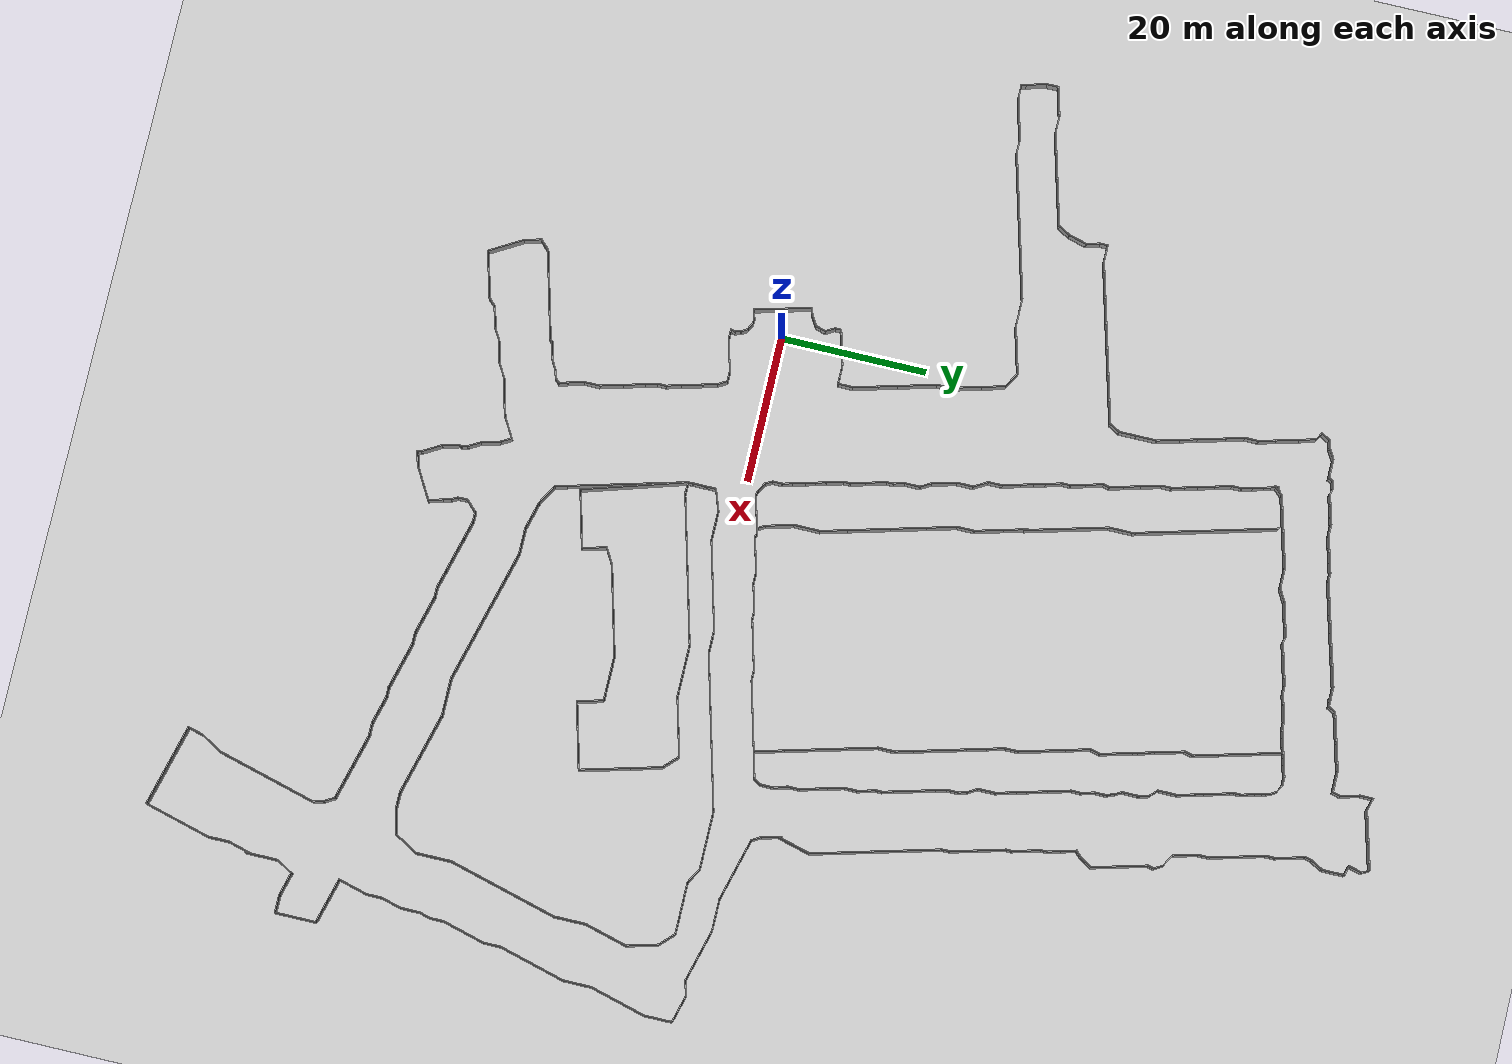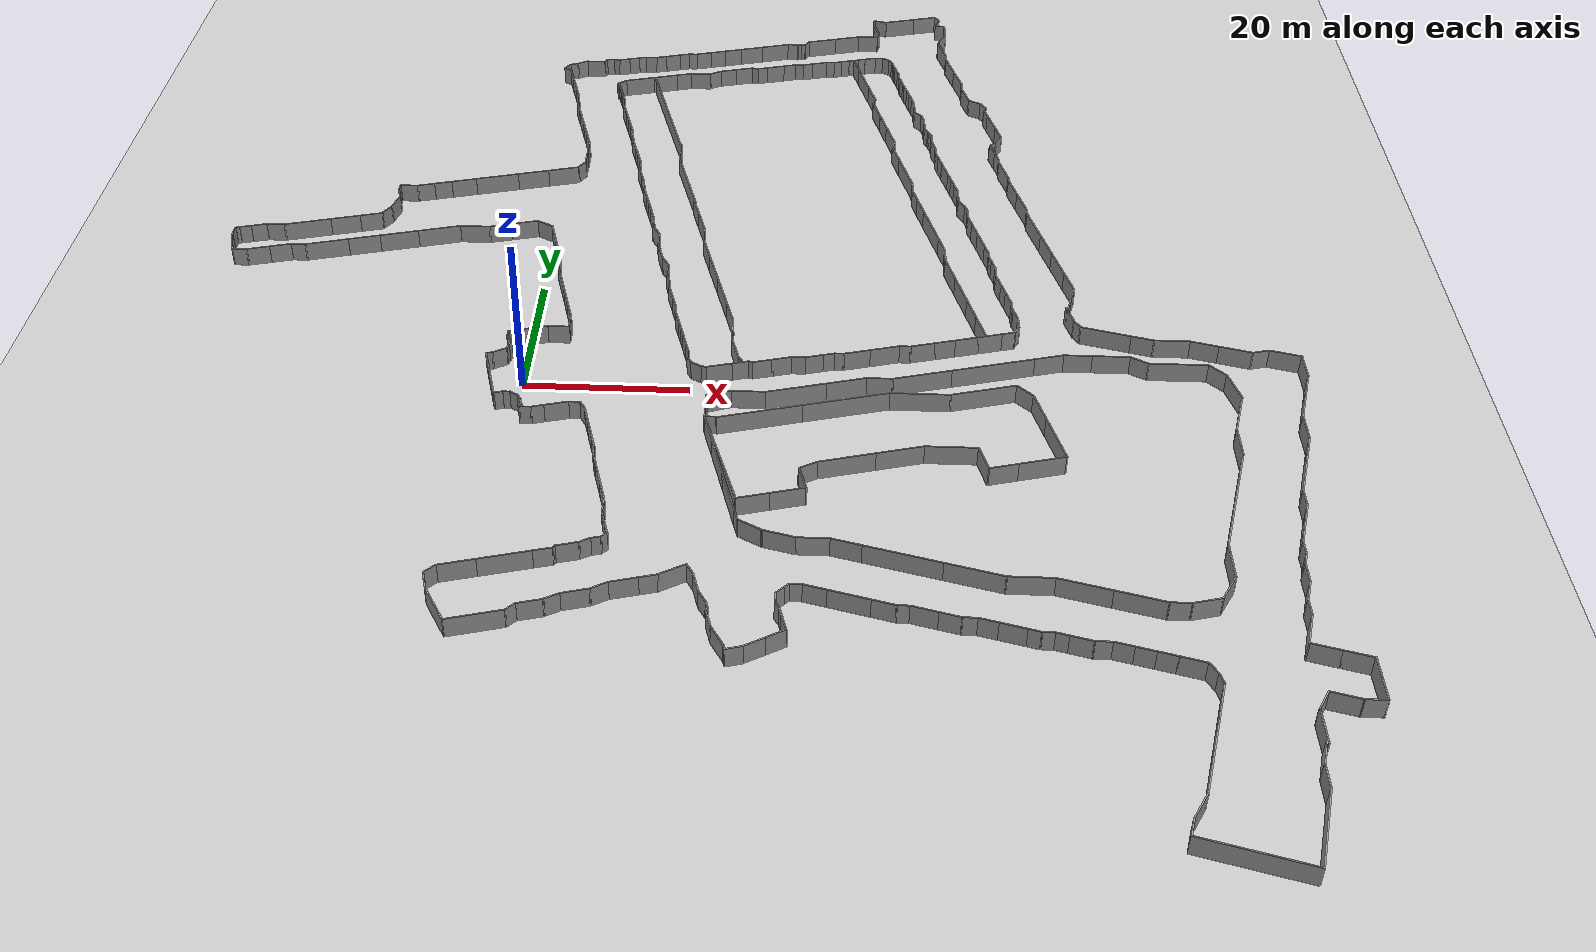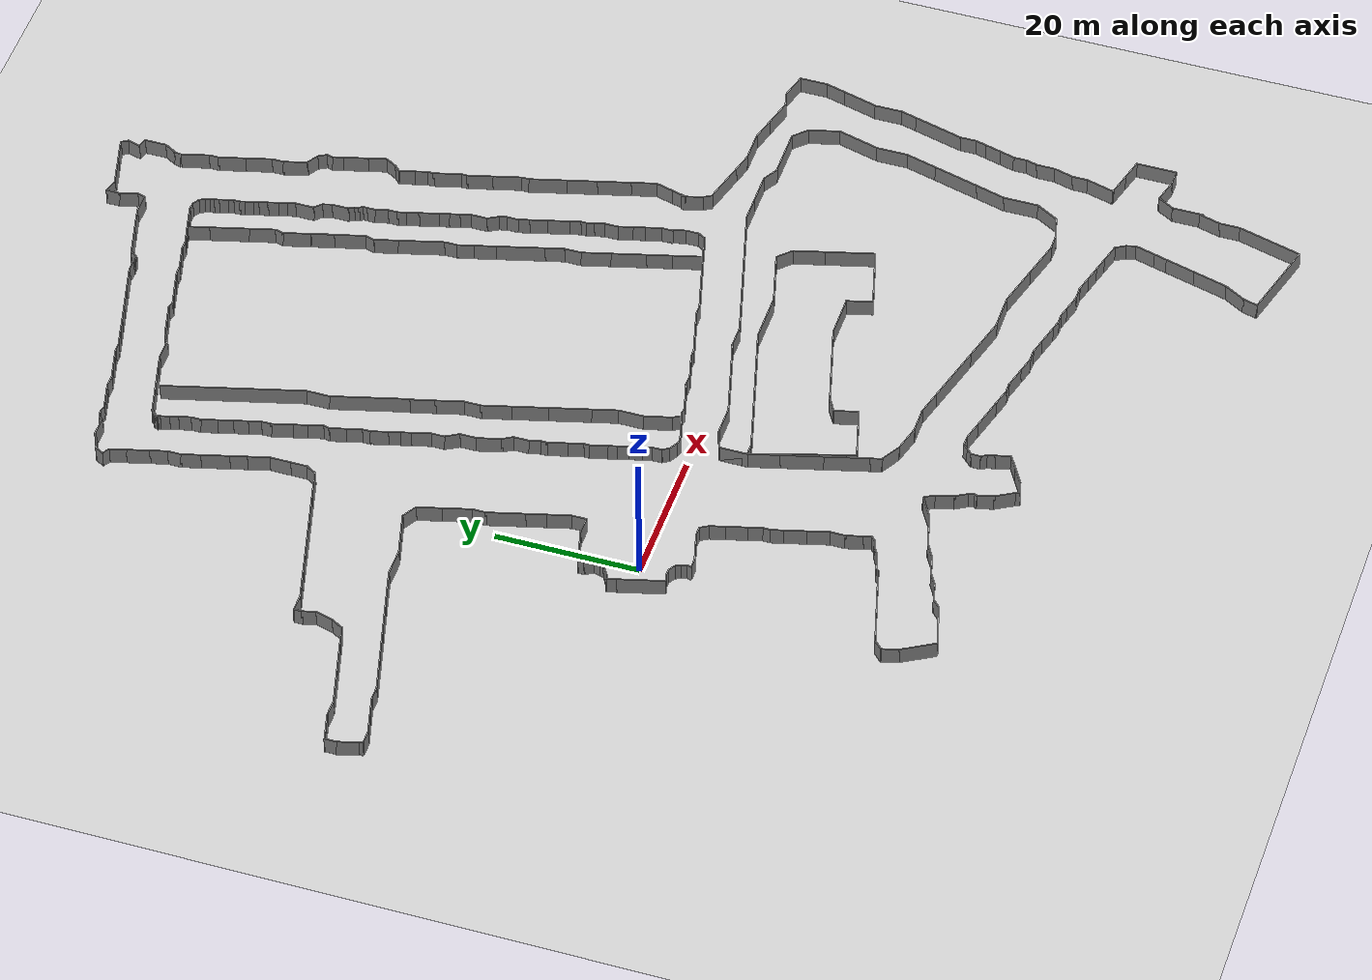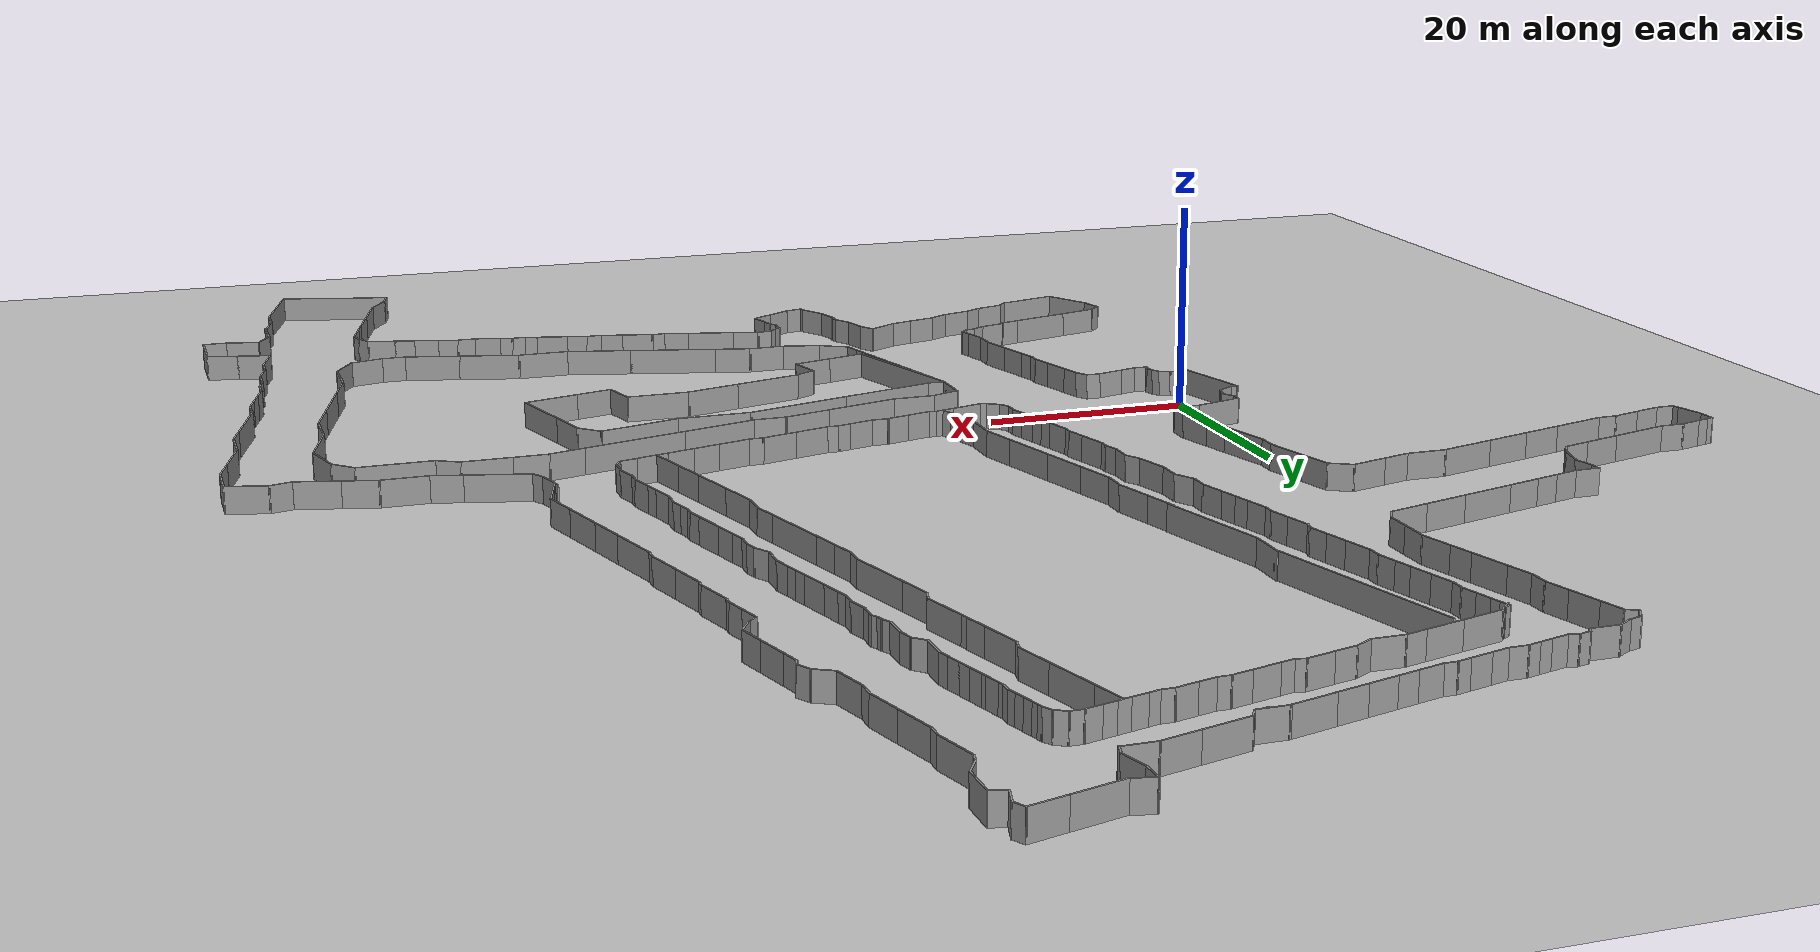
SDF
<sdf version="1.7">
 <world name="default">
  <light name="sun" type="directional">
   <pose>0 0 10 0 -0 0</pose>
   <diffuse>0.8 0.8 0.8 1</diffuse>
   <specular>0.2 0.2 0.2 1</specular>
   <attenuation>
    <range>1000</range>
    <constant>0.9</constant>
    <linear>0.01</linear>
    <quadratic>0.001</quadratic>
   </attenuation>
   <direction>-0.5 0.1 -0.9</direction>
   <spot><inner_angle>0</inner_angle><outer_angle>0</outer_angle><falloff>0</falloff></spot>
  </light>
  <model name="ground_plane">
   <static>1</static>
   <link name="link">
    <collision name="collision">
     <geometry><plane><normal>0 0 1</normal><size>500 500</size></plane></geometry>
     <surface><friction><ode><mu>100</mu><mu2>50</mu2></ode></friction></surface>
    </collision>
    <visual name="visual">
     <cast_shadows>0</cast_shadows>
     <geometry><plane><normal>0 0 1</normal><size>500 500</size></plane></geometry>
     <material>
      <script><uri>file://media/materials/scripts/gazebo.material</uri><name>Gazebo/Grey</name></script>
     </material>
    </visual>
   </link>
  </model>
  <gravity>0 0 -9.8</gravity>
  <magnetic_field>6e-06 2.3e-05 -4.2e-05</magnetic_field>
  <atmosphere type="adiabatic"/>
  <physics type="ode">
   <max_step_size>0.001</max_step_size>
   <real_time_factor>1</real_time_factor>
   <real_time_update_rate>1000</real_time_update_rate>
  </physics>
  <scene><ambient>0.4 0.4 0.4 1</ambient><background>0.7 0.7 0.7 1</background><shadows>1</shadows></scene>
  <audio><device>default</device></audio>
  <spherical_coordinates>
   <surface_model>EARTH_WGS84</surface_model>
   <latitude_deg>0</latitude_deg>
   <longitude_deg>0</longitude_deg>
   <elevation>0</elevation>
   <heading_deg>0</heading_deg>
  </spherical_coordinates>
  <model name="out_door1">
   <pose>25.5832 12.3476 0 0 -0 0</pose>
   <link name="Wall_10">
    <collision name="Wall_10_Collision">
     <geometry><box><size>1.75 0.15 2.5</size></box></geometry>
     <pose>0 0 1.25 0 -0 0</pose>
    </collision>
    <visual name="Wall_10_Visual">
     <pose>0 0 1.25 0 -0 0</pose>
     <geometry><box><size>1.75 0.15 2.5</size></box></geometry>
     <material>
      <script><uri>file://media/materials/scripts/gazebo.material</uri><name>Gazebo/Grey</name></script>
      <ambient>1 1 1 1</ambient>
     </material>
     <meta><layer>0</layer></meta>
    </visual>
    <pose>-22.8083 -18.9852 0 0 -0 0.261799</pose>
   </link>
   <link name="Wall_102">
    <collision name="Wall_102_Collision">
     <geometry><box><size>4.5 0.15 2.5</size></box></geometry>
     <pose>0 0 1.25 0 -0 0</pose>
    </collision>
    <visual name="Wall_102_Visual">
     <pose>0 0 1.25 0 -0 0</pose>
     <geometry><box><size>4.5 0.15 2.5</size></box></geometry>
     <material>
      <script><uri>file://media/materials/scripts/gazebo.material</uri><name>Gazebo/Grey</name></script>
      <ambient>1 1 1 1</ambient>
     </material>
     <meta><layer>0</layer></meta>
    </visual>
    <pose>58.6011 -63.758 0 0 -0 1.5708</pose>
   </link>
   <link name="Wall_103">
    <collision name="Wall_103_Collision">
     <geometry><box><size>2.75 0.15 2.5</size></box></geometry>
     <pose>0 0 1.25 0 -0 0</pose>
    </collision>
    <visual name="Wall_103_Visual">
     <pose>0 0 1.25 0 -0 0</pose>
     <geometry><box><size>2.75 0.15 2.5</size></box></geometry>
     <material>
      <script><uri>file://media/materials/scripts/gazebo.material</uri><name>Gazebo/Grey</name></script>
      <ambient>1 1 1 1</ambient>
     </material>
     <meta><layer>0</layer></meta>
    </visual>
    <pose>59.2511 -60.4572 0 0 -0 1.0472</pose>
   </link>
   <link name="Wall_104">
    <collision name="Wall_104_Collision">
     <geometry><box><size>3.5 0.15 2.5</size></box></geometry>
     <pose>0 0 1.25 0 -0 0</pose>
    </collision>
    <visual name="Wall_104_Visual">
     <pose>0 0 1.25 0 -0 0</pose>
     <geometry><box><size>3.5 0.15 2.5</size></box></geometry>
     <material>
      <script><uri>file://media/materials/scripts/gazebo.material</uri><name>Gazebo/Grey</name></script>
      <ambient>1 1 1 1</ambient>
     </material>
     <meta><layer>0</layer></meta>
    </visual>
    <pose>61.519 -59.7649 0 0 -0 -0.261799</pose>
   </link>
   <link name="Wall_105">
    <collision name="Wall_105_Collision">
     <geometry><box><size>2.5 0.15 2.5</size></box></geometry>
     <pose>0 0 1.25 0 -0 0</pose>
    </collision>
    <visual name="Wall_105_Visual">
     <pose>0 0 1.25 0 -0 0</pose>
     <geometry><box><size>2.5 0.15 2.5</size></box></geometry>
     <material>
      <script><uri>file://media/materials/scripts/gazebo.material</uri><name>Gazebo/Grey</name></script>
      <ambient>1 1 1 1</ambient>
     </material>
     <meta><layer>0</layer></meta>
    </visual>
    <pose>64.3119 -60.1984 0 0 -0 0</pose>
   </link>
   <link name="Wall_106">
    <collision name="Wall_106_Collision">
     <geometry><box><size>5.75 0.15 2.5</size></box></geometry>
     <pose>0 0 1.25 0 -0 0</pose>
    </collision>
    <visual name="Wall_106_Visual">
     <pose>0 0 1.25 0 -0 0</pose>
     <geometry><box><size>5.75 0.15 2.5</size></box></geometry>
     <material>
      <script><uri>file://media/materials/scripts/gazebo.material</uri><name>Gazebo/Grey</name></script>
      <ambient>1 1 1 1</ambient>
     </material>
     <meta><layer>0</layer></meta>
    </visual>
    <pose>65.4869 -57.3984 0 0 -0 1.5708</pose>
   </link>
   <link name="Wall_107">
    <collision name="Wall_107_Collision">
     <geometry><box><size>3.25 0.15 2.5</size></box></geometry>
     <pose>0 0 1.25 0 -0 0</pose>
    </collision>
    <visual name="Wall_107_Visual">
     <pose>0 0 1.25 0 -0 0</pose>
     <geometry><box><size>3.25 0.15 2.5</size></box></geometry>
     <material>
      <script><uri>file://media/materials/scripts/gazebo.material</uri><name>Gazebo/Grey</name></script>
      <ambient>1 1 1 1</ambient>
     </material>
     <meta><layer>0</layer></meta>
    </visual>
    <pose>63.9897 -54.1972 0 0 -0 2.87979</pose>
   </link>
   <link name="Wall_108">
    <collision name="Wall_108_Collision">
     <geometry><box><size>3.5 0.15 2.5</size></box></geometry>
     <pose>0 0 1.25 0 -0 0</pose>
    </collision>
    <visual name="Wall_108_Visual">
     <pose>0 0 1.25 0 -0 0</pose>
     <geometry><box><size>3.5 0.15 2.5</size></box></geometry>
     <material>
      <script><uri>file://media/materials/scripts/gazebo.material</uri><name>Gazebo/Grey</name></script>
      <ambient>1 1 1 1</ambient>
     </material>
     <meta><layer>0</layer></meta>
    </visual>
    <pose>60.8746 -53.3625 0 0 -0 2.87979</pose>
   </link>
   <link name="Wall_109">
    <collision name="Wall_109_Collision">
     <geometry><box><size>4.25 0.15 2.5</size></box></geometry>
     <pose>0 0 1.25 0 -0 0</pose>
    </collision>
    <visual name="Wall_109_Visual">
     <pose>0 0 1.25 0 -0 0</pose>
     <geometry><box><size>4.25 0.15 2.5</size></box></geometry>
     <material>
      <script><uri>file://media/materials/scripts/gazebo.material</uri><name>Gazebo/Grey</name></script>
      <ambient>1 1 1 1</ambient>
     </material>
     <meta><layer>0</layer></meta>
    </visual>
    <pose>59.7873 -50.9489 0 0 -0 1.309</pose>
   </link>
   <link name="Wall_11">
    <collision name="Wall_11_Collision">
     <geometry><box><size>3 0.15 2.5</size></box></geometry>
     <pose>0 0 1.25 0 -0 0</pose>
    </collision>
    <visual name="Wall_11_Visual">
     <pose>0 0 1.25 0 -0 0</pose>
     <geometry><box><size>3 0.15 2.5</size></box></geometry>
     <material>
      <script><uri>file://media/materials/scripts/gazebo.material</uri><name>Gazebo/Grey</name></script>
      <ambient>1 1 1 1</ambient>
     </material>
     <meta><layer>0</layer></meta>
    </visual>
    <pose>-20.6591 -18.4094 0 0 -0 0.261799</pose>
   </link>
   <link name="Wall_110">
    <collision name="Wall_110_Collision">
     <geometry><box><size>2.25 0.15 2.5</size></box></geometry>
     <pose>0 0 1.25 0 -0 0</pose>
    </collision>
    <visual name="Wall_110_Visual">
     <pose>0 0 1.25 0 -0 0</pose>
     <geometry><box><size>2.25 0.15 2.5</size></box></geometry>
     <material>
      <script><uri>file://media/materials/scripts/gazebo.material</uri><name>Gazebo/Grey</name></script>
      <ambient>1 1 1 1</ambient>
     </material>
     <meta><layer>0</layer></meta>
    </visual>
    <pose>60.3178 -47.9187 0 0 -0 1.5708</pose>
   </link>
   <link name="Wall_112">
    <collision name="Wall_112_Collision">
     <geometry><box><size>3 0.15 2.5</size></box></geometry>
     <pose>0 0 1.25 0 -0 0</pose>
    </collision>
    <visual name="Wall_112_Visual">
     <pose>0 0 1.25 0 -0 0</pose>
     <geometry><box><size>3 0.15 2.5</size></box></geometry>
     <material>
      <script><uri>file://media/materials/scripts/gazebo.material</uri><name>Gazebo/Grey</name></script>
      <ambient>1 1 1 1</ambient>
     </material>
     <meta><layer>0</layer></meta>
    </visual>
    <pose>60.6867 -45.4923 0 0 -0 1.309</pose>
   </link>
   <link name="Wall_113">
    <collision name="Wall_113_Collision">
     <geometry><box><size>2.75 0.15 2.5</size></box></geometry>
     <pose>0 0 1.25 0 -0 0</pose>
    </collision>
    <visual name="Wall_113_Visual">
     <pose>0 0 1.25 0 -0 0</pose>
     <geometry><box><size>2.75 0.15 2.5</size></box></geometry>
     <material>
      <script><uri>file://media/materials/scripts/gazebo.material</uri><name>Gazebo/Grey</name></script>
      <ambient>1 1 1 1</ambient>
     </material>
     <meta><layer>0</layer></meta>
    </visual>
    <pose>61.0555 -42.8158 0 0 -0 1.5708</pose>
   </link>
   <link name="Wall_114">
    <collision name="Wall_114_Collision">
     <geometry><box><size>1.75 0.15 2.5</size></box></geometry>
     <pose>0 0 1.25 0 -0 0</pose>
    </collision>
    <visual name="Wall_114_Visual">
     <pose>0 0 1.25 0 -0 0</pose>
     <geometry><box><size>1.75 0.15 2.5</size></box></geometry>
     <material>
      <script><uri>file://media/materials/scripts/gazebo.material</uri><name>Gazebo/Grey</name></script>
      <ambient>1 1 1 1</ambient>
     </material>
     <meta><layer>0</layer></meta>
    </visual>
    <pose>61.2625 -40.7431 0 0 -0 1.309</pose>
   </link>
   <link name="Wall_115">
    <collision name="Wall_115_Collision">
     <geometry><box><size>2 0.15 2.5</size></box></geometry>
     <pose>0 0 1.25 0 -0 0</pose>
    </collision>
    <visual name="Wall_115_Visual">
     <pose>0 0 1.25 0 -0 0</pose>
     <geometry><box><size>2 0.15 2.5</size></box></geometry>
     <material>
      <script><uri>file://media/materials/scripts/gazebo.material</uri><name>Gazebo/Grey</name></script>
      <ambient>1 1 1 1</ambient>
     </material>
     <meta><layer>0</layer></meta>
    </visual>
    <pose>61.4696 -39.0454 0 0 -0 1.5708</pose>
   </link>
   <link name="Wall_116">
    <collision name="Wall_116_Collision">
     <geometry><box><size>2.25 0.15 2.5</size></box></geometry>
     <pose>0 0 1.25 0 -0 0</pose>
    </collision>
    <visual name="Wall_116_Visual">
     <pose>0 0 1.25 0 -0 0</pose>
     <geometry><box><size>2.25 0.15 2.5</size></box></geometry>
     <material>
      <script><uri>file://media/materials/scripts/gazebo.material</uri><name>Gazebo/Grey</name></script>
      <ambient>1 1 1 1</ambient>
     </material>
     <meta><layer>0</layer></meta>
    </visual>
    <pose>61.7413 -37.1061 0 0 -0 1.309</pose>
   </link>
   <link name="Wall_117">
    <collision name="Wall_117_Collision">
     <geometry><box><size>2.5 0.15 2.5</size></box></geometry>
     <pose>0 0 1.25 0 -0 0</pose>
    </collision>
    <visual name="Wall_117_Visual">
     <pose>0 0 1.25 0 -0 0</pose>
     <geometry><box><size>2.5 0.15 2.5</size></box></geometry>
     <material>
      <script><uri>file://media/materials/scripts/gazebo.material</uri><name>Gazebo/Grey</name></script>
      <ambient>1 1 1 1</ambient>
     </material>
     <meta><layer>0</layer></meta>
    </visual>
    <pose>62.3172 -34.9569 0 0 -0 1.309</pose>
   </link>
   <link name="Wall_118">
    <collision name="Wall_118_Collision">
     <geometry><box><size>1.75 0.15 2.5</size></box></geometry>
     <pose>0 0 1.25 0 -0 0</pose>
    </collision>
    <visual name="Wall_118_Visual">
     <pose>0 0 1.25 0 -0 0</pose>
     <geometry><box><size>1.75 0.15 2.5</size></box></geometry>
     <material>
      <script><uri>file://media/materials/scripts/gazebo.material</uri><name>Gazebo/Grey</name></script>
      <ambient>1 1 1 1</ambient>
     </material>
     <meta><layer>0</layer></meta>
    </visual>
    <pose>62.8284 -33.0492 0 0 -0 1.309</pose>
   </link>
   <link name="Wall_119">
    <collision name="Wall_119_Collision">
     <geometry><box><size>2.5 0.15 2.5</size></box></geometry>
     <pose>0 0 1.25 0 -0 0</pose>
    </collision>
    <visual name="Wall_119_Visual">
     <pose>0 0 1.25 0 -0 0</pose>
     <geometry><box><size>2.5 0.15 2.5</size></box></geometry>
     <material>
      <script><uri>file://media/materials/scripts/gazebo.material</uri><name>Gazebo/Grey</name></script>
      <ambient>1 1 1 1</ambient>
     </material>
     <meta><layer>0</layer></meta>
    </visual>
    <pose>63.0354 -31.1015 0 0 -0 1.5708</pose>
   </link>
   <link name="Wall_12">
    <collision name="Wall_12_Collision">
     <geometry><box><size>1.5 0.15 2.5</size></box></geometry>
     <pose>0 0 1.25 0 -0 0</pose>
    </collision>
    <visual name="Wall_12_Visual">
     <pose>0 0 1.25 0 -0 0</pose>
     <geometry><box><size>1.5 0.15 2.5</size></box></geometry>
     <material>
      <script><uri>file://media/materials/scripts/gazebo.material</uri><name>Gazebo/Grey</name></script>
      <ambient>1 1 1 1</ambient>
     </material>
     <meta><layer>0</layer></meta>
    </visual>
    <pose>-18.6076 -18.0405 0 0 -0 0</pose>
   </link>
   <link name="Wall_123">
    <collision name="Wall_123_Collision">
     <geometry><box><size>7.25 0.15 2.5</size></box></geometry>
     <pose>0 0 1.25 0 -0 0</pose>
    </collision>
    <visual name="Wall_123_Visual">
     <pose>0 0 1.25 0 -0 0</pose>
     <geometry><box><size>7.25 0.15 2.5</size></box></geometry>
     <material>
      <script><uri>file://media/materials/scripts/gazebo.material</uri><name>Gazebo/Grey</name></script>
      <ambient>1 1 1 1</ambient>
     </material>
     <meta><layer>0</layer></meta>
    </visual>
    <pose>63.9542 -26.4975 0 0 -0 1.309</pose>
   </link>
   <link name="Wall_124">
    <collision name="Wall_124_Collision">
     <geometry><box><size>2.5 0.15 2.5</size></box></geometry>
     <pose>0 0 1.25 0 -0 0</pose>
    </collision>
    <visual name="Wall_124_Visual">
     <pose>0 0 1.25 0 -0 0</pose>
     <geometry><box><size>2.5 0.15 2.5</size></box></geometry>
     <material>
      <script><uri>file://media/materials/scripts/gazebo.material</uri><name>Gazebo/Grey</name></script>
      <ambient>1 1 1 1</ambient>
     </material>
     <meta><layer>0</layer></meta>
    </visual>
    <pose>65.1772 -21.9335 0 0 -0 1.309</pose>
   </link>
   <link name="Wall_125">
    <collision name="Wall_125_Collision">
     <geometry><box><size>4 0.15 2.5</size></box></geometry>
     <pose>0 0 1.25 0 -0 0</pose>
    </collision>
    <visual name="Wall_125_Visual">
     <pose>0 0 1.25 0 -0 0</pose>
     <geometry><box><size>4 0.15 2.5</size></box></geometry>
     <material>
      <script><uri>file://media/materials/scripts/gazebo.material</uri><name>Gazebo/Grey</name></script>
      <ambient>1 1 1 1</ambient>
     </material>
     <meta><layer>0</layer></meta>
    </visual>
    <pose>65.4813 -18.8735 0 0 -0 1.5708</pose>
   </link>
   <link name="Wall_126">
    <collision name="Wall_126_Collision">
     <geometry><box><size>5.25 0.15 2.5</size></box></geometry>
     <pose>0 0 1.25 0 -0 0</pose>
    </collision>
    <visual name="Wall_126_Visual">
     <pose>0 0 1.25 0 -0 0</pose>
     <geometry><box><size>5.25 0.15 2.5</size></box></geometry>
     <material>
      <script><uri>file://media/materials/scripts/gazebo.material</uri><name>Gazebo/Grey</name></script>
      <ambient>1 1 1 1</ambient>
     </material>
     <meta><layer>0</layer></meta>
    </visual>
    <pose>66.1413 -14.4854 0 0 -0 1.309</pose>
   </link>
   <link name="Wall_127">
    <collision name="Wall_127_Collision">
     <geometry><box><size>3 0.15 2.5</size></box></geometry>
     <pose>0 0 1.25 0 -0 0</pose>
    </collision>
    <visual name="Wall_127_Visual">
     <pose>0 0 1.25 0 -0 0</pose>
     <geometry><box><size>3 0.15 2.5</size></box></geometry>
     <material>
      <script><uri>file://media/materials/scripts/gazebo.material</uri><name>Gazebo/Grey</name></script>
      <ambient>1 1 1 1</ambient>
     </material>
     <meta><layer>0</layer></meta>
    </visual>
    <pose>67.1701 -10.6458 0 0 -0 1.309</pose>
   </link>
   <link name="Wall_128">
    <collision name="Wall_128_Collision">
     <geometry><box><size>4 0.15 2.5</size></box></geometry>
     <pose>0 0 1.25 0 -0 0</pose>
    </collision>
    <visual name="Wall_128_Visual">
     <pose>0 0 1.25 0 -0 0</pose>
     <geometry><box><size>4 0.15 2.5</size></box></geometry>
     <material>
      <script><uri>file://media/materials/scripts/gazebo.material</uri><name>Gazebo/Grey</name></script>
      <ambient>1 1 1 1</ambient>
     </material>
     <meta><layer>0</layer></meta>
    </visual>
    <pose>67.5389 -7.34439 0 0 -0 1.5708</pose>
   </link>
   <link name="Wall_129">
    <collision name="Wall_129_Collision">
     <geometry><box><size>4 0.15 2.5</size></box></geometry>
     <pose>0 0 1.25 0 -0 0</pose>
    </collision>
    <visual name="Wall_129_Visual">
     <pose>0 0 1.25 0 -0 0</pose>
     <geometry><box><size>4 0.15 2.5</size></box></geometry>
     <material>
      <script><uri>file://media/materials/scripts/gazebo.material</uri><name>Gazebo/Grey</name></script>
      <ambient>1 1 1 1</ambient>
     </material>
     <meta><layer>0</layer></meta>
    </visual>
    <pose>65.6795 -4.92117 0 0 -0 2.87979</pose>
   </link>
   <link name="Wall_130">
    <collision name="Wall_130_Collision">
     <geometry><box><size>2.25 0.15 2.5</size></box></geometry>
     <pose>0 0 1.25 0 -0 0</pose>
    </collision>
    <visual name="Wall_130_Visual">
     <pose>0 0 1.25 0 -0 0</pose>
     <geometry><box><size>2.25 0.15 2.5</size></box></geometry>
     <material>
      <script><uri>file://media/materials/scripts/gazebo.material</uri><name>Gazebo/Grey</name></script>
      <ambient>1 1 1 1</ambient>
     </material>
     <meta><layer>0</layer></meta>
    </visual>
    <pose>62.8059 -4.6947 0 0 -0 -2.87979</pose>
   </link>
   <link name="Wall_131">
    <collision name="Wall_131_Collision">
     <geometry><box><size>4.25 0.15 2.5</size></box></geometry>
     <pose>0 0 1.25 0 -0 0</pose>
    </collision>
    <visual name="Wall_131_Visual">
     <pose>0 0 1.25 0 -0 0</pose>
     <geometry><box><size>4.25 0.15 2.5</size></box></geometry>
     <material>
      <script><uri>file://media/materials/scripts/gazebo.material</uri><name>Gazebo/Grey</name></script>
      <ambient>1 1 1 1</ambient>
     </material>
     <meta><layer>0</layer></meta>
    </visual>
    <pose>59.8115 -4.43588 0 0 -0 2.87979</pose>
   </link>
   <link name="Wall_132">
    <collision name="Wall_132_Collision">
     <geometry><box><size>3.5 0.15 2.5</size></box></geometry>
     <pose>0 0 1.25 0 -0 0</pose>
    </collision>
    <visual name="Wall_132_Visual">
     <pose>0 0 1.25 0 -0 0</pose>
     <geometry><box><size>3.5 0.15 2.5</size></box></geometry>
     <material>
      <script><uri>file://media/materials/scripts/gazebo.material</uri><name>Gazebo/Grey</name></script>
      <ambient>1 1 1 1</ambient>
     </material>
     <meta><layer>0</layer></meta>
    </visual>
    <pose>56.2134 -3.47178 0 0 -0 2.87979</pose>
   </link>
   <link name="Wall_133">
    <collision name="Wall_133_Collision">
     <geometry><box><size>4.5 0.15 2.5</size></box></geometry>
     <pose>0 0 1.25 0 -0 0</pose>
    </collision>
    <visual name="Wall_133_Visual">
     <pose>0 0 1.25 0 -0 0</pose>
     <geometry><box><size>4.5 0.15 2.5</size></box></geometry>
     <material>
      <script><uri>file://media/materials/scripts/gazebo.material</uri><name>Gazebo/Grey</name></script>
      <ambient>1 1 1 1</ambient>
     </material>
     <meta><layer>0</layer></meta>
    </visual>
    <pose>52.4205 -3.03826 0 0 -0 3.14159</pose>
   </link>
   <link name="Wall_134">
    <collision name="Wall_134_Collision">
     <geometry><box><size>3 0.15 2.5</size></box></geometry>
     <pose>0 0 1.25 0 -0 0</pose>
    </collision>
    <visual name="Wall_134_Visual">
     <pose>0 0 1.25 0 -0 0</pose>
     <geometry><box><size>3 0.15 2.5</size></box></geometry>
     <material>
      <script><uri>file://media/materials/scripts/gazebo.material</uri><name>Gazebo/Grey</name></script>
      <ambient>1 1 1 1</ambient>
     </material>
     <meta><layer>0</layer></meta>
    </visual>
    <pose>48.869 -2.66944 0 0 -0 2.87979</pose>
   </link>
   <link name="Wall_135">
    <collision name="Wall_135_Collision">
     <geometry><box><size>6.25 0.15 2.5</size></box></geometry>
     <pose>0 0 1.25 0 -0 0</pose>
    </collision>
    <visual name="Wall_135_Visual">
     <pose>0 0 1.25 0 -0 0</pose>
     <geometry><box><size>6.25 0.15 2.5</size></box></geometry>
     <material>
      <script><uri>file://media/materials/scripts/gazebo.material</uri><name>Gazebo/Grey</name></script>
      <ambient>1 1 1 1</ambient>
     </material>
     <meta><layer>0</layer></meta>
    </visual>
    <pose>44.5465 -1.51123 0 0 -0 2.87979</pose>
   </link>
   <link name="Wall_136">
    <collision name="Wall_136_Collision">
     <geometry><box><size>1.5 0.15 2.5</size></box></geometry>
     <pose>0 0 1.25 0 -0 0</pose>
    </collision>
    <visual name="Wall_136_Visual">
     <pose>0 0 1.25 0 -0 0</pose>
     <geometry><box><size>1.5 0.15 2.5</size></box></geometry>
     <material>
      <script><uri>file://media/materials/scripts/gazebo.material</uri><name>Gazebo/Grey</name></script>
      <ambient>1 1 1 1</ambient>
     </material>
     <meta><layer>0</layer></meta>
    </visual>
    <pose>41.2629 -0.137262 0 0 -0 2.0944</pose>
   </link>
   <link name="Wall_137">
    <collision name="Wall_137_Collision">
     <geometry><box><size>3 0.15 2.5</size></box></geometry>
     <pose>0 0 1.25 0 -0 0</pose>
    </collision>
    <visual name="Wall_137_Visual">
     <pose>0 0 1.25 0 -0 0</pose>
     <geometry><box><size>3 0.15 2.5</size></box></geometry>
     <material>
      <script><uri>file://media/materials/scripts/gazebo.material</uri><name>Gazebo/Grey</name></script>
      <ambient>1 1 1 1</ambient>
     </material>
     <meta><layer>0</layer></meta>
    </visual>
    <pose>40.5566 1.82375 0 0 -0 1.8326</pose>
   </link>
   <link name="Wall_139">
    <collision name="Wall_139_Collision">
     <geometry><box><size>2.25 0.15 2.5</size></box></geometry>
     <pose>0 0 1.25 0 -0 0</pose>
    </collision>
    <visual name="Wall_139_Visual">
     <pose>0 0 1.25 0 -0 0</pose>
     <geometry><box><size>2.25 0.15 2.5</size></box></geometry>
     <material>
      <script><uri>file://media/materials/scripts/gazebo.material</uri><name>Gazebo/Grey</name></script>
      <ambient>1 1 1 1</ambient>
     </material>
     <meta><layer>0</layer></meta>
    </visual>
    <pose>40.599 3.69792 0 0 -0 1.309</pose>
   </link>
   <link name="Wall_14">
    <collision name="Wall_14_Collision">
     <geometry><box><size>1.5 0.15 2.5</size></box></geometry>
     <pose>0 0 1.25 0 -0 0</pose>
    </collision>
    <visual name="Wall_14_Visual">
     <pose>0 0 1.25 0 -0 0</pose>
     <geometry><box><size>1.5 0.15 2.5</size></box></geometry>
     <material>
      <script><uri>file://media/materials/scripts/gazebo.material</uri><name>Gazebo/Grey</name></script>
      <ambient>1 1 1 1</ambient>
     </material>
     <meta><layer>0</layer></meta>
    </visual>
    <pose>-17.5951 -18.6251 0 0 -0 -1.0472</pose>
   </link>
   <link name="Wall_140">
    <collision name="Wall_140_Collision">
     <geometry><box><size>2.75 0.15 2.5</size></box></geometry>
     <pose>0 0 1.25 0 -0 0</pose>
    </collision>
    <visual name="Wall_140_Visual">
     <pose>0 0 1.25 0 -0 0</pose>
     <geometry><box><size>2.75 0.15 2.5</size></box></geometry>
     <material>
      <script><uri>file://media/materials/scripts/gazebo.material</uri><name>Gazebo/Grey</name></script>
      <ambient>1 1 1 1</ambient>
     </material>
     <meta><layer>0</layer></meta>
    </visual>
    <pose>41.2073 5.96784 0 0 -0 1.309</pose>
   </link>
   <link name="Wall_141">
    <collision name="Wall_141_Collision">
     <geometry><box><size>3.75 0.15 2.5</size></box></geometry>
     <pose>0 0 1.25 0 -0 0</pose>
    </collision>
    <visual name="Wall_141_Visual">
     <pose>0 0 1.25 0 -0 0</pose>
     <geometry><box><size>3.75 0.15 2.5</size></box></geometry>
     <material>
      <script><uri>file://media/materials/scripts/gazebo.material</uri><name>Gazebo/Grey</name></script>
      <ambient>1 1 1 1</ambient>
     </material>
     <meta><layer>0</layer></meta>
    </visual>
    <pose>41.0779 8.96221 0 0 -0 1.8326</pose>
   </link>
   <link name="Wall_142">
    <collision name="Wall_142_Collision">
     <geometry><box><size>4.75 0.15 2.5</size></box></geometry>
     <pose>0 0 1.25 0 -0 0</pose>
    </collision>
    <visual name="Wall_142_Visual">
     <pose>0 0 1.25 0 -0 0</pose>
     <geometry><box><size>4.75 0.15 2.5</size></box></geometry>
     <material>
      <script><uri>file://media/materials/scripts/gazebo.material</uri><name>Gazebo/Grey</name></script>
      <ambient>1 1 1 1</ambient>
     </material>
     <meta><layer>0</layer></meta>
    </visual>
    <pose>40.0167 12.9225 0 0 -0 1.8326</pose>
   </link>
   <link name="Wall_143">
    <collision name="Wall_143_Collision">
     <geometry><box><size>4.25 0.15 2.5</size></box></geometry>
     <pose>0 0 1.25 0 -0 0</pose>
    </collision>
    <visual name="Wall_143_Visual">
     <pose>0 0 1.25 0 -0 0</pose>
     <geometry><box><size>4.25 0.15 2.5</size></box></geometry>
     <material>
      <script><uri>file://media/materials/scripts/gazebo.material</uri><name>Gazebo/Grey</name></script>
      <ambient>1 1 1 1</ambient>
     </material>
     <meta><layer>0</layer></meta>
    </visual>
    <pose>38.8908 17.1243 0 0 -0 1.8326</pose>
   </link>
   <link name="Wall_145">
    <collision name="Wall_145_Collision">
     <geometry><box><size>5.5 0.15 2.5</size></box></geometry>
     <pose>0 0 1.25 0 -0 0</pose>
    </collision>
    <visual name="Wall_145_Visual">
     <pose>0 0 1.25 0 -0 0</pose>
     <geometry><box><size>5.5 0.15 2.5</size></box></geometry>
     <material>
      <script><uri>file://media/materials/scripts/gazebo.material</uri><name>Gazebo/Grey</name></script>
      <ambient>1 1 1 1</ambient>
     </material>
     <meta><layer>0</layer></meta>
    </visual>
    <pose>37.6679 21.6883 0 0 -0 1.8326</pose>
   </link>
   <link name="Wall_146">
    <collision name="Wall_146_Collision">
     <geometry><box><size>1.25 0.15 2.5</size></box></geometry>
     <pose>0 0 1.25 0 -0 0</pose>
    </collision>
    <visual name="Wall_146_Visual">
     <pose>0 0 1.25 0 -0 0</pose>
     <geometry><box><size>1.25 0.15 2.5</size></box></geometry>
     <material>
      <script><uri>file://media/materials/scripts/gazebo.material</uri><name>Gazebo/Grey</name></script>
      <ambient>1 1 1 1</ambient>
     </material>
     <meta><layer>0</layer></meta>
    </visual>
    <pose>36.9756 24.8221 0 0 -0 1.5708</pose>
   </link>
   <link name="Wall_147">
    <collision name="Wall_147_Collision">
     <geometry><box><size>4 0.15 2.5</size></box></geometry>
     <pose>0 0 1.25 0 -0 0</pose>
    </collision>
    <visual name="Wall_147_Visual">
     <pose>0 0 1.25 0 -0 0</pose>
     <geometry><box><size>4 0.15 2.5</size></box></geometry>
     <material>
      <script><uri>file://media/materials/scripts/gazebo.material</uri><name>Gazebo/Grey</name></script>
      <ambient>1 1 1 1</ambient>
     </material>
     <meta><layer>0</layer></meta>
    </visual>
    <pose>36.4773 27.2315 0 0 -0 1.8326</pose>
   </link>
   <link name="Wall_148">
    <collision name="Wall_148_Collision">
     <geometry><box><size>3.75 0.15 2.5</size></box></geometry>
     <pose>0 0 1.25 0 -0 0</pose>
    </collision>
    <visual name="Wall_148_Visual">
     <pose>0 0 1.25 0 -0 0</pose>
     <geometry><box><size>3.75 0.15 2.5</size></box></geometry>
     <material>
      <script><uri>file://media/materials/scripts/gazebo.material</uri><name>Gazebo/Grey</name></script>
      <ambient>1 1 1 1</ambient>
     </material>
     <meta><layer>0</layer></meta>
    </visual>
    <pose>35.5132 30.8296 0 0 -0 1.8326</pose>
   </link>
   <link name="Wall_149">
    <collision name="Wall_149_Collision">
     <geometry><box><size>1 0.15 2.5</size></box></geometry>
     <pose>0 0 1.25 0 -0 0</pose>
    </collision>
    <visual name="Wall_149_Visual">
     <pose>0 0 1.25 0 -0 0</pose>
     <geometry><box><size>1 0.15 2.5</size></box></geometry>
     <material>
      <script><uri>file://media/materials/scripts/gazebo.material</uri><name>Gazebo/Grey</name></script>
      <ambient>1 1 1 1</ambient>
     </material>
     <meta><layer>0</layer></meta>
    </visual>
    <pose>35.0474 32.9933 0 0 -0 1.5708</pose>
   </link>
   <link name="Wall_15">
    <collision name="Wall_15_Collision">
     <geometry><box><size>2.25 0.15 2.5</size></box></geometry>
     <pose>0 0 1.25 0 -0 0</pose>
    </collision>
    <visual name="Wall_15_Visual">
     <pose>0 0 1.25 0 -0 0</pose>
     <geometry><box><size>2.25 0.15 2.5</size></box></geometry>
     <material>
      <script><uri>file://media/materials/scripts/gazebo.material</uri><name>Gazebo/Grey</name></script>
      <ambient>1 1 1 1</ambient>
     </material>
     <meta><layer>0</layer></meta>
    </visual>
    <pose>-16.9859 -20.2239 0 0 -0 -1.309</pose>
   </link>
   <link name="Wall_150">
    <collision name="Wall_150_Collision">
     <geometry><box><size>4 0.15 2.5</size></box></geometry>
     <pose>0 0 1.25 0 -0 0</pose>
    </collision>
    <visual name="Wall_150_Visual">
     <pose>0 0 1.25 0 -0 0</pose>
     <geometry><box><size>4 0.15 2.5</size></box></geometry>
     <material>
      <script><uri>file://media/materials/scripts/gazebo.material</uri><name>Gazebo/Grey</name></script>
      <ambient>1 1 1 1</ambient>
     </material>
     <meta><layer>0</layer></meta>
    </visual>
    <pose>34.5491 35.2777 0 0 -0 1.8326</pose>
   </link>
   <link name="Wall_152">
    <collision name="Wall_152_Collision">
     <geometry><box><size>1 0.15 2.5</size></box></geometry>
     <pose>0 0 1.25 0 -0 0</pose>
    </collision>
    <visual name="Wall_152_Visual">
     <pose>0 0 1.25 0 -0 0</pose>
     <geometry><box><size>1 0.15 2.5</size></box></geometry>
     <material>
      <script><uri>file://media/materials/scripts/gazebo.material</uri><name>Gazebo/Grey</name></script>
      <ambient>1 1 1 1</ambient>
     </material>
     <meta><layer>0</layer></meta>
    </visual>
    <pose>34.0509 37.5621 0 0 -0 1.5708</pose>
   </link>
   <link name="Wall_153">
    <collision name="Wall_153_Collision">
     <geometry><box><size>2 0.15 2.5</size></box></geometry>
     <pose>0 0 1.25 0 -0 0</pose>
    </collision>
    <visual name="Wall_153_Visual">
     <pose>0 0 1.25 0 -0 0</pose>
     <geometry><box><size>2 0.15 2.5</size></box></geometry>
     <material>
      <script><uri>file://media/materials/scripts/gazebo.material</uri><name>Gazebo/Grey</name></script>
      <ambient>1 1 1 1</ambient>
     </material>
     <meta><layer>0</layer></meta>
    </visual>
    <pose>33.8115 38.8806 0 0 -0 1.8326</pose>
   </link>
   <link name="Wall_154">
    <collision name="Wall_154_Collision">
     <geometry><box><size>2.25 0.15 2.5</size></box></geometry>
     <pose>0 0 1.25 0 -0 0</pose>
    </collision>
    <visual name="Wall_154_Visual">
     <pose>0 0 1.25 0 -0 0</pose>
     <geometry><box><size>2.25 0.15 2.5</size></box></geometry>
     <material>
      <script><uri>file://media/materials/scripts/gazebo.material</uri><name>Gazebo/Grey</name></script>
      <ambient>1 1 1 1</ambient>
     </material>
     <meta><layer>0</layer></meta>
    </visual>
    <pose>33.3003 40.7883 0 0 -0 1.8326</pose>
   </link>
   <link name="Wall_155">
    <collision name="Wall_155_Collision">
     <geometry><box><size>1.25 0.15 2.5</size></box></geometry>
     <pose>0 0 1.25 0 -0 0</pose>
    </collision>
    <visual name="Wall_155_Visual">
     <pose>0 0 1.25 0 -0 0</pose>
     <geometry><box><size>1.25 0.15 2.5</size></box></geometry>
     <material>
      <script><uri>file://media/materials/scripts/gazebo.material</uri><name>Gazebo/Grey</name></script>
      <ambient>1 1 1 1</ambient>
     </material>
     <meta><layer>0</layer></meta>
    </visual>
    <pose>33.4175 42.1914 0 0 -0 0.785398</pose>
   </link>
   <link name="Wall_156">
    <collision name="Wall_156_Collision">
     <geometry><box><size>2 0.15 2.5</size></box></geometry>
     <pose>0 0 1.25 0 -0 0</pose>
    </collision>
    <visual name="Wall_156_Visual">
     <pose>0 0 1.25 0 -0 0</pose>
     <geometry><box><size>2 0.15 2.5</size></box></geometry>
     <material>
      <script><uri>file://media/materials/scripts/gazebo.material</uri><name>Gazebo/Grey</name></script>
      <ambient>1 1 1 1</ambient>
     </material>
     <meta><layer>0</layer></meta>
    </visual>
    <pose>34.2689 43.3814 0 0 -0 1.0472</pose>
   </link>
   <link name="Wall_157">
    <collision name="Wall_157_Collision">
     <geometry><box><size>2.75 0.15 2.5</size></box></geometry>
     <pose>0 0 1.25 0 -0 0</pose>
    </collision>
    <visual name="Wall_157_Visual">
     <pose>0 0 1.25 0 -0 0</pose>
     <geometry><box><size>2.75 0.15 2.5</size></box></geometry>
     <material>
      <script><uri>file://media/materials/scripts/gazebo.material</uri><name>Gazebo/Grey</name></script>
      <ambient>1 1 1 1</ambient>
     </material>
     <meta><layer>0</layer></meta>
    </visual>
    <pose>34.3949 45.4382 0 0 -0 1.8326</pose>
   </link>
   <link name="Wall_158">
    <collision name="Wall_158_Collision">
     <geometry><box><size>3.5 0.15 2.5</size></box></geometry>
     <pose>0 0 1.25 0 -0 0</pose>
    </collision>
    <visual name="Wall_158_Visual">
     <pose>0 0 1.25 0 -0 0</pose>
     <geometry><box><size>3.5 0.15 2.5</size></box></geometry>
     <material>
      <script><uri>file://media/materials/scripts/gazebo.material</uri><name>Gazebo/Grey</name></script>
      <ambient>1 1 1 1</ambient>
     </material>
     <meta><layer>0</layer></meta>
    </visual>
    <pose>33.6249 48.3118 0 0 -0 1.8326</pose>
   </link>
   <link name="Wall_159">
    <collision name="Wall_159_Collision">
     <geometry><box><size>1.75 0.15 2.5</size></box></geometry>
     <pose>0 0 1.25 0 -0 0</pose>
    </collision>
    <visual name="Wall_159_Visual">
     <pose>0 0 1.25 0 -0 0</pose>
     <geometry><box><size>1.75 0.15 2.5</size></box></geometry>
     <material>
      <script><uri>file://media/materials/scripts/gazebo.material</uri><name>Gazebo/Grey</name></script>
      <ambient>1 1 1 1</ambient>
     </material>
     <meta><layer>0</layer></meta>
    </visual>
    <pose>32.9844 50.7025 0 0 -0 1.8326</pose>
   </link>
   <link name="Wall_16">
    <collision name="Wall_16_Collision">
     <geometry><box><size>3 0.15 2.5</size></box></geometry>
     <pose>0 0 1.25 0 -0 0</pose>
    </collision>
    <visual name="Wall_16_Visual">
     <pose>0 0 1.25 0 -0 0</pose>
     <geometry><box><size>3 0.15 2.5</size></box></geometry>
     <material>
      <script><uri>file://media/materials/scripts/gazebo.material</uri><name>Gazebo/Grey</name></script>
      <ambient>1 1 1 1</ambient>
     </material>
     <meta><layer>0</layer></meta>
    </visual>
    <pose>-16.3453 -22.6146 0 0 -0 -1.309</pose>
   </link>
   <link name="Wall_160">
    <collision name="Wall_160_Collision">
     <geometry><box><size>1 0.15 2.5</size></box></geometry>
     <pose>0 0 1.25 0 -0 0</pose>
    </collision>
    <visual name="Wall_160_Visual">
     <pose>0 0 1.25 0 -0 0</pose>
     <geometry><box><size>1 0.15 2.5</size></box></geometry>
     <material>
      <script><uri>file://media/materials/scripts/gazebo.material</uri><name>Gazebo/Grey</name></script>
      <ambient>1 1 1 1</ambient>
     </material>
     <meta><layer>0</layer></meta>
    </visual>
    <pose>32.8873 51.8857 0 0 -0 1.309</pose>
   </link>
   <link name="Wall_161">
    <collision name="Wall_161_Collision">
     <geometry><box><size>1.5 0.15 2.5</size></box></geometry>
     <pose>0 0 1.25 0 -0 0</pose>
    </collision>
    <visual name="Wall_161_Visual">
     <pose>0 0 1.25 0 -0 0</pose>
     <geometry><box><size>1.5 0.15 2.5</size></box></geometry>
     <material>
      <script><uri>file://media/materials/scripts/gazebo.material</uri><name>Gazebo/Grey</name></script>
      <ambient>1 1 1 1</ambient>
     </material>
     <meta><layer>0</layer></meta>
    </visual>
    <pose>32.6598 52.8808 0 0 -0 2.0944</pose>
   </link>
   <link name="Wall_162">
    <collision name="Wall_162_Collision">
     <geometry><box><size>2 0.15 2.5</size></box></geometry>
     <pose>0 0 1.25 0 -0 0</pose>
    </collision>
    <visual name="Wall_162_Visual">
     <pose>0 0 1.25 0 -0 0</pose>
     <geometry><box><size>2 0.15 2.5</size></box></geometry>
     <material>
      <script><uri>file://media/materials/scripts/gazebo.material</uri><name>Gazebo/Grey</name></script>
      <ambient>1 1 1 1</ambient>
     </material>
     <meta><layer>0</layer></meta>
    </visual>
    <pose>31.5212 53.9279 0 0 -0 2.61799</pose>
   </link>
   <link name="Wall_164">
    <collision name="Wall_164_Collision">
     <geometry><box><size>3.5 0.15 2.5</size></box></geometry>
     <pose>0 0 1.25 0 -0 0</pose>
    </collision>
    <visual name="Wall_164_Visual">
     <pose>0 0 1.25 0 -0 0</pose>
     <geometry><box><size>3.5 0.15 2.5</size></box></geometry>
     <material>
      <script><uri>file://media/materials/scripts/gazebo.material</uri><name>Gazebo/Grey</name></script>
      <ambient>1 1 1 1</ambient>
     </material>
     <meta><layer>0</layer></meta>
    </visual>
    <pose>30.2866 56.0083 0 0 -0 1.8326</pose>
   </link>
   <link name="Wall_165">
    <collision name="Wall_165_Collision">
     <geometry><box><size>1.75 0.15 2.5</size></box></geometry>
     <pose>0 0 1.25 0 -0 0</pose>
    </collision>
    <visual name="Wall_165_Visual">
     <pose>0 0 1.25 0 -0 0</pose>
     <geometry><box><size>1.75 0.15 2.5</size></box></geometry>
     <material>
      <script><uri>file://media/materials/scripts/gazebo.material</uri><name>Gazebo/Grey</name></script>
      <ambient>1 1 1 1</ambient>
     </material>
     <meta><layer>0</layer></meta>
    </visual>
    <pose>29.8531 58.4262 0 0 -0 1.5708</pose>
   </link>
   <link name="Wall_166">
    <collision name="Wall_166_Collision">
     <geometry><box><size>3.75 0.15 2.5</size></box></geometry>
     <pose>0 0 1.25 0 -0 0</pose>
    </collision>
    <visual name="Wall_166_Visual">
     <pose>0 0 1.25 0 -0 0</pose>
     <geometry><box><size>3.75 0.15 2.5</size></box></geometry>
     <material>
      <script><uri>file://media/materials/scripts/gazebo.material</uri><name>Gazebo/Grey</name></script>
      <ambient>1 1 1 1</ambient>
     </material>
     <meta><layer>0</layer></meta>
    </visual>
    <pose>29.3872 60.9649 0 0 -0 1.8326</pose>
   </link>
   <link name="Wall_167">
    <collision name="Wall_167_Collision">
     <geometry><box><size>4 0.15 2.5</size></box></geometry>
     <pose>0 0 1.25 0 -0 0</pose>
    </collision>
    <visual name="Wall_167_Visual">
     <pose>0 0 1.25 0 -0 0</pose>
     <geometry><box><size>4 0.15 2.5</size></box></geometry>
     <material>
      <script><uri>file://media/materials/scripts/gazebo.material</uri><name>Gazebo/Grey</name></script>
      <ambient>1 1 1 1</ambient>
     </material>
     <meta><layer>0</layer></meta>
    </visual>
    <pose>28.4231 64.563 0 0 -0 1.8326</pose>
   </link>
   <link name="Wall_168">
    <collision name="Wall_168_Collision">
     <geometry><box><size>1.5 0.15 2.5</size></box></geometry>
     <pose>0 0 1.25 0 -0 0</pose>
    </collision>
    <visual name="Wall_168_Visual">
     <pose>0 0 1.25 0 -0 0</pose>
     <geometry><box><size>1.5 0.15 2.5</size></box></geometry>
     <material>
      <script><uri>file://media/materials/scripts/gazebo.material</uri><name>Gazebo/Grey</name></script>
      <ambient>1 1 1 1</ambient>
     </material>
     <meta><layer>0</layer></meta>
    </visual>
    <pose>27.9249 67.0974 0 0 -0 1.5708</pose>
   </link>
   <link name="Wall_169">
    <collision name="Wall_169_Collision">
     <geometry><box><size>4 0.15 2.5</size></box></geometry>
     <pose>0 0 1.25 0 -0 0</pose>
    </collision>
    <visual name="Wall_169_Visual">
     <pose>0 0 1.25 0 -0 0</pose>
     <geometry><box><size>4 0.15 2.5</size></box></geometry>
     <material>
      <script><uri>file://media/materials/scripts/gazebo.material</uri><name>Gazebo/Grey</name></script>
      <ambient>1 1 1 1</ambient>
     </material>
     <meta><layer>0</layer></meta>
    </visual>
    <pose>27.4267 69.6318 0 0 -0 1.8326</pose>
   </link>
   <link name="Wall_17">
    <collision name="Wall_17_Collision">
     <geometry><box><size>2.25 0.15 2.5</size></box></geometry>
     <pose>0 0 1.25 0 -0 0</pose>
    </collision>
    <visual name="Wall_17_Visual">
     <pose>0 0 1.25 0 -0 0</pose>
     <geometry><box><size>2.25 0.15 2.5</size></box></geometry>
     <material>
      <script><uri>file://media/materials/scripts/gazebo.material</uri><name>Gazebo/Grey</name></script>
      <ambient>1 1 1 1</ambient>
     </material>
     <meta><layer>0</layer></meta>
    </visual>
    <pose>-15.7047 -25.0052 0 0 -0 -1.309</pose>
   </link>
   <link name="Wall_172">
    <collision name="Wall_172_Collision">
     <geometry><box><size>1 0.15 2.5</size></box></geometry>
     <pose>0 0 1.25 0 -0 0</pose>
    </collision>
    <visual name="Wall_172_Visual">
     <pose>0 0 1.25 0 -0 0</pose>
     <geometry><box><size>1 0.15 2.5</size></box></geometry>
     <material>
      <script><uri>file://media/materials/scripts/gazebo.material</uri><name>Gazebo/Grey</name></script>
      <ambient>1 1 1 1</ambient>
     </material>
     <meta><layer>0</layer></meta>
    </visual>
    <pose>26.9941 72.1611 0 0 -0 1.309</pose>
   </link>
   <link name="Wall_173">
    <collision name="Wall_173_Collision">
     <geometry><box><size>2 0.15 2.5</size></box></geometry>
     <pose>0 0 1.25 0 -0 0</pose>
    </collision>
    <visual name="Wall_173_Visual">
     <pose>0 0 1.25 0 -0 0</pose>
     <geometry><box><size>2 0.15 2.5</size></box></geometry>
     <material>
      <script><uri>file://media/materials/scripts/gazebo.material</uri><name>Gazebo/Grey</name></script>
      <ambient>1 1 1 1</ambient>
     </material>
     <meta><layer>0</layer></meta>
    </visual>
    <pose>27.5666 73.3727 0 0 -0 1.0472</pose>
   </link>
   <link name="Wall_174">
    <collision name="Wall_174_Collision">
     <geometry><box><size>3.25 0.15 2.5</size></box></geometry>
     <pose>0 0 1.25 0 -0 0</pose>
    </collision>
    <visual name="Wall_174_Visual">
     <pose>0 0 1.25 0 -0 0</pose>
     <geometry><box><size>3.25 0.15 2.5</size></box></geometry>
     <material>
      <script><uri>file://media/materials/scripts/gazebo.material</uri><name>Gazebo/Grey</name></script>
      <ambient>1 1 1 1</ambient>
     </material>
     <meta><layer>0</layer></meta>
    </visual>
    <pose>28.0291 75.7237 0 0 -0 1.5708</pose>
   </link>
   <link name="Wall_175">
    <collision name="Wall_175_Collision">
     <geometry><box><size>1.5 0.15 2.5</size></box></geometry>
     <pose>0 0 1.25 0 -0 0</pose>
    </collision>
    <visual name="Wall_175_Visual">
     <pose>0 0 1.25 0 -0 0</pose>
     <geometry><box><size>1.5 0.15 2.5</size></box></geometry>
     <material>
      <script><uri>file://media/materials/scripts/gazebo.material</uri><name>Gazebo/Grey</name></script>
      <ambient>1 1 1 1</ambient>
     </material>
     <meta><layer>0</layer></meta>
    </visual>
    <pose>27.3771 77.4484 0 0 -0 2.87979</pose>
   </link>
   <link name="Wall_176">
    <collision name="Wall_176_Collision">
     <geometry><box><size>2 0.15 2.5</size></box></geometry>
     <pose>0 0 1.25 0 -0 0</pose>
    </collision>
    <visual name="Wall_176_Visual">
     <pose>0 0 1.25 0 -0 0</pose>
     <geometry><box><size>2 0.15 2.5</size></box></geometry>
     <material>
      <script><uri>file://media/materials/scripts/gazebo.material</uri><name>Gazebo/Grey</name></script>
      <ambient>1 1 1 1</ambient>
     </material>
     <meta><layer>0</layer></meta>
    </visual>
    <pose>26.9645 78.5166 0 0 -0 1.309</pose>
   </link>
   <link name="Wall_177">
    <collision name="Wall_177_Collision">
     <geometry><box><size>1.25 0.15 2.5</size></box></geometry>
     <pose>0 0 1.25 0 -0 0</pose>
    </collision>
    <visual name="Wall_177_Visual">
     <pose>0 0 1.25 0 -0 0</pose>
     <geometry><box><size>1.25 0.15 2.5</size></box></geometry>
     <material>
      <script><uri>file://media/materials/scripts/gazebo.material</uri><name>Gazebo/Grey</name></script>
      <ambient>1 1 1 1</ambient>
     </material>
     <meta><layer>0</layer></meta>
    </visual>
    <pose>26.9289 79.8864 0 0 -0 2.0944</pose>
   </link>
   <link name="Wall_178">
    <collision name="Wall_178_Collision">
     <geometry><box><size>3.5 0.15 2.5</size></box></geometry>
     <pose>0 0 1.25 0 -0 0</pose>
    </collision>
    <visual name="Wall_178_Visual">
     <pose>0 0 1.25 0 -0 0</pose>
     <geometry><box><size>3.5 0.15 2.5</size></box></geometry>
     <material>
      <script><uri>file://media/materials/scripts/gazebo.material</uri><name>Gazebo/Grey</name></script>
      <ambient>1 1 1 1</ambient>
     </material>
     <meta><layer>0</layer></meta>
    </visual>
    <pose>25.036 79.9292 0 0 -0 -2.87979</pose>
   </link>
   <link name="Wall_179">
    <collision name="Wall_179_Collision">
     <geometry><box><size>4.75 0.15 2.5</size></box></geometry>
     <pose>0 0 1.25 0 -0 0</pose>
    </collision>
    <visual name="Wall_179_Visual">
     <pose>0 0 1.25 0 -0 0</pose>
     <geometry><box><size>4.75 0.15 2.5</size></box></geometry>
     <material>
      <script><uri>file://media/materials/scripts/gazebo.material</uri><name>Gazebo/Grey</name></script>
      <ambient>1 1 1 1</ambient>
     </material>
     <meta><layer>0</layer></meta>
    </visual>
    <pose>21.1964 78.9004 0 0 -0 -2.87979</pose>
   </link>
   <link name="Wall_18">
    <collision name="Wall_18_Collision">
     <geometry><box><size>1.25 0.15 2.5</size></box></geometry>
     <pose>0 0 1.25 0 -0 0</pose>
    </collision>
    <visual name="Wall_18_Visual">
     <pose>0 0 1.25 0 -0 0</pose>
     <geometry><box><size>1.25 0.15 2.5</size></box></geometry>
     <material>
      <script><uri>file://media/materials/scripts/gazebo.material</uri><name>Gazebo/Grey</name></script>
      <ambient>1 1 1 1</ambient>
     </material>
     <meta><layer>0</layer></meta>
    </visual>
    <pose>-15.433 -26.5695 0 0 -0 -1.5708</pose>
   </link>
   <link name="Wall_180">
    <collision name="Wall_180_Collision">
     <geometry><box><size>2 0.15 2.5</size></box></geometry>
     <pose>0 0 1.25 0 -0 0</pose>
    </collision>
    <visual name="Wall_180_Visual">
     <pose>0 0 1.25 0 -0 0</pose>
     <geometry><box><size>2 0.15 2.5</size></box></geometry>
     <material>
      <script><uri>file://media/materials/scripts/gazebo.material</uri><name>Gazebo/Grey</name></script>
      <ambient>1 1 1 1</ambient>
     </material>
     <meta><layer>0</layer></meta>
    </visual>
    <pose>18.0813 78.5445 0 0 -0 2.87979</pose>
   </link>
   <link name="Wall_181">
    <collision name="Wall_181_Collision">
     <geometry><box><size>2 0.15 2.5</size></box></geometry>
     <pose>0 0 1.25 0 -0 0</pose>
    </collision>
    <visual name="Wall_181_Visual">
     <pose>0 0 1.25 0 -0 0</pose>
     <geometry><box><size>2 0.15 2.5</size></box></geometry>
     <material>
      <script><uri>file://media/materials/scripts/gazebo.material</uri><name>Gazebo/Grey</name></script>
      <ambient>1 1 1 1</ambient>
     </material>
     <meta><layer>0</layer></meta>
    </visual>
    <pose>17.1878 77.8589 0 0 -0 -1.5708</pose>
   </link>
   <link name="Wall_182">
    <collision name="Wall_182_Collision">
     <geometry><box><size>2.75 0.15 2.5</size></box></geometry>
     <pose>0 0 1.25 0 -0 0</pose>
    </collision>
    <visual name="Wall_182_Visual">
     <pose>0 0 1.25 0 -0 0</pose>
     <geometry><box><size>2.75 0.15 2.5</size></box></geometry>
     <material>
      <script><uri>file://media/materials/scripts/gazebo.material</uri><name>Gazebo/Grey</name></script>
      <ambient>1 1 1 1</ambient>
     </material>
     <meta><layer>0</layer></meta>
    </visual>
    <pose>17.5243 75.6782 0 0 -0 -1.309</pose>
   </link>
   <link name="Wall_183">
    <collision name="Wall_183_Collision">
     <geometry><box><size>1.25 0.15 2.5</size></box></geometry>
     <pose>0 0 1.25 0 -0 0</pose>
    </collision>
    <visual name="Wall_183_Visual">
     <pose>0 0 1.25 0 -0 0</pose>
     <geometry><box><size>1.25 0.15 2.5</size></box></geometry>
     <material>
      <script><uri>file://media/materials/scripts/gazebo.material</uri><name>Gazebo/Grey</name></script>
      <ambient>1 1 1 1</ambient>
     </material>
     <meta><layer>0</layer></meta>
    </visual>
    <pose>17.7184 73.8913 0 0 -0 -1.8326</pose>
   </link>
   <link name="Wall_184">
    <collision name="Wall_184_Collision">
     <geometry><box><size>3 0.15 2.5</size></box></geometry>
     <pose>0 0 1.25 0 -0 0</pose>
    </collision>
    <visual name="Wall_184_Visual">
     <pose>0 0 1.25 0 -0 0</pose>
     <geometry><box><size>3 0.15 2.5</size></box></geometry>
     <material>
      <script><uri>file://media/materials/scripts/gazebo.material</uri><name>Gazebo/Grey</name></script>
      <ambient>1 1 1 1</ambient>
     </material>
     <meta><layer>0</layer></meta>
    </visual>
    <pose>16.151 73.36 0 0 -0 3.14159</pose>
   </link>
   <link name="Wall_185">
    <collision name="Wall_185_Collision">
     <geometry><box><size>3.75 0.15 2.5</size></box></geometry>
     <pose>0 0 1.25 0 -0 0</pose>
    </collision>
    <visual name="Wall_185_Visual">
     <pose>0 0 1.25 0 -0 0</pose>
     <geometry><box><size>3.75 0.15 2.5</size></box></geometry>
     <material>
      <script><uri>file://media/materials/scripts/gazebo.material</uri><name>Gazebo/Grey</name></script>
      <ambient>1 1 1 1</ambient>
     </material>
     <meta><layer>0</layer></meta>
    </visual>
    <pose>12.9874 72.8941 0 0 -0 -2.87979</pose>
   </link>
   <link name="Wall_186">
    <collision name="Wall_186_Collision">
     <geometry><box><size>4.5 0.15 2.5</size></box></geometry>
     <pose>0 0 1.25 0 -0 0</pose>
    </collision>
    <visual name="Wall_186_Visual">
     <pose>0 0 1.25 0 -0 0</pose>
     <geometry><box><size>4.5 0.15 2.5</size></box></geometry>
     <material>
      <script><uri>file://media/materials/scripts/gazebo.material</uri><name>Gazebo/Grey</name></script>
      <ambient>1 1 1 1</ambient>
     </material>
     <meta><layer>0</layer></meta>
    </visual>
    <pose>9.14782 71.8653 0 0 -0 -2.87979</pose>
   </link>
   <link name="Wall_187">
    <collision name="Wall_187_Collision">
     <geometry><box><size>1.25 0.15 2.5</size></box></geometry>
     <pose>0 0 1.25 0 -0 0</pose>
    </collision>
    <visual name="Wall_187_Visual">
     <pose>0 0 1.25 0 -0 0</pose>
     <geometry><box><size>1.25 0.15 2.5</size></box></geometry>
     <material>
      <script><uri>file://media/materials/scripts/gazebo.material</uri><name>Gazebo/Grey</name></script>
      <ambient>1 1 1 1</ambient>
     </material>
     <meta><layer>0</layer></meta>
    </visual>
    <pose>6.77193 70.8261 0 0 -0 -2.0944</pose>
   </link>
   <link name="Wall_188">
    <collision name="Wall_188_Collision">
     <geometry><box><size>2.84305 0.15 2.5</size></box></geometry>
     <pose>0 0 1.25 0 -0 0</pose>
    </collision>
    <visual name="Wall_188_Visual">
     <pose>0 0 1.25 0 -0 0</pose>
     <geometry><box><size>2.84305 0.15 2.5</size></box></geometry>
     <material>
      <script><uri>file://media/materials/scripts/gazebo.material</uri><name>Gazebo/Grey</name></script>
      <ambient>1 1 1 1</ambient>
     </material>
     <meta><layer>0</layer></meta>
    </visual>
    <pose>5.15041 70.3498 0 0 -0 3.14159</pose>
   </link>
   <link name="Wall_189">
    <collision name="Wall_189_Collision">
     <geometry><box><size>4.33866 0.15 2.5</size></box></geometry>
     <pose>0 0 1.25 0 -0 0</pose>
    </collision>
    <visual name="Wall_189_Visual">
     <pose>0 0 1.25 0 -0 0</pose>
     <geometry><box><size>4.33866 0.15 2.5</size></box></geometry>
     <material>
      <script><uri>file://media/materials/scripts/gazebo.material</uri><name>Gazebo/Grey</name></script>
      <ambient>1 1 1 1</ambient>
     </material>
     <meta><layer>0</layer></meta>
    </visual>
    <pose>1.82817 69.805 0 0 -0 -2.87846</pose>
   </link>
   <link name="Wall_19">
    <collision name="Wall_19_Collision">
     <geometry><box><size>1.75 0.15 2.5</size></box></geometry>
     <pose>0 0 1.25 0 -0 0</pose>
    </collision>
    <visual name="Wall_19_Visual">
     <pose>0 0 1.25 0 -0 0</pose>
     <geometry><box><size>1.75 0.15 2.5</size></box></geometry>
     <material>
      <script><uri>file://media/materials/scripts/gazebo.material</uri><name>Gazebo/Grey</name></script>
      <ambient>1 1 1 1</ambient>
     </material>
     <meta><layer>0</layer></meta>
    </visual>
    <pose>-15.2259 -27.8922 0 0 -0 -1.309</pose>
   </link>
   <link name="Wall_190">
    <collision name="Wall_190_Collision">
     <geometry><box><size>3.25 0.15 2.5</size></box></geometry>
     <pose>0 0 1.25 0 -0 0</pose>
    </collision>
    <visual name="Wall_190_Visual">
     <pose>0 0 1.25 0 -0 0</pose>
     <geometry><box><size>3.25 0.15 2.5</size></box></geometry>
     <material>
      <script><uri>file://media/materials/scripts/gazebo.material</uri><name>Gazebo/Grey</name></script>
      <ambient>1 1 1 1</ambient>
     </material>
     <meta><layer>0</layer></meta>
    </visual>
    <pose>-1.64474 68.8591 0 0 -0 -2.87979</pose>
   </link>
   <link name="Wall_192">
    <collision name="Wall_192_Collision">
     <geometry><box><size>0.25 0.15 2.5</size></box></geometry>
     <pose>0 0 1.25 0 -0 0</pose>
    </collision>
    <visual name="Wall_192_Visual">
     <pose>0 0 1.25 0 -0 0</pose>
     <geometry><box><size>0.25 0.15 2.5</size></box></geometry>
     <material>
      <script><uri>file://media/materials/scripts/gazebo.material</uri><name>Gazebo/Grey</name></script>
      <ambient>1 1 1 1</ambient>
     </material>
     <meta><layer>0</layer></meta>
    </visual>
    <pose>5.43832 70.2282 0 0 -0 0.261799</pose>
   </link>
   <link name="Wall_193">
    <collision name="Wall_193_Collision">
     <geometry><box><size>0.5 0.15 2.5</size></box></geometry>
     <pose>0 0 1.25 0 -0 0</pose>
    </collision>
    <visual name="Wall_193_Visual">
     <pose>0 0 1.25 0 -0 0</pose>
     <geometry><box><size>0.5 0.15 2.5</size></box></geometry>
     <material>
      <script><uri>file://media/materials/scripts/gazebo.material</uri><name>Gazebo/Grey</name></script>
      <ambient>1 1 1 1</ambient>
     </material>
     <meta><layer>0</layer></meta>
    </visual>
    <pose>5.65566 70.2864 0 0 -0 0.261799</pose>
   </link>
   <link name="Wall_195">
    <collision name="Wall_195_Collision">
     <geometry><box><size>2.75 0.15 2.5</size></box></geometry>
     <pose>0 0 1.25 0 -0 0</pose>
    </collision>
    <visual name="Wall_195_Visual">
     <pose>0 0 1.25 0 -0 0</pose>
     <geometry><box><size>2.75 0.15 2.5</size></box></geometry>
     <material>
      <script><uri>file://media/materials/scripts/gazebo.material</uri><name>Gazebo/Grey</name></script>
      <ambient>1 1 1 1</ambient>
     </material>
     <meta><layer>0</layer></meta>
    </visual>
    <pose>-4.39762 68.1215 0 0 -0 -2.87979</pose>
   </link>
   <link name="Wall_196">
    <collision name="Wall_196_Collision">
     <geometry><box><size>2.25 0.15 2.5</size></box></geometry>
     <pose>0 0 1.25 0 -0 0</pose>
    </collision>
    <visual name="Wall_196_Visual">
     <pose>0 0 1.25 0 -0 0</pose>
     <geometry><box><size>2.25 0.15 2.5</size></box></geometry>
     <material>
      <script><uri>file://media/materials/scripts/gazebo.material</uri><name>Gazebo/Grey</name></script>
      <ambient>1 1 1 1</ambient>
     </material>
     <meta><layer>0</layer></meta>
    </visual>
    <pose>-6.66755 67.5132 0 0 -0 -2.87979</pose>
   </link>
   <link name="Wall_197">
    <collision name="Wall_197_Collision">
     <geometry><box><size>2.5 0.15 2.5</size></box></geometry>
     <pose>0 0 1.25 0 -0 0</pose>
    </collision>
    <visual name="Wall_197_Visual">
     <pose>0 0 1.25 0 -0 0</pose>
     <geometry><box><size>2.5 0.15 2.5</size></box></geometry>
     <material>
      <script><uri>file://media/materials/scripts/gazebo.material</uri><name>Gazebo/Grey</name></script>
      <ambient>1 1 1 1</ambient>
     </material>
     <meta><layer>0</layer></meta>
    </visual>
    <pose>-8.81673 66.9374 0 0 -0 -2.87979</pose>
   </link>
   <link name="Wall_198">
    <collision name="Wall_198_Collision">
     <geometry><box><size>1.25 0.15 2.5</size></box></geometry>
     <pose>0 0 1.25 0 -0 0</pose>
    </collision>
    <visual name="Wall_198_Visual">
     <pose>0 0 1.25 0 -0 0</pose>
     <geometry><box><size>1.25 0.15 2.5</size></box></geometry>
     <material>
      <script><uri>file://media/materials/scripts/gazebo.material</uri><name>Gazebo/Grey</name></script>
      <ambient>1 1 1 1</ambient>
     </material>
     <meta><layer>0</layer></meta>
    </visual>
    <pose>-10.5017 66.6332 0 0 -0 3.14159</pose>
   </link>
   <link name="Wall_199">
    <collision name="Wall_199_Collision">
     <geometry><box><size>1.5 0.15 2.5</size></box></geometry>
     <pose>0 0 1.25 0 -0 0</pose>
    </collision>
    <visual name="Wall_199_Visual">
     <pose>0 0 1.25 0 -0 0</pose>
     <geometry><box><size>1.5 0.15 2.5</size></box></geometry>
     <material>
      <script><uri>file://media/materials/scripts/gazebo.material</uri><name>Gazebo/Grey</name></script>
      <ambient>1 1 1 1</ambient>
     </material>
     <meta><layer>0</layer></meta>
    </visual>
    <pose>-11.7037 66.4585 0 0 -0 -2.87979</pose>
   </link>
   <link name="Wall_2">
    <collision name="Wall_2_Collision">
     <geometry><box><size>8 0.15 2.5</size></box></geometry>
     <pose>0 0 1.25 0 -0 0</pose>
    </collision>
    <visual name="Wall_2_Visual">
     <pose>0 0 1.25 0 -0 0</pose>
     <geometry><box><size>8 0.15 2.5</size></box></geometry>
     <material>
      <script><uri>file://media/materials/scripts/gazebo.material</uri><name>Gazebo/Grey</name></script>
      <ambient>1 1 1 1</ambient>
     </material>
     <meta><layer>0</layer></meta>
    </visual>
    <pose>-29.3017 -12.999 0 0 -0 -1.309</pose>
   </link>
   <link name="Wall_20">
    <collision name="Wall_20_Collision">
     <geometry><box><size>3.25 0.15 2.5</size></box></geometry>
     <pose>0 0 1.25 0 -0 0</pose>
    </collision>
    <visual name="Wall_20_Visual">
     <pose>0 0 1.25 0 -0 0</pose>
     <geometry><box><size>3.25 0.15 2.5</size></box></geometry>
     <material>
      <script><uri>file://media/materials/scripts/gazebo.material</uri><name>Gazebo/Grey</name></script>
      <ambient>1 1 1 1</ambient>
     </material>
     <meta><layer>0</layer></meta>
    </visual>
    <pose>-14.6177 -30.1621 0 0 -0 -1.309</pose>
   </link>
   <link name="Wall_200">
    <collision name="Wall_200_Collision">
     <geometry><box><size>2.25 0.15 2.5</size></box></geometry>
     <pose>0 0 1.25 0 -0 0</pose>
    </collision>
    <visual name="Wall_200_Visual">
     <pose>0 0 1.25 0 -0 0</pose>
     <geometry><box><size>2.25 0.15 2.5</size></box></geometry>
     <material>
      <script><uri>file://media/materials/scripts/gazebo.material</uri><name>Gazebo/Grey</name></script>
      <ambient>1 1 1 1</ambient>
     </material>
     <meta><layer>0</layer></meta>
    </visual>
    <pose>-13.3699 66.0121 0 0 -0 -2.87979</pose>
   </link>
   <link name="Wall_201">
    <collision name="Wall_201_Collision">
     <geometry><box><size>1.75 0.15 2.5</size></box></geometry>
     <pose>0 0 1.25 0 -0 0</pose>
    </collision>
    <visual name="Wall_201_Visual">
     <pose>0 0 1.25 0 -0 0</pose>
     <geometry><box><size>1.75 0.15 2.5</size></box></geometry>
     <material>
      <script><uri>file://media/materials/scripts/gazebo.material</uri><name>Gazebo/Grey</name></script>
      <ambient>1 1 1 1</ambient>
     </material>
     <meta><layer>0</layer></meta>
    </visual>
    <pose>-15.1569 65.5333 0 0 -0 -2.87979</pose>
   </link>
   <link name="Wall_202">
    <collision name="Wall_202_Collision">
     <geometry><box><size>1.75 0.15 2.5</size></box></geometry>
     <pose>0 0 1.25 0 -0 0</pose>
    </collision>
    <visual name="Wall_202_Visual">
     <pose>0 0 1.25 0 -0 0</pose>
     <geometry><box><size>1.75 0.15 2.5</size></box></geometry>
     <material>
      <script><uri>file://media/materials/scripts/gazebo.material</uri><name>Gazebo/Grey</name></script>
      <ambient>1 1 1 1</ambient>
     </material>
     <meta><layer>0</layer></meta>
    </visual>
    <pose>-16.7296 65.3262 0 0 -0 3.14159</pose>
   </link>
   <link name="Wall_203">
    <collision name="Wall_203_Collision">
     <geometry><box><size>1.25 0.15 2.5</size></box></geometry>
     <pose>0 0 1.25 0 -0 0</pose>
    </collision>
    <visual name="Wall_203_Visual">
     <pose>0 0 1.25 0 -0 0</pose>
     <geometry><box><size>1.25 0.15 2.5</size></box></geometry>
     <material>
      <script><uri>file://media/materials/scripts/gazebo.material</uri><name>Gazebo/Grey</name></script>
      <ambient>1 1 1 1</ambient>
     </material>
     <meta><layer>0</layer></meta>
    </visual>
    <pose>-18.0609 65.1839 0 0 -0 -2.87979</pose>
   </link>
   <link name="Wall_204">
    <collision name="Wall_204_Collision">
     <geometry><box><size>1.5 0.15 2.5</size></box></geometry>
     <pose>0 0 1.25 0 -0 0</pose>
    </collision>
    <visual name="Wall_204_Visual">
     <pose>0 0 1.25 0 -0 0</pose>
     <geometry><box><size>1.5 0.15 2.5</size></box></geometry>
     <material>
      <script><uri>file://media/materials/scripts/gazebo.material</uri><name>Gazebo/Grey</name></script>
      <ambient>1 1 1 1</ambient>
     </material>
     <meta><layer>0</layer></meta>
    </visual>
    <pose>-19.2441 64.8668 0 0 -0 -2.87979</pose>
   </link>
   <link name="Wall_205">
    <collision name="Wall_205_Collision">
     <geometry><box><size>1.75 0.15 2.5</size></box></geometry>
     <pose>0 0 1.25 0 -0 0</pose>
    </collision>
    <visual name="Wall_205_Visual">
     <pose>0 0 1.25 0 -0 0</pose>
     <geometry><box><size>1.75 0.15 2.5</size></box></geometry>
     <material>
      <script><uri>file://media/materials/scripts/gazebo.material</uri><name>Gazebo/Grey</name></script>
      <ambient>1 1 1 1</ambient>
     </material>
     <meta><layer>0</layer></meta>
    </visual>
    <pose>-20.6689 64.4851 0 0 -0 -2.87979</pose>
   </link>
   <link name="Wall_206">
    <collision name="Wall_206_Collision">
     <geometry><box><size>1 0.15 2.5</size></box></geometry>
     <pose>0 0 1.25 0 -0 0</pose>
    </collision>
    <visual name="Wall_206_Visual">
     <pose>0 0 1.25 0 -0 0</pose>
     <geometry><box><size>1 0.15 2.5</size></box></geometry>
     <material>
      <script><uri>file://media/materials/scripts/gazebo.material</uri><name>Gazebo/Grey</name></script>
      <ambient>1 1 1 1</ambient>
     </material>
     <meta><layer>0</layer></meta>
    </visual>
    <pose>-21.8521 64.388 0 0 -0 2.87979</pose>
   </link>
   <link name="Wall_207">
    <collision name="Wall_207_Collision">
     <geometry><box><size>1.25 0.15 2.5</size></box></geometry>
     <pose>0 0 1.25 0 -0 0</pose>
    </collision>
    <visual name="Wall_207_Visual">
     <pose>0 0 1.25 0 -0 0</pose>
     <geometry><box><size>1.25 0.15 2.5</size></box></geometry>
     <material>
      <script><uri>file://media/materials/scripts/gazebo.material</uri><name>Gazebo/Grey</name></script>
      <ambient>1 1 1 1</ambient>
     </material>
     <meta><layer>0</layer></meta>
    </visual>
    <pose>-22.7939 64.3556 0 0 -0 -2.87979</pose>
   </link>
   <link name="Wall_208">
    <collision name="Wall_208_Collision">
     <geometry><box><size>0.75 0.15 2.5</size></box></geometry>
     <pose>0 0 1.25 0 -0 0</pose>
    </collision>
    <visual name="Wall_208_Visual">
     <pose>0 0 1.25 0 -0 0</pose>
     <geometry><box><size>0.75 0.15 2.5</size></box></geometry>
     <material>
      <script><uri>file://media/materials/scripts/gazebo.material</uri><name>Gazebo/Grey</name></script>
      <ambient>1 1 1 1</ambient>
     </material>
     <meta><layer>0</layer></meta>
    </visual>
    <pose>-23.4752 63.9535 0 0 -0 -2.0944</pose>
   </link>
   <link name="Wall_209">
    <collision name="Wall_209_Collision">
     <geometry><box><size>2.75 0.15 2.5</size></box></geometry>
     <pose>0 0 1.25 0 -0 0</pose>
    </collision>
    <visual name="Wall_209_Visual">
     <pose>0 0 1.25 0 -0 0</pose>
     <geometry><box><size>2.75 0.15 2.5</size></box></geometry>
     <material>
      <script><uri>file://media/materials/scripts/gazebo.material</uri><name>Gazebo/Grey</name></script>
      <ambient>1 1 1 1</ambient>
     </material>
     <meta><layer>0</layer></meta>
    </visual>
    <pose>-24.9252 63.6937 0 0 -0 3.14159</pose>
   </link>
   <link name="Wall_21">
    <collision name="Wall_21_Collision">
     <geometry><box><size>3.25 0.15 2.5</size></box></geometry>
     <pose>0 0 1.25 0 -0 0</pose>
    </collision>
    <visual name="Wall_21_Visual">
     <pose>0 0 1.25 0 -0 0</pose>
     <geometry><box><size>3.25 0.15 2.5</size></box></geometry>
     <material>
      <script><uri>file://media/materials/scripts/gazebo.material</uri><name>Gazebo/Grey</name></script>
      <ambient>1 1 1 1</ambient>
     </material>
     <meta><layer>0</layer></meta>
    </visual>
    <pose>-13.8153 -33.1565 0 0 -0 -1.309</pose>
   </link>
   <link name="Wall_210">
    <collision name="Wall_210_Collision">
     <geometry><box><size>1.75 0.15 2.5</size></box></geometry>
     <pose>0 0 1.25 0 -0 0</pose>
    </collision>
    <visual name="Wall_210_Visual">
     <pose>0 0 1.25 0 -0 0</pose>
     <geometry><box><size>1.75 0.15 2.5</size></box></geometry>
     <material>
      <script><uri>file://media/materials/scripts/gazebo.material</uri><name>Gazebo/Grey</name></script>
      <ambient>1 1 1 1</ambient>
     </material>
     <meta><layer>0</layer></meta>
    </visual>
    <pose>-26.918 63.2937 0 0 -0 -2.61799</pose>
   </link>
   <link name="Wall_211">
    <collision name="Wall_211_Collision">
     <geometry><box><size>1.25 0.15 2.5</size></box></geometry>
     <pose>0 0 1.25 0 -0 0</pose>
    </collision>
    <visual name="Wall_211_Visual">
     <pose>0 0 1.25 0 -0 0</pose>
     <geometry><box><size>1.25 0.15 2.5</size></box></geometry>
     <material>
      <script><uri>file://media/materials/scripts/gazebo.material</uri><name>Gazebo/Grey</name></script>
      <ambient>1 1 1 1</ambient>
     </material>
     <meta><layer>0</layer></meta>
    </visual>
    <pose>-28.1421 62.7513 0 0 -0 -2.87979</pose>
   </link>
   <link name="Wall_212">
    <collision name="Wall_212_Collision">
     <geometry><box><size>1.5 0.15 2.5</size></box></geometry>
     <pose>0 0 1.25 0 -0 0</pose>
    </collision>
    <visual name="Wall_212_Visual">
     <pose>0 0 1.25 0 -0 0</pose>
     <geometry><box><size>1.5 0.15 2.5</size></box></geometry>
     <material>
      <script><uri>file://media/materials/scripts/gazebo.material</uri><name>Gazebo/Grey</name></script>
      <ambient>1 1 1 1</ambient>
     </material>
     <meta><layer>0</layer></meta>
    </visual>
    <pose>-29.0108 62.0244 0 0 -0 -2.0944</pose>
   </link>
   <link name="Wall_213">
    <collision name="Wall_213_Collision">
     <geometry><box><size>1.25 0.15 2.5</size></box></geometry>
     <pose>0 0 1.25 0 -0 0</pose>
    </collision>
    <visual name="Wall_213_Visual">
     <pose>0 0 1.25 0 -0 0</pose>
     <geometry><box><size>1.25 0.15 2.5</size></box></geometry>
     <material>
      <script><uri>file://media/materials/scripts/gazebo.material</uri><name>Gazebo/Grey</name></script>
      <ambient>1 1 1 1</ambient>
     </material>
     <meta><layer>0</layer></meta>
    </visual>
    <pose>-28.872 61.1648 0 0 -0 -0.523599</pose>
   </link>
   <link name="Wall_215">
    <collision name="Wall_215_Collision">
     <geometry><box><size>2.5 0.15 2.5</size></box></geometry>
     <pose>0 0 1.25 0 -0 0</pose>
    </collision>
    <visual name="Wall_215_Visual">
     <pose>0 0 1.25 0 -0 0</pose>
     <geometry><box><size>2.5 0.15 2.5</size></box></geometry>
     <material>
      <script><uri>file://media/materials/scripts/gazebo.material</uri><name>Gazebo/Grey</name></script>
      <ambient>1 1 1 1</ambient>
     </material>
     <meta><layer>0</layer></meta>
    </visual>
    <pose>-28.0916 59.7549 0 0 -0 -1.309</pose>
   </link>
   <link name="Wall_216">
    <collision name="Wall_216_Collision">
     <geometry><box><size>3.25 0.15 2.5</size></box></geometry>
     <pose>0 0 1.25 0 -0 0</pose>
    </collision>
    <visual name="Wall_216_Visual">
     <pose>0 0 1.25 0 -0 0</pose>
     <geometry><box><size>3.25 0.15 2.5</size></box></geometry>
     <material>
      <script><uri>file://media/materials/scripts/gazebo.material</uri><name>Gazebo/Grey</name></script>
      <ambient>1 1 1 1</ambient>
     </material>
     <meta><layer>0</layer></meta>
    </visual>
    <pose>-27.3863 57.1227 0 0 -0 -1.309</pose>
   </link>
   <link name="Wall_217">
    <collision name="Wall_217_Collision">
     <geometry><box><size>2.5 0.15 2.5</size></box></geometry>
     <pose>0 0 1.25 0 -0 0</pose>
    </collision>
    <visual name="Wall_217_Visual">
     <pose>0 0 1.25 0 -0 0</pose>
     <geometry><box><size>2.5 0.15 2.5</size></box></geometry>
     <material>
      <script><uri>file://media/materials/scripts/gazebo.material</uri><name>Gazebo/Grey</name></script>
      <ambient>1 1 1 1</ambient>
     </material>
     <meta><layer>0</layer></meta>
    </visual>
    <pose>-26.681 54.4906 0 0 -0 -1.309</pose>
   </link>
   <link name="Wall_218">
    <collision name="Wall_218_Collision">
     <geometry><box><size>2 0.15 2.5</size></box></geometry>
     <pose>0 0 1.25 0 -0 0</pose>
    </collision>
    <visual name="Wall_218_Visual">
     <pose>0 0 1.25 0 -0 0</pose>
     <geometry><box><size>2 0.15 2.5</size></box></geometry>
     <material>
      <script><uri>file://media/materials/scripts/gazebo.material</uri><name>Gazebo/Grey</name></script>
      <ambient>1 1 1 1</ambient>
     </material>
     <meta><layer>0</layer></meta>
    </visual>
    <pose>-26.3769 52.4306 0 0 -0 -1.5708</pose>
   </link>
   <link name="Wall_219">
    <collision name="Wall_219_Collision">
     <geometry><box><size>2.75 0.15 2.5</size></box></geometry>
     <pose>0 0 1.25 0 -0 0</pose>
    </collision>
    <visual name="Wall_219_Visual">
     <pose>0 0 1.25 0 -0 0</pose>
     <geometry><box><size>2.75 0.15 2.5</size></box></geometry>
     <material>
      <script><uri>file://media/materials/scripts/gazebo.material</uri><name>Gazebo/Grey</name></script>
      <ambient>1 1 1 1</ambient>
     </material>
     <meta><layer>0</layer></meta>
    </visual>
    <pose>-26.0405 50.2499 0 0 -0 -1.309</pose>
   </link>
   <link name="Wall_22">
    <collision name="Wall_22_Collision">
     <geometry><box><size>2.25 0.15 2.5</size></box></geometry>
     <pose>0 0 1.25 0 -0 0</pose>
    </collision>
    <visual name="Wall_22_Visual">
     <pose>0 0 1.25 0 -0 0</pose>
     <geometry><box><size>2.25 0.15 2.5</size></box></geometry>
     <material>
      <script><uri>file://media/materials/scripts/gazebo.material</uri><name>Gazebo/Grey</name></script>
      <ambient>1 1 1 1</ambient>
     </material>
     <meta><layer>0</layer></meta>
    </visual>
    <pose>-13.4142 -35.7037 0 0 -0 -1.5708</pose>
   </link>
   <link name="Wall_220">
    <collision name="Wall_220_Collision">
     <geometry><box><size>4 0.15 2.5</size></box></geometry>
     <pose>0 0 1.25 0 -0 0</pose>
    </collision>
    <visual name="Wall_220_Visual">
     <pose>0 0 1.25 0 -0 0</pose>
     <geometry><box><size>4 0.15 2.5</size></box></geometry>
     <material>
      <script><uri>file://media/materials/scripts/gazebo.material</uri><name>Gazebo/Grey</name></script>
      <ambient>1 1 1 1</ambient>
     </material>
     <meta><layer>0</layer></meta>
    </visual>
    <pose>-25.2058 47.1348 0 0 -0 -1.309</pose>
   </link>
   <link name="Wall_222">
    <collision name="Wall_222_Collision">
     <geometry><box><size>2.5 0.15 2.5</size></box></geometry>
     <pose>0 0 1.25 0 -0 0</pose>
    </collision>
    <visual name="Wall_222_Visual">
     <pose>0 0 1.25 0 -0 0</pose>
     <geometry><box><size>2.5 0.15 2.5</size></box></geometry>
     <material>
      <script><uri>file://media/materials/scripts/gazebo.material</uri><name>Gazebo/Grey</name></script>
      <ambient>1 1 1 1</ambient>
     </material>
     <meta><layer>0</layer></meta>
    </visual>
    <pose>-24.4034 44.1404 0 0 -0 -1.309</pose>
   </link>
   <link name="Wall_223">
    <collision name="Wall_223_Collision">
     <geometry><box><size>3.25 0.15 2.5</size></box></geometry>
     <pose>0 0 1.25 0 -0 0</pose>
    </collision>
    <visual name="Wall_223_Visual">
     <pose>0 0 1.25 0 -0 0</pose>
     <geometry><box><size>3.25 0.15 2.5</size></box></geometry>
     <material>
      <script><uri>file://media/materials/scripts/gazebo.material</uri><name>Gazebo/Grey</name></script>
      <ambient>1 1 1 1</ambient>
     </material>
     <meta><layer>0</layer></meta>
    </visual>
    <pose>-23.6981 41.5083 0 0 -0 -1.309</pose>
   </link>
   <link name="Wall_224">
    <collision name="Wall_224_Collision">
     <geometry><box><size>3 0.15 2.5</size></box></geometry>
     <pose>0 0 1.25 0 -0 0</pose>
    </collision>
    <visual name="Wall_224_Visual">
     <pose>0 0 1.25 0 -0 0</pose>
     <geometry><box><size>3 0.15 2.5</size></box></geometry>
     <material>
      <script><uri>file://media/materials/scripts/gazebo.material</uri><name>Gazebo/Grey</name></script>
      <ambient>1 1 1 1</ambient>
     </material>
     <meta><layer>0</layer></meta>
    </visual>
    <pose>-23.297 38.5861 0 0 -0 -1.5708</pose>
   </link>
   <link name="Wall_225">
    <collision name="Wall_225_Collision">
     <geometry><box><size>2.5 0.15 2.5</size></box></geometry>
     <pose>0 0 1.25 0 -0 0</pose>
    </collision>
    <visual name="Wall_225_Visual">
     <pose>0 0 1.25 0 -0 0</pose>
     <geometry><box><size>2.5 0.15 2.5</size></box></geometry>
     <material>
      <script><uri>file://media/materials/scripts/gazebo.material</uri><name>Gazebo/Grey</name></script>
      <ambient>1 1 1 1</ambient>
     </material>
     <meta><layer>0</layer></meta>
    </visual>
    <pose>-23.297 35.9861 0 0 -0 -1.5708</pose>
   </link>
   <link name="Wall_226">
    <collision name="Wall_226_Collision">
     <geometry><box><size>1.75 0.15 2.5</size></box></geometry>
     <pose>0 0 1.25 0 -0 0</pose>
    </collision>
    <visual name="Wall_226_Visual">
     <pose>0 0 1.25 0 -0 0</pose>
     <geometry><box><size>1.75 0.15 2.5</size></box></geometry>
     <material>
      <script><uri>file://media/materials/scripts/gazebo.material</uri><name>Gazebo/Grey</name></script>
      <ambient>1 1 1 1</ambient>
     </material>
     <meta><layer>0</layer></meta>
    </visual>
    <pose>-23.697 34.1183 0 0 -0 -2.0944</pose>
   </link>
   <link name="Wall_227">
    <collision name="Wall_227_Collision">
     <geometry><box><size>4.25 0.15 2.5</size></box></geometry>
     <pose>0 0 1.25 0 -0 0</pose>
    </collision>
    <visual name="Wall_227_Visual">
     <pose>0 0 1.25 0 -0 0</pose>
     <geometry><box><size>4.25 0.15 2.5</size></box></geometry>
     <material>
      <script><uri>file://media/materials/scripts/gazebo.material</uri><name>Gazebo/Grey</name></script>
      <ambient>1 1 1 1</ambient>
     </material>
     <meta><layer>0</layer></meta>
    </visual>
    <pose>-26.0771 32.8949 0 0 -0 -2.87979</pose>
   </link>
   <link name="Wall_228">
    <collision name="Wall_228_Collision">
     <geometry><box><size>4.5 0.15 2.5</size></box></geometry>
     <pose>0 0 1.25 0 -0 0</pose>
    </collision>
    <visual name="Wall_228_Visual">
     <pose>0 0 1.25 0 -0 0</pose>
     <geometry><box><size>4.5 0.15 2.5</size></box></geometry>
     <material>
      <script><uri>file://media/materials/scripts/gazebo.material</uri><name>Gazebo/Grey</name></script>
      <ambient>1 1 1 1</ambient>
     </material>
     <meta><layer>0</layer></meta>
    </visual>
    <pose>-30.1582 31.8014 0 0 -0 -2.87979</pose>
   </link>
   <link name="Wall_229">
    <collision name="Wall_229_Collision">
     <geometry><box><size>5.75 0.15 2.5</size></box></geometry>
     <pose>0 0 1.25 0 -0 0</pose>
    </collision>
    <visual name="Wall_229_Visual">
     <pose>0 0 1.25 0 -0 0</pose>
     <geometry><box><size>5.75 0.15 2.5</size></box></geometry>
     <material>
      <script><uri>file://media/materials/scripts/gazebo.material</uri><name>Gazebo/Grey</name></script>
      <ambient>1 1 1 1</ambient>
     </material>
     <meta><layer>0</layer></meta>
    </visual>
    <pose>-34.9636 30.5137 0 0 -0 -2.87979</pose>
   </link>
   <link name="Wall_23">
    <collision name="Wall_23_Collision">
     <geometry><box><size>2.5 0.15 2.5</size></box></geometry>
     <pose>0 0 1.25 0 -0 0</pose>
    </collision>
    <visual name="Wall_23_Visual">
     <pose>0 0 1.25 0 -0 0</pose>
     <geometry><box><size>2.5 0.15 2.5</size></box></geometry>
     <material>
      <script><uri>file://media/materials/scripts/gazebo.material</uri><name>Gazebo/Grey</name></script>
      <ambient>1 1 1 1</ambient>
     </material>
     <meta><layer>0</layer></meta>
    </visual>
    <pose>-13.1101 -37.8886 0 0 -0 -1.309</pose>
   </link>
   <link name="Wall_230">
    <collision name="Wall_230_Collision">
     <geometry><box><size>3.5 0.15 2.5</size></box></geometry>
     <pose>0 0 1.25 0 -0 0</pose>
    </collision>
    <visual name="Wall_230_Visual">
     <pose>0 0 1.25 0 -0 0</pose>
     <geometry><box><size>3.5 0.15 2.5</size></box></geometry>
     <material>
      <script><uri>file://media/materials/scripts/gazebo.material</uri><name>Gazebo/Grey</name></script>
      <ambient>1 1 1 1</ambient>
     </material>
     <meta><layer>0</layer></meta>
    </visual>
    <pose>-39.2862 29.3555 0 0 -0 -2.87979</pose>
   </link>
   <link name="Wall_231">
    <collision name="Wall_231_Collision">
     <geometry><box><size>2.5 0.15 2.5</size></box></geometry>
     <pose>0 0 1.25 0 -0 0</pose>
    </collision>
    <visual name="Wall_231_Visual">
     <pose>0 0 1.25 0 -0 0</pose>
     <geometry><box><size>2.5 0.15 2.5</size></box></geometry>
     <material>
      <script><uri>file://media/materials/scripts/gazebo.material</uri><name>Gazebo/Grey</name></script>
      <ambient>1 1 1 1</ambient>
     </material>
     <meta><layer>0</layer></meta>
    </visual>
    <pose>-42.039 28.6179 0 0 -0 -2.87979</pose>
   </link>
   <link name="Wall_232">
    <collision name="Wall_232_Collision">
     <geometry><box><size>2.5 0.15 2.5</size></box></geometry>
     <pose>0 0 1.25 0 -0 0</pose>
    </collision>
    <visual name="Wall_232_Visual">
     <pose>0 0 1.25 0 -0 0</pose>
     <geometry><box><size>2.5 0.15 2.5</size></box></geometry>
     <material>
      <script><uri>file://media/materials/scripts/gazebo.material</uri><name>Gazebo/Grey</name></script>
      <ambient>1 1 1 1</ambient>
     </material>
     <meta><layer>0</layer></meta>
    </visual>
    <pose>-44.309 28.0097 0 0 -0 -2.87979</pose>
   </link>
   <link name="Wall_233">
    <collision name="Wall_233_Collision">
     <geometry><box><size>2.5 0.15 2.5</size></box></geometry>
     <pose>0 0 1.25 0 -0 0</pose>
    </collision>
    <visual name="Wall_233_Visual">
     <pose>0 0 1.25 0 -0 0</pose>
     <geometry><box><size>2.5 0.15 2.5</size></box></geometry>
     <material>
      <script><uri>file://media/materials/scripts/gazebo.material</uri><name>Gazebo/Grey</name></script>
      <ambient>1 1 1 1</ambient>
     </material>
     <meta><layer>0</layer></meta>
    </visual>
    <pose>-46.6189 27.7056 0 0 -0 3.14159</pose>
   </link>
   <link name="Wall_234">
    <collision name="Wall_234_Collision">
     <geometry><box><size>1.25 0.15 2.5</size></box></geometry>
     <pose>0 0 1.25 0 -0 0</pose>
    </collision>
    <visual name="Wall_234_Visual">
     <pose>0 0 1.25 0 -0 0</pose>
     <geometry><box><size>1.25 0.15 2.5</size></box></geometry>
     <material>
      <script><uri>file://media/materials/scripts/gazebo.material</uri><name>Gazebo/Grey</name></script>
      <ambient>1 1 1 1</ambient>
     </material>
     <meta><layer>0</layer></meta>
    </visual>
    <pose>-47.7939 27.1556 0 0 -0 -1.5708</pose>
   </link>
   <link name="Wall_237">
    <collision name="Wall_237_Collision">
     <geometry><box><size>2 0.15 2.5</size></box></geometry>
     <pose>0 0 1.25 0 -0 0</pose>
    </collision>
    <visual name="Wall_237_Visual">
     <pose>0 0 1.25 0 -0 0</pose>
     <geometry><box><size>2 0.15 2.5</size></box></geometry>
     <material>
      <script><uri>file://media/materials/scripts/gazebo.material</uri><name>Gazebo/Grey</name></script>
      <ambient>1 1 1 1</ambient>
     </material>
     <meta><layer>0</layer></meta>
    </visual>
    <pose>-47.5545 25.7121 0 0 -0 -1.309</pose>
   </link>
   <link name="Wall_238">
    <collision name="Wall_238_Collision">
     <geometry><box><size>2.75 0.15 2.5</size></box></geometry>
     <pose>0 0 1.25 0 -0 0</pose>
    </collision>
    <visual name="Wall_238_Visual">
     <pose>0 0 1.25 0 -0 0</pose>
     <geometry><box><size>2.75 0.15 2.5</size></box></geometry>
     <material>
      <script><uri>file://media/materials/scripts/gazebo.material</uri><name>Gazebo/Grey</name></script>
      <ambient>1 1 1 1</ambient>
     </material>
     <meta><layer>0</layer></meta>
    </visual>
    <pose>-47.6516 23.5629 0 0 -0 -1.8326</pose>
   </link>
   <link name="Wall_239">
    <collision name="Wall_239_Collision">
     <geometry><box><size>2 0.15 2.5</size></box></geometry>
     <pose>0 0 1.25 0 -0 0</pose>
    </collision>
    <visual name="Wall_239_Visual">
     <pose>0 0 1.25 0 -0 0</pose>
     <geometry><box><size>2 0.15 2.5</size></box></geometry>
     <material>
      <script><uri>file://media/materials/scripts/gazebo.material</uri><name>Gazebo/Grey</name></script>
      <ambient>1 1 1 1</ambient>
     </material>
     <meta><layer>0</layer></meta>
    </visual>
    <pose>-48.4505 21.5061 0 0 -0 -2.0944</pose>
   </link>
   <link name="Wall_24">
    <collision name="Wall_24_Collision">
     <geometry><box><size>1.25 0.15 2.5</size></box></geometry>
     <pose>0 0 1.25 0 -0 0</pose>
    </collision>
    <visual name="Wall_24_Visual">
     <pose>0 0 1.25 0 -0 0</pose>
     <geometry><box><size>1.25 0.15 2.5</size></box></geometry>
     <material>
      <script><uri>file://media/materials/scripts/gazebo.material</uri><name>Gazebo/Grey</name></script>
      <ambient>1 1 1 1</ambient>
     </material>
     <meta><layer>0</layer></meta>
    </visual>
    <pose>-12.6636 -39.5549 0 0 -0 -1.309</pose>
   </link>
   <link name="Wall_240">
    <collision name="Wall_240_Collision">
     <geometry><box><size>3 0.15 2.5</size></box></geometry>
     <pose>0 0 1.25 0 -0 0</pose>
    </collision>
    <visual name="Wall_240_Visual">
     <pose>0 0 1.25 0 -0 0</pose>
     <geometry><box><size>3 0.15 2.5</size></box></geometry>
     <material>
      <script><uri>file://media/materials/scripts/gazebo.material</uri><name>Gazebo/Grey</name></script>
      <ambient>1 1 1 1</ambient>
     </material>
     <meta><layer>0</layer></meta>
    </visual>
    <pose>-50.2895 20.3362 0 0 -0 -2.87979</pose>
   </link>
   <link name="Wall_241">
    <collision name="Wall_241_Collision">
     <geometry><box><size>4 0.15 2.5</size></box></geometry>
     <pose>0 0 1.25 0 -0 0</pose>
    </collision>
    <visual name="Wall_241_Visual">
     <pose>0 0 1.25 0 -0 0</pose>
     <geometry><box><size>4 0.15 2.5</size></box></geometry>
     <material>
      <script><uri>file://media/materials/scripts/gazebo.material</uri><name>Gazebo/Grey</name></script>
      <ambient>1 1 1 1</ambient>
     </material>
     <meta><layer>0</layer></meta>
    </visual>
    <pose>-53.5253 19.4692 0 0 -0 -2.87979</pose>
   </link>
   <link name="Wall_242">
    <collision name="Wall_242_Collision">
     <geometry><box><size>6.25 0.15 2.5</size></box></geometry>
     <pose>0 0 1.25 0 -0 0</pose>
    </collision>
    <visual name="Wall_242_Visual">
     <pose>0 0 1.25 0 -0 0</pose>
     <geometry><box><size>6.25 0.15 2.5</size></box></geometry>
     <material>
      <script><uri>file://media/materials/scripts/gazebo.material</uri><name>Gazebo/Grey</name></script>
      <ambient>1 1 1 1</ambient>
     </material>
     <meta><layer>0</layer></meta>
    </visual>
    <pose>-58.3308 18.1816 0 0 -0 -2.87979</pose>
   </link>
   <link name="Wall_243">
    <collision name="Wall_243_Collision">
     <geometry><box><size>2.5 0.15 2.5</size></box></geometry>
     <pose>0 0 1.25 0 -0 0</pose>
    </collision>
    <visual name="Wall_243_Visual">
     <pose>0 0 1.25 0 -0 0</pose>
     <geometry><box><size>2.5 0.15 2.5</size></box></geometry>
     <material>
      <script><uri>file://media/materials/scripts/gazebo.material</uri><name>Gazebo/Grey</name></script>
      <ambient>1 1 1 1</ambient>
     </material>
     <meta><layer>0</layer></meta>
    </visual>
    <pose>-62.4519 17.3922 0 0 -0 3.14159</pose>
   </link>
   <link name="Wall_244">
    <collision name="Wall_244_Collision">
     <geometry><box><size>2.25 0.15 2.5</size></box></geometry>
     <pose>0 0 1.25 0 -0 0</pose>
    </collision>
    <visual name="Wall_244_Visual">
     <pose>0 0 1.25 0 -0 0</pose>
     <geometry><box><size>2.25 0.15 2.5</size></box></geometry>
     <material>
      <script><uri>file://media/materials/scripts/gazebo.material</uri><name>Gazebo/Grey</name></script>
      <ambient>1 1 1 1</ambient>
     </material>
     <meta><layer>0</layer></meta>
    </visual>
    <pose>-64.6411 17.1204 0 0 -0 -2.87979</pose>
   </link>
   <link name="Wall_245">
    <collision name="Wall_245_Collision">
     <geometry><box><size>1.5 0.15 2.5</size></box></geometry>
     <pose>0 0 1.25 0 -0 0</pose>
    </collision>
    <visual name="Wall_245_Visual">
     <pose>0 0 1.25 0 -0 0</pose>
     <geometry><box><size>1.5 0.15 2.5</size></box></geometry>
     <material>
      <script><uri>file://media/materials/scripts/gazebo.material</uri><name>Gazebo/Grey</name></script>
      <ambient>1 1 1 1</ambient>
     </material>
     <meta><layer>0</layer></meta>
    </visual>
    <pose>-66.3073 16.6739 0 0 -0 -2.87979</pose>
   </link>
   <link name="Wall_246">
    <collision name="Wall_246_Collision">
     <geometry><box><size>0.75 0.15 2.5</size></box></geometry>
     <pose>0 0 1.25 0 -0 0</pose>
    </collision>
    <visual name="Wall_246_Visual">
     <pose>0 0 1.25 0 -0 0</pose>
     <geometry><box><size>0.75 0.15 2.5</size></box></geometry>
     <material>
      <script><uri>file://media/materials/scripts/gazebo.material</uri><name>Gazebo/Grey</name></script>
      <ambient>1 1 1 1</ambient>
     </material>
     <meta><layer>0</layer></meta>
    </visual>
    <pose>-67.2491 16.4216 0 0 -0 -2.87979</pose>
   </link>
   <link name="Wall_247">
    <collision name="Wall_247_Collision">
     <geometry><box><size>1.75 0.15 2.5</size></box></geometry>
     <pose>0 0 1.25 0 -0 0</pose>
    </collision>
    <visual name="Wall_247_Visual">
     <pose>0 0 1.25 0 -0 0</pose>
     <geometry><box><size>1.75 0.15 2.5</size></box></geometry>
     <material>
      <script><uri>file://media/materials/scripts/gazebo.material</uri><name>Gazebo/Grey</name></script>
      <ambient>1 1 1 1</ambient>
     </material>
     <meta><layer>0</layer></meta>
    </visual>
    <pose>-67.5389 15.5439 0 0 -0 -1.5708</pose>
   </link>
   <link name="Wall_248">
    <collision name="Wall_248_Collision">
     <geometry><box><size>3 0.15 2.5</size></box></geometry>
     <pose>0 0 1.25 0 -0 0</pose>
    </collision>
    <visual name="Wall_248_Visual">
     <pose>0 0 1.25 0 -0 0</pose>
     <geometry><box><size>3 0.15 2.5</size></box></geometry>
     <material>
      <script><uri>file://media/materials/scripts/gazebo.material</uri><name>Gazebo/Grey</name></script>
      <ambient>1 1 1 1</ambient>
     </material>
     <meta><layer>0</layer></meta>
    </visual>
    <pose>-67.1701 13.3675 0 0 -0 -1.309</pose>
   </link>
   <link name="Wall_249">
    <collision name="Wall_249_Collision">
     <geometry><box><size>0.75 0.15 2.5</size></box></geometry>
     <pose>0 0 1.25 0 -0 0</pose>
    </collision>
    <visual name="Wall_249_Visual">
     <pose>0 0 1.25 0 -0 0</pose>
     <geometry><box><size>0.75 0.15 2.5</size></box></geometry>
     <material>
      <script><uri>file://media/materials/scripts/gazebo.material</uri><name>Gazebo/Grey</name></script>
      <ambient>1 1 1 1</ambient>
     </material>
     <meta><layer>0</layer></meta>
    </visual>
    <pose>-66.7236 11.7013 0 0 -0 -1.309</pose>
   </link>
   <link name="Wall_250">
    <collision name="Wall_250_Collision">
     <geometry><box><size>2 0.15 2.5</size></box></geometry>
     <pose>0 0 1.25 0 -0 0</pose>
    </collision>
    <visual name="Wall_250_Visual">
     <pose>0 0 1.25 0 -0 0</pose>
     <geometry><box><size>2 0.15 2.5</size></box></geometry>
     <material>
      <script><uri>file://media/materials/scripts/gazebo.material</uri><name>Gazebo/Grey</name></script>
      <ambient>1 1 1 1</ambient>
     </material>
     <meta><layer>0</layer></meta>
    </visual>
    <pose>-65.721 11.4115 0 0 -0 0</pose>
   </link>
   <link name="Wall_251">
    <collision name="Wall_251_Collision">
     <geometry><box><size>3 0.15 2.5</size></box></geometry>
     <pose>0 0 1.25 0 -0 0</pose>
    </collision>
    <visual name="Wall_251_Visual">
     <pose>0 0 1.25 0 -0 0</pose>
     <geometry><box><size>3 0.15 2.5</size></box></geometry>
     <material>
      <script><uri>file://media/materials/scripts/gazebo.material</uri><name>Gazebo/Grey</name></script>
      <ambient>1 1 1 1</ambient>
     </material>
     <meta><layer>0</layer></meta>
    </visual>
    <pose>-63.4195 11.7803 0 0 -0 0.261799</pose>
   </link>
   <link name="Wall_252">
    <collision name="Wall_252_Collision">
     <geometry><box><size>3 0.15 2.5</size></box></geometry>
     <pose>0 0 1.25 0 -0 0</pose>
    </collision>
    <visual name="Wall_252_Visual">
     <pose>0 0 1.25 0 -0 0</pose>
     <geometry><box><size>3 0.15 2.5</size></box></geometry>
     <material>
      <script><uri>file://media/materials/scripts/gazebo.material</uri><name>Gazebo/Grey</name></script>
      <ambient>1 1 1 1</ambient>
     </material>
     <meta><layer>0</layer></meta>
    </visual>
    <pose>-60.6666 12.518 0 0 -0 0.261799</pose>
   </link>
   <link name="Wall_253">
    <collision name="Wall_253_Collision">
     <geometry><box><size>2 0.15 2.5</size></box></geometry>
     <pose>0 0 1.25 0 -0 0</pose>
    </collision>
    <visual name="Wall_253_Visual">
     <pose>0 0 1.25 0 -0 0</pose>
     <geometry><box><size>2 0.15 2.5</size></box></geometry>
     <material>
      <script><uri>file://media/materials/scripts/gazebo.material</uri><name>Gazebo/Grey</name></script>
      <ambient>1 1 1 1</ambient>
     </material>
     <meta><layer>0</layer></meta>
    </visual>
    <pose>-58.3652 12.8868 0 0 -0 0</pose>
   </link>
   <link name="Wall_254">
    <collision name="Wall_254_Collision">
     <geometry><box><size>5.75 0.15 2.5</size></box></geometry>
     <pose>0 0 1.25 0 -0 0</pose>
    </collision>
    <visual name="Wall_254_Visual">
     <pose>0 0 1.25 0 -0 0</pose>
     <geometry><box><size>5.75 0.15 2.5</size></box></geometry>
     <material>
      <script><uri>file://media/materials/scripts/gazebo.material</uri><name>Gazebo/Grey</name></script>
      <ambient>1 1 1 1</ambient>
     </material>
     <meta><layer>0</layer></meta>
    </visual>
    <pose>-54.7356 13.6115 0 0 -0 0.261799</pose>
   </link>
   <link name="Wall_255">
    <collision name="Wall_255_Collision">
     <geometry><box><size>4.25 0.15 2.5</size></box></geometry>
     <pose>0 0 1.25 0 -0 0</pose>
    </collision>
    <visual name="Wall_255_Visual">
     <pose>0 0 1.25 0 -0 0</pose>
     <geometry><box><size>4.25 0.15 2.5</size></box></geometry>
     <material>
      <script><uri>file://media/materials/scripts/gazebo.material</uri><name>Gazebo/Grey</name></script>
      <ambient>1 1 1 1</ambient>
     </material>
     <meta><layer>0</layer></meta>
    </visual>
    <pose>-50.0509 14.8667 0 0 -0 0.261799</pose>
   </link>
   <link name="Wall_256">
    <collision name="Wall_256_Collision">
     <geometry><box><size>5 0.15 2.5</size></box></geometry>
     <pose>0 0 1.25 0 -0 0</pose>
    </collision>
    <visual name="Wall_256_Visual">
     <pose>0 0 1.25 0 -0 0</pose>
     <geometry><box><size>5 0.15 2.5</size></box></geometry>
     <material>
      <script><uri>file://media/materials/scripts/gazebo.material</uri><name>Gazebo/Grey</name></script>
      <ambient>1 1 1 1</ambient>
     </material>
     <meta><layer>0</layer></meta>
    </visual>
    <pose>-45.7283 16.0249 0 0 -0 0.261799</pose>
   </link>
   <link name="Wall_257">
    <collision name="Wall_257_Collision">
     <geometry><box><size>5.75 0.15 2.5</size></box></geometry>
     <pose>0 0 1.25 0 -0 0</pose>
    </collision>
    <visual name="Wall_257_Visual">
     <pose>0 0 1.25 0 -0 0</pose>
     <geometry><box><size>5.75 0.15 2.5</size></box></geometry>
     <material>
      <script><uri>file://media/materials/scripts/gazebo.material</uri><name>Gazebo/Grey</name></script>
      <ambient>1 1 1 1</ambient>
     </material>
     <meta><layer>0</layer></meta>
    </visual>
    <pose>-40.6814 17.3773 0 0 -0 0.261799</pose>
   </link>
   <link name="Wall_258">
    <collision name="Wall_258_Collision">
     <geometry><box><size>4 0.15 2.5</size></box></geometry>
     <pose>0 0 1.25 0 -0 0</pose>
    </collision>
    <visual name="Wall_258_Visual">
     <pose>0 0 1.25 0 -0 0</pose>
     <geometry><box><size>4 0.15 2.5</size></box></geometry>
     <material>
      <script><uri>file://media/materials/scripts/gazebo.material</uri><name>Gazebo/Grey</name></script>
      <ambient>1 1 1 1</ambient>
     </material>
     <meta><layer>0</layer></meta>
    </visual>
    <pose>-36.0518 18.102 0 0 -0 0</pose>
   </link>
   <link name="Wall_259">
    <collision name="Wall_259_Collision">
     <geometry><box><size>3 0.15 2.5</size></box></geometry>
     <pose>0 0 1.25 0 -0 0</pose>
    </collision>
    <visual name="Wall_259_Visual">
     <pose>0 0 1.25 0 -0 0</pose>
     <geometry><box><size>3 0.15 2.5</size></box></geometry>
     <material>
      <script><uri>file://media/materials/scripts/gazebo.material</uri><name>Gazebo/Grey</name></script>
      <ambient>1 1 1 1</ambient>
     </material>
     <meta><layer>0</layer></meta>
    </visual>
    <pose>-32.7503 18.4708 0 0 -0 0.261799</pose>
   </link>
   <link name="Wall_26">
    <collision name="Wall_26_Collision">
     <geometry><box><size>1 0.15 2.5</size></box></geometry>
     <pose>0 0 1.25 0 -0 0</pose>
    </collision>
    <visual name="Wall_26_Visual">
     <pose>0 0 1.25 0 -0 0</pose>
     <geometry><box><size>1 0.15 2.5</size></box></geometry>
     <material>
      <script><uri>file://media/materials/scripts/gazebo.material</uri><name>Gazebo/Grey</name></script>
      <ambient>1 1 1 1</ambient>
     </material>
     <meta><layer>0</layer></meta>
    </visual>
    <pose>-12.8218 -40.3866 0 0 -0 -2.35619</pose>
   </link>
   <link name="Wall_260">
    <collision name="Wall_260_Collision">
     <geometry><box><size>3.75 0.15 2.5</size></box></geometry>
     <pose>0 0 1.25 0 -0 0</pose>
    </collision>
    <visual name="Wall_260_Visual">
     <pose>0 0 1.25 0 -0 0</pose>
     <geometry><box><size>3.75 0.15 2.5</size></box></geometry>
     <material>
      <script><uri>file://media/materials/scripts/gazebo.material</uri><name>Gazebo/Grey</name></script>
      <ambient>1 1 1 1</ambient>
     </material>
     <meta><layer>0</layer></meta>
    </visual>
    <pose>-29.6352 19.3055 0 0 -0 0.261799</pose>
   </link>
   <link name="Wall_261">
    <collision name="Wall_261_Collision">
     <geometry><box><size>2.5 0.15 2.5</size></box></geometry>
     <pose>0 0 1.25 0 -0 0</pose>
    </collision>
    <visual name="Wall_261_Visual">
     <pose>0 0 1.25 0 -0 0</pose>
     <geometry><box><size>2.5 0.15 2.5</size></box></geometry>
     <material>
      <script><uri>file://media/materials/scripts/gazebo.material</uri><name>Gazebo/Grey</name></script>
      <ambient>1 1 1 1</ambient>
     </material>
     <meta><layer>0</layer></meta>
    </visual>
    <pose>-26.879 19.1839 0 0 -0 -0.523599</pose>
   </link>
   <link name="Wall_262">
    <collision name="Wall_262_Collision">
     <geometry><box><size>3.5 0.15 2.5</size></box></geometry>
     <pose>0 0 1.25 0 -0 0</pose>
    </collision>
    <visual name="Wall_262_Visual">
     <pose>0 0 1.25 0 -0 0</pose>
     <geometry><box><size>3.5 0.15 2.5</size></box></geometry>
     <material>
      <script><uri>file://media/materials/scripts/gazebo.material</uri><name>Gazebo/Grey</name></script>
      <ambient>1 1 1 1</ambient>
     </material>
     <meta><layer>0</layer></meta>
    </visual>
    <pose>-25.4279 16.9784 0 0 -0 -1.309</pose>
   </link>
   <link name="Wall_263">
    <collision name="Wall_263_Collision">
     <geometry><box><size>4.25 0.15 2.5</size></box></geometry>
     <pose>0 0 1.25 0 -0 0</pose>
    </collision>
    <visual name="Wall_263_Visual">
     <pose>0 0 1.25 0 -0 0</pose>
     <geometry><box><size>4.25 0.15 2.5</size></box></geometry>
     <material>
      <script><uri>file://media/materials/scripts/gazebo.material</uri><name>Gazebo/Grey</name></script>
      <ambient>1 1 1 1</ambient>
     </material>
     <meta><layer>0</layer></meta>
    </visual>
    <pose>-24.4638 13.3804 0 0 -0 -1.309</pose>
   </link>
   <link name="Wall_264">
    <collision name="Wall_264_Collision">
     <geometry><box><size>2 0.15 2.5</size></box></geometry>
     <pose>0 0 1.25 0 -0 0</pose>
    </collision>
    <visual name="Wall_264_Visual">
     <pose>0 0 1.25 0 -0 0</pose>
     <geometry><box><size>2 0.15 2.5</size></box></geometry>
     <material>
      <script><uri>file://media/materials/scripts/gazebo.material</uri><name>Gazebo/Grey</name></script>
      <ambient>1 1 1 1</ambient>
     </material>
     <meta><layer>0</layer></meta>
    </visual>
    <pose>-23.9332 10.4752 0 0 -0 -1.5708</pose>
   </link>
   <link name="Wall_265">
    <collision name="Wall_265_Collision">
     <geometry><box><size>5.5 0.15 2.5</size></box></geometry>
     <pose>0 0 1.25 0 -0 0</pose>
    </collision>
    <visual name="Wall_265_Visual">
     <pose>0 0 1.25 0 -0 0</pose>
     <geometry><box><size>5.5 0.15 2.5</size></box></geometry>
     <material>
      <script><uri>file://media/materials/scripts/gazebo.material</uri><name>Gazebo/Grey</name></script>
      <ambient>1 1 1 1</ambient>
     </material>
     <meta><layer>0</layer></meta>
    </visual>
    <pose>-23.2409 6.96635 0 0 -0 -1.309</pose>
   </link>
   <link name="Wall_267">
    <collision name="Wall_267_Collision">
     <geometry><box><size>2.75 0.15 2.5</size></box></geometry>
     <pose>0 0 1.25 0 -0 0</pose>
    </collision>
    <visual name="Wall_267_Visual">
     <pose>0 0 1.25 0 -0 0</pose>
     <geometry><box><size>2.75 0.15 2.5</size></box></geometry>
     <material>
      <script><uri>file://media/materials/scripts/gazebo.material</uri><name>Gazebo/Grey</name></script>
      <ambient>1 1 1 1</ambient>
     </material>
     <meta><layer>0</layer></meta>
    </visual>
    <pose>-22.2121 3.1268 0 0 -0 -1.309</pose>
   </link>
   <link name="Wall_268">
    <collision name="Wall_268_Collision">
     <geometry><box><size>3.5 0.15 2.5</size></box></geometry>
     <pose>0 0 1.25 0 -0 0</pose>
    </collision>
    <visual name="Wall_268_Visual">
     <pose>0 0 1.25 0 -0 0</pose>
     <geometry><box><size>3.5 0.15 2.5</size></box></geometry>
     <material>
      <script><uri>file://media/materials/scripts/gazebo.material</uri><name>Gazebo/Grey</name></script>
      <ambient>1 1 1 1</ambient>
     </material>
     <meta><layer>0</layer></meta>
    </visual>
    <pose>-21.4421 0.25317 0 0 -0 -1.309</pose>
   </link>
   <link name="Wall_269">
    <collision name="Wall_269_Collision">
     <geometry><box><size>2.25 0.15 2.5</size></box></geometry>
     <pose>0 0 1.25 0 -0 0</pose>
    </collision>
    <visual name="Wall_269_Visual">
     <pose>0 0 1.25 0 -0 0</pose>
     <geometry><box><size>2.25 0.15 2.5</size></box></geometry>
     <material>
      <script><uri>file://media/materials/scripts/gazebo.material</uri><name>Gazebo/Grey</name></script>
      <ambient>1 1 1 1</ambient>
     </material>
     <meta><layer>0</layer></meta>
    </visual>
    <pose>-21.0086 -2.41475 0 0 -0 -1.5708</pose>
   </link>
   <link name="Wall_27">
    <collision name="Wall_27_Collision">
     <geometry><box><size>1.25 0.15 2.5</size></box></geometry>
     <pose>0 0 1.25 0 -0 0</pose>
    </collision>
    <visual name="Wall_27_Visual">
     <pose>0 0 1.25 0 -0 0</pose>
     <geometry><box><size>1.25 0.15 2.5</size></box></geometry>
     <material>
      <script><uri>file://media/materials/scripts/gazebo.material</uri><name>Gazebo/Grey</name></script>
      <ambient>1 1 1 1</ambient>
     </material>
     <meta><layer>0</layer></meta>
    </visual>
    <pose>-13.6535 -40.8295 0 0 -0 -2.87979</pose>
   </link>
   <link name="Wall_270">
    <collision name="Wall_270_Collision">
     <geometry><box><size>2.75 0.15 2.5</size></box></geometry>
     <pose>0 0 1.25 0 -0 0</pose>
    </collision>
    <visual name="Wall_270_Visual">
     <pose>0 0 1.25 0 -0 0</pose>
     <geometry><box><size>2.75 0.15 2.5</size></box></geometry>
     <material>
      <script><uri>file://media/materials/scripts/gazebo.material</uri><name>Gazebo/Grey</name></script>
      <ambient>1 1 1 1</ambient>
     </material>
     <meta><layer>0</layer></meta>
    </visual>
    <pose>-22.3086 -3.46475 0 0 -0 3.14159</pose>
   </link>
   <link name="Wall_271">
    <collision name="Wall_271_Collision">
     <geometry><box><size>5 0.15 2.5</size></box></geometry>
     <pose>0 0 1.25 0 -0 0</pose>
    </collision>
    <visual name="Wall_271_Visual">
     <pose>0 0 1.25 0 -0 0</pose>
     <geometry><box><size>5 0.15 2.5</size></box></geometry>
     <material>
      <script><uri>file://media/materials/scripts/gazebo.material</uri><name>Gazebo/Grey</name></script>
      <ambient>1 1 1 1</ambient>
     </material>
     <meta><layer>0</layer></meta>
    </visual>
    <pose>-25.9509 -4.09239 0 0 -0 -2.87979</pose>
   </link>
   <link name="Wall_272">
    <collision name="Wall_272_Collision">
     <geometry><box><size>1 0.15 2.5</size></box></geometry>
     <pose>0 0 1.25 0 -0 0</pose>
    </collision>
    <visual name="Wall_272_Visual">
     <pose>0 0 1.25 0 -0 0</pose>
     <geometry><box><size>1 0.15 2.5</size></box></geometry>
     <material>
      <script><uri>file://media/materials/scripts/gazebo.material</uri><name>Gazebo/Grey</name></script>
      <ambient>1 1 1 1</ambient>
     </material>
     <meta><layer>0</layer></meta>
    </visual>
    <pose>-28.2933 -5.14503 0 0 -0 -1.5708</pose>
   </link>
   <link name="Wall_273">
    <collision name="Wall_273_Collision">
     <geometry><box><size>1.5 0.15 2.5</size></box></geometry>
     <pose>0 0 1.25 0 -0 0</pose>
    </collision>
    <visual name="Wall_273_Visual">
     <pose>0 0 1.25 0 -0 0</pose>
     <geometry><box><size>1.5 0.15 2.5</size></box></geometry>
     <material>
      <script><uri>file://media/materials/scripts/gazebo.material</uri><name>Gazebo/Grey</name></script>
      <ambient>1 1 1 1</ambient>
     </material>
     <meta><layer>0</layer></meta>
    </visual>
    <pose>-27.9558 -6.15459 0 0 -0 -1.0472</pose>
   </link>
   <link name="Wall_274">
    <collision name="Wall_274_Collision">
     <geometry><box><size>1 0.15 2.5</size></box></geometry>
     <pose>0 0 1.25 0 -0 0</pose>
    </collision>
    <visual name="Wall_274_Visual">
     <pose>0 0 1.25 0 -0 0</pose>
     <geometry><box><size>1 0.15 2.5</size></box></geometry>
     <material>
      <script><uri>file://media/materials/scripts/gazebo.material</uri><name>Gazebo/Grey</name></script>
      <ambient>1 1 1 1</ambient>
     </material>
     <meta><layer>0</layer></meta>
    </visual>
    <pose>-27.7283 -7.14968 0 0 -0 -1.8326</pose>
   </link>
   <link name="Wall_275">
    <collision name="Wall_275_Collision">
     <geometry><box><size>0.75 0.15 2.5</size></box></geometry>
     <pose>0 0 1.25 0 -0 0</pose>
    </collision>
    <visual name="Wall_275_Visual">
     <pose>0 0 1.25 0 -0 0</pose>
     <geometry><box><size>0.75 0.15 2.5</size></box></geometry>
     <material>
      <script><uri>file://media/materials/scripts/gazebo.material</uri><name>Gazebo/Grey</name></script>
      <ambient>1 1 1 1</ambient>
     </material>
     <meta><layer>0</layer></meta>
    </visual>
    <pose>-27.9159 -7.84998 0 0 -0 -1.8326</pose>
   </link>
   <link name="Wall_276">
    <collision name="Wall_276_Collision">
     <geometry><box><size>2 0.15 2.5</size></box></geometry>
     <pose>0 0 1.25 0 -0 0</pose>
    </collision>
    <visual name="Wall_276_Visual">
     <pose>0 0 1.25 0 -0 0</pose>
     <geometry><box><size>2 0.15 2.5</size></box></geometry>
     <material>
      <script><uri>file://media/materials/scripts/gazebo.material</uri><name>Gazebo/Grey</name></script>
      <ambient>1 1 1 1</ambient>
     </material>
     <meta><layer>0</layer></meta>
    </visual>
    <pose>-28.7947 -8.60225 0 0 -0 -2.61799</pose>
   </link>
   <link name="Wall_277">
    <collision name="Wall_277_Collision">
     <geometry><box><size>0.885879 0.15 2.5</size></box></geometry>
     <pose>0 0 1.25 0 -0 0</pose>
    </collision>
    <visual name="Wall_277_Visual">
     <pose>0 0 1.25 0 -0 0</pose>
     <geometry><box><size>0.885879 0.15 2.5</size></box></geometry>
     <material>
      <script><uri>file://media/materials/scripts/gazebo.material</uri><name>Gazebo/Grey</name></script>
      <ambient>1 1 1 1</ambient>
     </material>
     <meta><layer>0</layer></meta>
    </visual>
    <pose>-29.9567 -9.13626 0 0 -0 -2.94602</pose>
   </link>
   <link name="Wall_278">
    <collision name="Wall_278_Collision">
     <geometry><box><size>1.5 0.15 2.5</size></box></geometry>
     <pose>0 0 1.25 0 -0 0</pose>
    </collision>
    <visual name="Wall_278_Visual">
     <pose>0 0 1.25 0 -0 0</pose>
     <geometry><box><size>1.5 0.15 2.5</size></box></geometry>
     <material>
      <script><uri>file://media/materials/scripts/gazebo.material</uri><name>Gazebo/Grey</name></script>
      <ambient>1 1 1 1</ambient>
     </material>
     <meta><layer>0</layer></meta>
    </visual>
    <pose>-30.1429 -9.85975 0 0 -0 -1.309</pose>
   </link>
   <link name="Wall_28">
    <collision name="Wall_28_Collision">
     <geometry><box><size>1.5 0.15 2.5</size></box></geometry>
     <pose>0 0 1.25 0 -0 0</pose>
    </collision>
    <visual name="Wall_28_Visual">
     <pose>0 0 1.25 0 -0 0</pose>
     <geometry><box><size>1.5 0.15 2.5</size></box></geometry>
     <material>
      <script><uri>file://media/materials/scripts/gazebo.material</uri><name>Gazebo/Grey</name></script>
      <ambient>1 1 1 1</ambient>
     </material>
     <meta><layer>0</layer></meta>
    </visual>
    <pose>-14.7694 -41.3094 0 0 -0 -2.61799</pose>
   </link>
   <link name="Wall_280">
    <collision name="Wall_280_Collision">
     <geometry><box><size>1.75 0.15 2.5</size></box></geometry>
     <pose>0 0 1.25 0 -0 0</pose>
    </collision>
    <visual name="Wall_280_Visual">
     <pose>0 0 1.25 0 -0 0</pose>
     <geometry><box><size>1.75 0.15 2.5</size></box></geometry>
     <material>
      <script><uri>file://media/materials/scripts/gazebo.material</uri><name>Gazebo/Grey</name></script>
      <ambient>1 1 1 1</ambient>
     </material>
     <meta><layer>0</layer></meta>
    </visual>
    <pose>-20.3765 57.4533 0 0 -0 0.785398</pose>
   </link>
   <link name="Wall_281">
    <collision name="Wall_281_Collision">
     <geometry><box><size>4.25 0.15 2.5</size></box></geometry>
     <pose>0 0 1.25 0 -0 0</pose>
    </collision>
    <visual name="Wall_281_Visual">
     <pose>0 0 1.25 0 -0 0</pose>
     <geometry><box><size>4.25 0.15 2.5</size></box></geometry>
     <material>
      <script><uri>file://media/materials/scripts/gazebo.material</uri><name>Gazebo/Grey</name></script>
      <ambient>1 1 1 1</ambient>
     </material>
     <meta><layer>0</layer></meta>
    </visual>
    <pose>-17.8307 58.5496 0 0 -0 0.261799</pose>
   </link>
   <link name="Wall_282">
    <collision name="Wall_282_Collision">
     <geometry><box><size>3.75 0.15 2.5</size></box></geometry>
     <pose>0 0 1.25 0 -0 0</pose>
    </collision>
    <visual name="Wall_282_Visual">
     <pose>0 0 1.25 0 -0 0</pose>
     <geometry><box><size>3.75 0.15 2.5</size></box></geometry>
     <material>
      <script><uri>file://media/materials/scripts/gazebo.material</uri><name>Gazebo/Grey</name></script>
      <ambient>1 1 1 1</ambient>
     </material>
     <meta><layer>0</layer></meta>
    </visual>
    <pose>-14.1119 59.5461 0 0 -0 0.261799</pose>
   </link>
   <link name="Wall_283">
    <collision name="Wall_283_Collision">
     <geometry><box><size>2.25 0.15 2.5</size></box></geometry>
     <pose>0 0 1.25 0 -0 0</pose>
    </collision>
    <visual name="Wall_283_Visual">
     <pose>0 0 1.25 0 -0 0</pose>
     <geometry><box><size>2.25 0.15 2.5</size></box></geometry>
     <material>
      <script><uri>file://media/materials/scripts/gazebo.material</uri><name>Gazebo/Grey</name></script>
      <ambient>1 1 1 1</ambient>
     </material>
     <meta><layer>0</layer></meta>
    </visual>
    <pose>-11.359 60.2837 0 0 -0 0.261799</pose>
   </link>
   <link name="Wall_284">
    <collision name="Wall_284_Collision">
     <geometry><box><size>3 0.15 2.5</size></box></geometry>
     <pose>0 0 1.25 0 -0 0</pose>
    </collision>
    <visual name="Wall_284_Visual">
     <pose>0 0 1.25 0 -0 0</pose>
     <geometry><box><size>3 0.15 2.5</size></box></geometry>
     <material>
      <script><uri>file://media/materials/scripts/gazebo.material</uri><name>Gazebo/Grey</name></script>
      <ambient>1 1 1 1</ambient>
     </material>
     <meta><layer>0</layer></meta>
    </visual>
    <pose>-8.91974 60.5555 0 0 -0 0</pose>
   </link>
   <link name="Wall_285">
    <collision name="Wall_285_Collision">
     <geometry><box><size>2 0.15 2.5</size></box></geometry>
     <pose>0 0 1.25 0 -0 0</pose>
    </collision>
    <visual name="Wall_285_Visual">
     <pose>0 0 1.25 0 -0 0</pose>
     <geometry><box><size>2 0.15 2.5</size></box></geometry>
     <material>
      <script><uri>file://media/materials/scripts/gazebo.material</uri><name>Gazebo/Grey</name></script>
      <ambient>1 1 1 1</ambient>
     </material>
     <meta><layer>0</layer></meta>
    </visual>
    <pose>-6.69367 61.018 0 0 -0 0.523599</pose>
   </link>
   <link name="Wall_286">
    <collision name="Wall_286_Collision">
     <geometry><box><size>2.33459 0.15 2.5</size></box></geometry>
     <pose>0 0 1.25 0 -0 0</pose>
    </collision>
    <visual name="Wall_286_Visual">
     <pose>0 0 1.25 0 -0 0</pose>
     <geometry><box><size>2.33459 0.15 2.5</size></box></geometry>
     <material>
      <script><uri>file://media/materials/scripts/gazebo.material</uri><name>Gazebo/Grey</name></script>
      <ambient>1 1 1 1</ambient>
     </material>
     <meta><layer>0</layer></meta>
    </visual>
    <pose>-4.83465 61.7522 0 0 -0 0.251439</pose>
   </link>
   <link name="Wall_287">
    <collision name="Wall_287_Collision">
     <geometry><box><size>2.75 0.15 2.5</size></box></geometry>
     <pose>0 0 1.25 0 -0 0</pose>
    </collision>
    <visual name="Wall_287_Visual">
     <pose>0 0 1.25 0 -0 0</pose>
     <geometry><box><size>2.75 0.15 2.5</size></box></geometry>
     <material>
      <script><uri>file://media/materials/scripts/gazebo.material</uri><name>Gazebo/Grey</name></script>
      <ambient>1 1 1 1</ambient>
     </material>
     <meta><layer>0</layer></meta>
    </visual>
    <pose>-2.53849 62.3604 0 0 -0 0.261799</pose>
   </link>
   <link name="Wall_289">
    <collision name="Wall_289_Collision">
     <geometry><box><size>1 0.15 2.5</size></box></geometry>
     <pose>0 0 1.25 0 -0 0</pose>
    </collision>
    <visual name="Wall_289_Visual">
     <pose>0 0 1.25 0 -0 0</pose>
     <geometry><box><size>1 0.15 2.5</size></box></geometry>
     <material>
      <script><uri>file://media/materials/scripts/gazebo.material</uri><name>Gazebo/Grey</name></script>
      <ambient>1 1 1 1</ambient>
     </material>
     <meta><layer>0</layer></meta>
    </visual>
    <pose>-0.872263 62.5869 0 0 -0 -0.261799</pose>
   </link>
   <link name="Wall_29">
    <collision name="Wall_29_Collision">
     <geometry><box><size>2.75 0.15 2.5</size></box></geometry>
     <pose>0 0 1.25 0 -0 0</pose>
    </collision>
    <visual name="Wall_29_Visual">
     <pose>0 0 1.25 0 -0 0</pose>
     <geometry><box><size>2.75 0.15 2.5</size></box></geometry>
     <material>
      <script><uri>file://media/materials/scripts/gazebo.material</uri><name>Gazebo/Grey</name></script>
      <ambient>1 1 1 1</ambient>
     </material>
     <meta><layer>0</layer></meta>
    </visual>
    <pose>-16.6096 -41.9833 0 0 -0 -2.87979</pose>
   </link>
   <link name="Wall_290">
    <collision name="Wall_290_Collision">
     <geometry><box><size>1.5 0.15 2.5</size></box></geometry>
     <pose>0 0 1.25 0 -0 0</pose>
    </collision>
    <visual name="Wall_290_Visual">
     <pose>0 0 1.25 0 -0 0</pose>
     <geometry><box><size>1.5 0.15 2.5</size></box></geometry>
     <material>
      <script><uri>file://media/materials/scripts/gazebo.material</uri><name>Gazebo/Grey</name></script>
      <ambient>1 1 1 1</ambient>
     </material>
     <meta><layer>0</layer></meta>
    </visual>
    <pose>0.190256 62.6516 0 0 -0 0.261799</pose>
   </link>
   <link name="Wall_291">
    <collision name="Wall_291_Collision">
     <geometry><box><size>2.75 0.15 2.5</size></box></geometry>
     <pose>0 0 1.25 0 -0 0</pose>
    </collision>
    <visual name="Wall_291_Visual">
     <pose>0 0 1.25 0 -0 0</pose>
     <geometry><box><size>2.75 0.15 2.5</size></box></geometry>
     <material>
      <script><uri>file://media/materials/scripts/gazebo.material</uri><name>Gazebo/Grey</name></script>
      <ambient>1 1 1 1</ambient>
     </material>
     <meta><layer>0</layer></meta>
    </visual>
    <pose>2.09796 63.1628 0 0 -0 0.261799</pose>
   </link>
   <link name="Wall_292">
    <collision name="Wall_292_Collision">
     <geometry><box><size>2 0.15 2.5</size></box></geometry>
     <pose>0 0 1.25 0 -0 0</pose>
    </collision>
    <visual name="Wall_292_Visual">
     <pose>0 0 1.25 0 -0 0</pose>
     <geometry><box><size>2 0.15 2.5</size></box></geometry>
     <material>
      <script><uri>file://media/materials/scripts/gazebo.material</uri><name>Gazebo/Grey</name></script>
      <ambient>1 1 1 1</ambient>
     </material>
     <meta><layer>0</layer></meta>
    </visual>
    <pose>4.24714 63.7387 0 0 -0 0.261799</pose>
   </link>
   <link name="Wall_293">
    <collision name="Wall_293_Collision">
     <geometry><box><size>1.25 0.15 2.5</size></box></geometry>
     <pose>0 0 1.25 0 -0 0</pose>
    </collision>
    <visual name="Wall_293_Visual">
     <pose>0 0 1.25 0 -0 0</pose>
     <geometry><box><size>1.25 0.15 2.5</size></box></geometry>
     <material>
      <script><uri>file://media/materials/scripts/gazebo.material</uri><name>Gazebo/Grey</name></script>
      <ambient>1 1 1 1</ambient>
     </material>
     <meta><layer>0</layer></meta>
    </visual>
    <pose>5.69063 63.9781 0 0 -0 0</pose>
   </link>
   <link name="Wall_294">
    <collision name="Wall_294_Collision">
     <geometry><box><size>1.75 0.15 2.5</size></box></geometry>
     <pose>0 0 1.25 0 -0 0</pose>
    </collision>
    <visual name="Wall_294_Visual">
     <pose>0 0 1.25 0 -0 0</pose>
     <geometry><box><size>1.75 0.15 2.5</size></box></geometry>
     <material>
      <script><uri>file://media/materials/scripts/gazebo.material</uri><name>Gazebo/Grey</name></script>
      <ambient>1 1 1 1</ambient>
     </material>
     <meta><layer>0</layer></meta>
    </visual>
    <pose>7.01337 64.1851 0 0 -0 0.261799</pose>
   </link>
   <link name="Wall_295">
    <collision name="Wall_295_Collision">
     <geometry><box><size>2.25 0.15 2.5</size></box></geometry>
     <pose>0 0 1.25 0 -0 0</pose>
    </collision>
    <visual name="Wall_295_Visual">
     <pose>0 0 1.25 0 -0 0</pose>
     <geometry><box><size>2.25 0.15 2.5</size></box></geometry>
     <material>
      <script><uri>file://media/materials/scripts/gazebo.material</uri><name>Gazebo/Grey</name></script>
      <ambient>1 1 1 1</ambient>
     </material>
     <meta><layer>0</layer></meta>
    </visual>
    <pose>8.80033 64.6639 0 0 -0 0.261799</pose>
   </link>
   <link name="Wall_296">
    <collision name="Wall_296_Collision">
     <geometry><box><size>1.25 0.15 2.5</size></box></geometry>
     <pose>0 0 1.25 0 -0 0</pose>
    </collision>
    <visual name="Wall_296_Visual">
     <pose>0 0 1.25 0 -0 0</pose>
     <geometry><box><size>1.25 0.15 2.5</size></box></geometry>
     <material>
      <script><uri>file://media/materials/scripts/gazebo.material</uri><name>Gazebo/Grey</name></script>
      <ambient>1 1 1 1</ambient>
     </material>
     <meta><layer>0</layer></meta>
    </visual>
    <pose>10.3645 64.9357 0 0 -0 0</pose>
   </link>
   <link name="Wall_297">
    <collision name="Wall_297_Collision">
     <geometry><box><size>1.25 0.15 2.5</size></box></geometry>
     <pose>0 0 1.25 0 -0 0</pose>
    </collision>
    <visual name="Wall_297_Visual">
     <pose>0 0 1.25 0 -0 0</pose>
     <geometry><box><size>1.25 0.15 2.5</size></box></geometry>
     <material>
      <script><uri>file://media/materials/scripts/gazebo.material</uri><name>Gazebo/Grey</name></script>
      <ambient>1 1 1 1</ambient>
     </material>
     <meta><layer>0</layer></meta>
    </visual>
    <pose>11.4458 65.078 0 0 -0 0.261799</pose>
   </link>
   <link name="Wall_298">
    <collision name="Wall_298_Collision">
     <geometry><box><size>1.5 0.15 2.5</size></box></geometry>
     <pose>0 0 1.25 0 -0 0</pose>
    </collision>
    <visual name="Wall_298_Visual">
     <pose>0 0 1.25 0 -0 0</pose>
     <geometry><box><size>1.5 0.15 2.5</size></box></geometry>
     <material>
      <script><uri>file://media/materials/scripts/gazebo.material</uri><name>Gazebo/Grey</name></script>
      <ambient>1 1 1 1</ambient>
     </material>
     <meta><layer>0</layer></meta>
    </visual>
    <pose>12.6291 65.3951 0 0 -0 0.261799</pose>
   </link>
   <link name="Wall_299">
    <collision name="Wall_299_Collision">
     <geometry><box><size>1.5 0.15 2.5</size></box></geometry>
     <pose>0 0 1.25 0 -0 0</pose>
    </collision>
    <visual name="Wall_299_Visual">
     <pose>0 0 1.25 0 -0 0</pose>
     <geometry><box><size>1.5 0.15 2.5</size></box></geometry>
     <material>
      <script><uri>file://media/materials/scripts/gazebo.material</uri><name>Gazebo/Grey</name></script>
      <ambient>1 1 1 1</ambient>
     </material>
     <meta><layer>0</layer></meta>
    </visual>
    <pose>13.9331 65.7445 0 0 -0 0.261799</pose>
   </link>
   <link name="Wall_3">
    <collision name="Wall_3_Collision">
     <geometry><box><size>1.25 0.15 2.5</size></box></geometry>
     <pose>0 0 1.25 0 -0 0</pose>
    </collision>
    <visual name="Wall_3_Visual">
     <pose>0 0 1.25 0 -0 0</pose>
     <geometry><box><size>1.25 0.15 2.5</size></box></geometry>
     <material>
      <script><uri>file://media/materials/scripts/gazebo.material</uri><name>Gazebo/Grey</name></script>
      <ambient>1 1 1 1</ambient>
     </material>
     <meta><layer>0</layer></meta>
    </visual>
    <pose>-27.7546 -16.6479 0 0 -0 0.261799</pose>
   </link>
   <link name="Wall_30">
    <collision name="Wall_30_Collision">
     <geometry><box><size>0.5 0.15 2.5</size></box></geometry>
     <pose>0 0 1.25 0 -0 0</pose>
    </collision>
    <visual name="Wall_30_Visual">
     <pose>0 0 1.25 0 -0 0</pose>
     <geometry><box><size>0.5 0.15 2.5</size></box></geometry>
     <material>
      <script><uri>file://media/materials/scripts/gazebo.material</uri><name>Gazebo/Grey</name></script>
      <ambient>1 1 1 1</ambient>
     </material>
     <meta><layer>0</layer></meta>
    </visual>
    <pose>-17.9528 -42.4713 0 0 -0 -2.0944</pose>
   </link>
   <link name="Wall_300">
    <collision name="Wall_300_Collision">
     <geometry><box><size>1.25 0.15 2.5</size></box></geometry>
     <pose>0 0 1.25 0 -0 0</pose>
    </collision>
    <visual name="Wall_300_Visual">
     <pose>0 0 1.25 0 -0 0</pose>
     <geometry><box><size>1.25 0.15 2.5</size></box></geometry>
     <material>
      <script><uri>file://media/materials/scripts/gazebo.material</uri><name>Gazebo/Grey</name></script>
      <ambient>1 1 1 1</ambient>
     </material>
     <meta><layer>0</layer></meta>
    </visual>
    <pose>15.1163 66.0616 0 0 -0 0.261799</pose>
   </link>
   <link name="Wall_301">
    <collision name="Wall_301_Collision">
     <geometry><box><size>1.75 0.15 2.5</size></box></geometry>
     <pose>0 0 1.25 0 -0 0</pose>
    </collision>
    <visual name="Wall_301_Visual">
     <pose>0 0 1.25 0 -0 0</pose>
     <geometry><box><size>1.75 0.15 2.5</size></box></geometry>
     <material>
      <script><uri>file://media/materials/scripts/gazebo.material</uri><name>Gazebo/Grey</name></script>
      <ambient>1 1 1 1</ambient>
     </material>
     <meta><layer>0</layer></meta>
    </visual>
    <pose>16.4203 66.411 0 0 -0 0.261799</pose>
   </link>
   <link name="Wall_302">
    <collision name="Wall_302_Collision">
     <geometry><box><size>1.25 0.15 2.5</size></box></geometry>
     <pose>0 0 1.25 0 -0 0</pose>
    </collision>
    <visual name="Wall_302_Visual">
     <pose>0 0 1.25 0 -0 0</pose>
     <geometry><box><size>1.25 0.15 2.5</size></box></geometry>
     <material>
      <script><uri>file://media/materials/scripts/gazebo.material</uri><name>Gazebo/Grey</name></script>
      <ambient>1 1 1 1</ambient>
     </material>
     <meta><layer>0</layer></meta>
    </visual>
    <pose>17.7431 66.618 0 0 -0 0</pose>
   </link>
   <link name="Wall_303">
    <collision name="Wall_303_Collision">
     <geometry><box><size>1.25 0.15 2.5</size></box></geometry>
     <pose>0 0 1.25 0 -0 0</pose>
    </collision>
    <visual name="Wall_303_Visual">
     <pose>0 0 1.25 0 -0 0</pose>
     <geometry><box><size>1.25 0.15 2.5</size></box></geometry>
     <material>
      <script><uri>file://media/materials/scripts/gazebo.material</uri><name>Gazebo/Grey</name></script>
      <ambient>1 1 1 1</ambient>
     </material>
     <meta><layer>0</layer></meta>
    </visual>
    <pose>18.7694 66.343 0 0 -0 -0.523599</pose>
   </link>
   <link name="Wall_304">
    <collision name="Wall_304_Collision">
     <geometry><box><size>1 0.15 2.5</size></box></geometry>
     <pose>0 0 1.25 0 -0 0</pose>
    </collision>
    <visual name="Wall_304_Visual">
     <pose>0 0 1.25 0 -0 0</pose>
     <geometry><box><size>1 0.15 2.5</size></box></geometry>
     <material>
      <script><uri>file://media/materials/scripts/gazebo.material</uri><name>Gazebo/Grey</name></script>
      <ambient>1 1 1 1</ambient>
     </material>
     <meta><layer>0</layer></meta>
    </visual>
    <pose>19.4582 65.7 0 0 -0 -1.0472</pose>
   </link>
   <link name="Wall_306">
    <collision name="Wall_306_Collision">
     <geometry><box><size>0.75 0.15 2.5</size></box></geometry>
     <pose>0 0 1.25 0 -0 0</pose>
    </collision>
    <visual name="Wall_306_Visual">
     <pose>0 0 1.25 0 -0 0</pose>
     <geometry><box><size>0.75 0.15 2.5</size></box></geometry>
     <material>
      <script><uri>file://media/materials/scripts/gazebo.material</uri><name>Gazebo/Grey</name></script>
      <ambient>1 1 1 1</ambient>
     </material>
     <meta><layer>0</layer></meta>
    </visual>
    <pose>19.7483 65.0421 0 0 -0 -1.309</pose>
   </link>
   <link name="Wall_307">
    <collision name="Wall_307_Collision">
     <geometry><box><size>0.75 0.15 2.5</size></box></geometry>
     <pose>0 0 1.25 0 -0 0</pose>
    </collision>
    <visual name="Wall_307_Visual">
     <pose>0 0 1.25 0 -0 0</pose>
     <geometry><box><size>0.75 0.15 2.5</size></box></geometry>
     <material>
      <script><uri>file://media/materials/scripts/gazebo.material</uri><name>Gazebo/Grey</name></script>
      <ambient>1 1 1 1</ambient>
     </material>
     <meta><layer>0</layer></meta>
    </visual>
    <pose>19.9036 64.4626 0 0 -0 -1.309</pose>
   </link>
   <link name="Wall_308">
    <collision name="Wall_308_Collision">
     <geometry><box><size>1 0.15 2.5</size></box></geometry>
     <pose>0 0 1.25 0 -0 0</pose>
    </collision>
    <visual name="Wall_308_Visual">
     <pose>0 0 1.25 0 -0 0</pose>
     <geometry><box><size>1 0.15 2.5</size></box></geometry>
     <material>
      <script><uri>file://media/materials/scripts/gazebo.material</uri><name>Gazebo/Grey</name></script>
      <ambient>1 1 1 1</ambient>
     </material>
     <meta><layer>0</layer></meta>
    </visual>
    <pose>20.0913 63.7623 0 0 -0 -1.309</pose>
   </link>
   <link name="Wall_309">
    <collision name="Wall_309_Collision">
     <geometry><box><size>1.25 0.15 2.5</size></box></geometry>
     <pose>0 0 1.25 0 -0 0</pose>
    </collision>
    <visual name="Wall_309_Visual">
     <pose>0 0 1.25 0 -0 0</pose>
     <geometry><box><size>1.25 0.15 2.5</size></box></geometry>
     <material>
      <script><uri>file://media/materials/scripts/gazebo.material</uri><name>Gazebo/Grey</name></script>
      <ambient>1 1 1 1</ambient>
     </material>
     <meta><layer>0</layer></meta>
    </visual>
    <pose>20.3436 62.8205 0 0 -0 -1.309</pose>
   </link>
   <link name="Wall_31">
    <collision name="Wall_31_Collision">
     <geometry><box><size>2.25 0.15 2.5</size></box></geometry>
     <pose>0 0 1.25 0 -0 0</pose>
    </collision>
    <visual name="Wall_31_Visual">
     <pose>0 0 1.25 0 -0 0</pose>
     <geometry><box><size>2.25 0.15 2.5</size></box></geometry>
     <material>
      <script><uri>file://media/materials/scripts/gazebo.material</uri><name>Gazebo/Grey</name></script>
      <ambient>1 1 1 1</ambient>
     </material>
     <meta><layer>0</layer></meta>
    </visual>
    <pose>-19.0546 -42.8947 0 0 -0 -2.87979</pose>
   </link>
   <link name="Wall_310">
    <collision name="Wall_310_Collision">
     <geometry><box><size>1 0.15 2.5</size></box></geometry>
     <pose>0 0 1.25 0 -0 0</pose>
    </collision>
    <visual name="Wall_310_Visual">
     <pose>0 0 1.25 0 -0 0</pose>
     <geometry><box><size>1 0.15 2.5</size></box></geometry>
     <material>
      <script><uri>file://media/materials/scripts/gazebo.material</uri><name>Gazebo/Grey</name></script>
      <ambient>1 1 1 1</ambient>
     </material>
     <meta><layer>0</layer></meta>
    </visual>
    <pose>20.596 61.8787 0 0 -0 -1.309</pose>
   </link>
   <link name="Wall_311">
    <collision name="Wall_311_Collision">
     <geometry><box><size>1 0.15 2.5</size></box></geometry>
     <pose>0 0 1.25 0 -0 0</pose>
    </collision>
    <visual name="Wall_311_Visual">
     <pose>0 0 1.25 0 -0 0</pose>
     <geometry><box><size>1 0.15 2.5</size></box></geometry>
     <material>
      <script><uri>file://media/materials/scripts/gazebo.material</uri><name>Gazebo/Grey</name></script>
      <ambient>1 1 1 1</ambient>
     </material>
     <meta><layer>0</layer></meta>
    </visual>
    <pose>20.706 61.0432 0 0 -0 -1.5708</pose>
   </link>
   <link name="Wall_312">
    <collision name="Wall_312_Collision">
     <geometry><box><size>0.75 0.15 2.5</size></box></geometry>
     <pose>0 0 1.25 0 -0 0</pose>
    </collision>
    <visual name="Wall_312_Visual">
     <pose>0 0 1.25 0 -0 0</pose>
     <geometry><box><size>0.75 0.15 2.5</size></box></geometry>
     <material>
      <script><uri>file://media/materials/scripts/gazebo.material</uri><name>Gazebo/Grey</name></script>
      <ambient>1 1 1 1</ambient>
     </material>
     <meta><layer>0</layer></meta>
    </visual>
    <pose>20.7836 60.3284 0 0 -0 -1.309</pose>
   </link>
   <link name="Wall_313">
    <collision name="Wall_313_Collision">
     <geometry><box><size>1.5 0.15 2.5</size></box></geometry>
     <pose>0 0 1.25 0 -0 0</pose>
    </collision>
    <visual name="Wall_313_Visual">
     <pose>0 0 1.25 0 -0 0</pose>
     <geometry><box><size>1.5 0.15 2.5</size></box></geometry>
     <material>
      <script><uri>file://media/materials/scripts/gazebo.material</uri><name>Gazebo/Grey</name></script>
      <ambient>1 1 1 1</ambient>
     </material>
     <meta><layer>0</layer></meta>
    </visual>
    <pose>21.036 59.3866 0 0 -0 -1.309</pose>
   </link>
   <link name="Wall_314">
    <collision name="Wall_314_Collision">
     <geometry><box><size>0.75 0.15 2.5</size></box></geometry>
     <pose>0 0 1.25 0 -0 0</pose>
    </collision>
    <visual name="Wall_314_Visual">
     <pose>0 0 1.25 0 -0 0</pose>
     <geometry><box><size>0.75 0.15 2.5</size></box></geometry>
     <material>
      <script><uri>file://media/materials/scripts/gazebo.material</uri><name>Gazebo/Grey</name></script>
      <ambient>1 1 1 1</ambient>
     </material>
     <meta><layer>0</layer></meta>
    </visual>
    <pose>21.2883 58.4449 0 0 -0 -1.309</pose>
   </link>
   <link name="Wall_316">
    <collision name="Wall_316_Collision">
     <geometry><box><size>1.5 0.15 2.5</size></box></geometry>
     <pose>0 0 1.25 0 -0 0</pose>
    </collision>
    <visual name="Wall_316_Visual">
     <pose>0 0 1.25 0 -0 0</pose>
     <geometry><box><size>1.5 0.15 2.5</size></box></geometry>
     <material>
      <script><uri>file://media/materials/scripts/gazebo.material</uri><name>Gazebo/Grey</name></script>
      <ambient>1 1 1 1</ambient>
     </material>
     <meta><layer>0</layer></meta>
    </visual>
    <pose>21.5407 57.5031 0 0 -0 -1.309</pose>
   </link>
   <link name="Wall_317">
    <collision name="Wall_317_Collision">
     <geometry><box><size>1.5 0.15 2.5</size></box></geometry>
     <pose>0 0 1.25 0 -0 0</pose>
    </collision>
    <visual name="Wall_317_Visual">
     <pose>0 0 1.25 0 -0 0</pose>
     <geometry><box><size>1.5 0.15 2.5</size></box></geometry>
     <material>
      <script><uri>file://media/materials/scripts/gazebo.material</uri><name>Gazebo/Grey</name></script>
      <ambient>1 1 1 1</ambient>
     </material>
     <meta><layer>0</layer></meta>
    </visual>
    <pose>21.8901 56.1991 0 0 -0 -1.309</pose>
   </link>
   <link name="Wall_318">
    <collision name="Wall_318_Collision">
     <geometry><box><size>1.5 0.15 2.5</size></box></geometry>
     <pose>0 0 1.25 0 -0 0</pose>
    </collision>
    <visual name="Wall_318_Visual">
     <pose>0 0 1.25 0 -0 0</pose>
     <geometry><box><size>1.5 0.15 2.5</size></box></geometry>
     <material>
      <script><uri>file://media/materials/scripts/gazebo.material</uri><name>Gazebo/Grey</name></script>
      <ambient>1 1 1 1</ambient>
     </material>
     <meta><layer>0</layer></meta>
    </visual>
    <pose>22.2395 54.8951 0 0 -0 -1.309</pose>
   </link>
   <link name="Wall_319">
    <collision name="Wall_319_Collision">
     <geometry><box><size>1.25 0.15 2.5</size></box></geometry>
     <pose>0 0 1.25 0 -0 0</pose>
    </collision>
    <visual name="Wall_319_Visual">
     <pose>0 0 1.25 0 -0 0</pose>
     <geometry><box><size>1.25 0.15 2.5</size></box></geometry>
     <material>
      <script><uri>file://media/materials/scripts/gazebo.material</uri><name>Gazebo/Grey</name></script>
      <ambient>1 1 1 1</ambient>
     </material>
     <meta><layer>0</layer></meta>
    </visual>
    <pose>22.5565 53.7118 0 0 -0 -1.309</pose>
   </link>
   <link name="Wall_321">
    <collision name="Wall_321_Collision">
     <geometry><box><size>2.75 0.15 2.5</size></box></geometry>
     <pose>0 0 1.25 0 -0 0</pose>
    </collision>
    <visual name="Wall_321_Visual">
     <pose>0 0 1.25 0 -0 0</pose>
     <geometry><box><size>2.75 0.15 2.5</size></box></geometry>
     <material>
      <script><uri>file://media/materials/scripts/gazebo.material</uri><name>Gazebo/Grey</name></script>
      <ambient>1 1 1 1</ambient>
     </material>
     <meta><layer>0</layer></meta>
    </visual>
    <pose>22.6989 51.8806 0 0 -0 -1.5708</pose>
   </link>
   <link name="Wall_322">
    <collision name="Wall_322_Collision">
     <geometry><box><size>1.5 0.15 2.5</size></box></geometry>
     <pose>0 0 1.25 0 -0 0</pose>
    </collision>
    <visual name="Wall_322_Visual">
     <pose>0 0 1.25 0 -0 0</pose>
     <geometry><box><size>1.5 0.15 2.5</size></box></geometry>
     <material>
      <script><uri>file://media/materials/scripts/gazebo.material</uri><name>Gazebo/Grey</name></script>
      <ambient>1 1 1 1</ambient>
     </material>
     <meta><layer>0</layer></meta>
    </visual>
    <pose>23.1762 50.1033 0 0 -0 -0.785398</pose>
   </link>
   <link name="Wall_323">
    <collision name="Wall_323_Collision">
     <geometry><box><size>1.5 0.15 2.5</size></box></geometry>
     <pose>0 0 1.25 0 -0 0</pose>
    </collision>
    <visual name="Wall_323_Visual">
     <pose>0 0 1.25 0 -0 0</pose>
     <geometry><box><size>1.5 0.15 2.5</size></box></geometry>
     <material>
      <script><uri>file://media/materials/scripts/gazebo.material</uri><name>Gazebo/Grey</name></script>
      <ambient>1 1 1 1</ambient>
     </material>
     <meta><layer>0</layer></meta>
    </visual>
    <pose>23.8282 48.974 0 0 -0 -1.309</pose>
   </link>
   <link name="Wall_324">
    <collision name="Wall_324_Collision">
     <geometry><box><size>2.5 0.15 2.5</size></box></geometry>
     <pose>0 0 1.25 0 -0 0</pose>
    </collision>
    <visual name="Wall_324_Visual">
     <pose>0 0 1.25 0 -0 0</pose>
     <geometry><box><size>2.5 0.15 2.5</size></box></geometry>
     <material>
      <script><uri>file://media/materials/scripts/gazebo.material</uri><name>Gazebo/Grey</name></script>
      <ambient>1 1 1 1</ambient>
     </material>
     <meta><layer>0</layer></meta>
    </visual>
    <pose>24.0029 47.147 0 0 -0 -1.5708</pose>
   </link>
   <link name="Wall_325">
    <collision name="Wall_325_Collision">
     <geometry><box><size>1 0.15 2.5</size></box></geometry>
     <pose>0 0 1.25 0 -0 0</pose>
    </collision>
    <visual name="Wall_325_Visual">
     <pose>0 0 1.25 0 -0 0</pose>
     <geometry><box><size>1 0.15 2.5</size></box></geometry>
     <material>
      <script><uri>file://media/materials/scripts/gazebo.material</uri><name>Gazebo/Grey</name></script>
      <ambient>1 1 1 1</ambient>
     </material>
     <meta><layer>0</layer></meta>
    </visual>
    <pose>24.2154 45.6039 0 0 -0 -1.0472</pose>
   </link>
   <link name="Wall_326">
    <collision name="Wall_326_Collision">
     <geometry><box><size>0.75 0.15 2.5</size></box></geometry>
     <pose>0 0 1.25 0 -0 0</pose>
    </collision>
    <visual name="Wall_326_Visual">
     <pose>0 0 1.25 0 -0 0</pose>
     <geometry><box><size>0.75 0.15 2.5</size></box></geometry>
     <material>
      <script><uri>file://media/materials/scripts/gazebo.material</uri><name>Gazebo/Grey</name></script>
      <ambient>1 1 1 1</ambient>
     </material>
     <meta><layer>0</layer></meta>
    </visual>
    <pose>24.5055 44.9461 0 0 -0 -1.309</pose>
   </link>
   <link name="Wall_328">
    <collision name="Wall_328_Collision">
     <geometry><box><size>0.75 0.15 2.5</size></box></geometry>
     <pose>0 0 1.25 0 -0 0</pose>
    </collision>
    <visual name="Wall_328_Visual">
     <pose>0 0 1.25 0 -0 0</pose>
     <geometry><box><size>0.75 0.15 2.5</size></box></geometry>
     <material>
      <script><uri>file://media/materials/scripts/gazebo.material</uri><name>Gazebo/Grey</name></script>
      <ambient>1 1 1 1</ambient>
     </material>
     <meta><layer>0</layer></meta>
    </visual>
    <pose>24.7332 44.3965 0 0 -0 -1.0472</pose>
   </link>
   <link name="Wall_329">
    <collision name="Wall_329_Collision">
     <geometry><box><size>0.75 0.15 2.5</size></box></geometry>
     <pose>0 0 1.25 0 -0 0</pose>
    </collision>
    <visual name="Wall_329_Visual">
     <pose>0 0 1.25 0 -0 0</pose>
     <geometry><box><size>0.75 0.15 2.5</size></box></geometry>
     <material>
      <script><uri>file://media/materials/scripts/gazebo.material</uri><name>Gazebo/Grey</name></script>
      <ambient>1 1 1 1</ambient>
     </material>
     <meta><layer>0</layer></meta>
    </visual>
    <pose>24.8832 43.8367 0 0 -0 -1.5708</pose>
   </link>
   <link name="Wall_33">
    <collision name="Wall_33_Collision">
     <geometry><box><size>6.25 0.15 2.5</size></box></geometry>
     <pose>0 0 1.25 0 -0 0</pose>
    </collision>
    <visual name="Wall_33_Visual">
     <pose>0 0 1.25 0 -0 0</pose>
     <geometry><box><size>6.25 0.15 2.5</size></box></geometry>
     <material>
      <script><uri>file://media/materials/scripts/gazebo.material</uri><name>Gazebo/Grey</name></script>
      <ambient>1 1 1 1</ambient>
     </material>
     <meta><layer>0</layer></meta>
    </visual>
    <pose>-23.0149 -43.9558 0 0 -0 -2.87979</pose>
   </link>
   <link name="Wall_330">
    <collision name="Wall_330_Collision">
     <geometry><box><size>1.25 0.15 2.5</size></box></geometry>
     <pose>0 0 1.25 0 -0 0</pose>
    </collision>
    <visual name="Wall_330_Visual">
     <pose>0 0 1.25 0 -0 0</pose>
     <geometry><box><size>1.25 0.15 2.5</size></box></geometry>
     <material>
      <script><uri>file://media/materials/scripts/gazebo.material</uri><name>Gazebo/Grey</name></script>
      <ambient>1 1 1 1</ambient>
     </material>
     <meta><layer>0</layer></meta>
    </visual>
    <pose>24.8832 42.9867 0 0 -0 -1.5708</pose>
   </link>
   <link name="Wall_331">
    <collision name="Wall_331_Collision">
     <geometry><box><size>2 0.15 2.5</size></box></geometry>
     <pose>0 0 1.25 0 -0 0</pose>
    </collision>
    <visual name="Wall_331_Visual">
     <pose>0 0 1.25 0 -0 0</pose>
     <geometry><box><size>2 0.15 2.5</size></box></geometry>
     <material>
      <script><uri>file://media/materials/scripts/gazebo.material</uri><name>Gazebo/Grey</name></script>
      <ambient>1 1 1 1</ambient>
     </material>
     <meta><layer>0</layer></meta>
    </visual>
    <pose>25.1226 41.5432 0 0 -0 -1.309</pose>
   </link>
   <link name="Wall_332">
    <collision name="Wall_332_Collision">
     <geometry><box><size>1.5 0.15 2.5</size></box></geometry>
     <pose>0 0 1.25 0 -0 0</pose>
    </collision>
    <visual name="Wall_332_Visual">
     <pose>0 0 1.25 0 -0 0</pose>
     <geometry><box><size>1.5 0.15 2.5</size></box></geometry>
     <material>
      <script><uri>file://media/materials/scripts/gazebo.material</uri><name>Gazebo/Grey</name></script>
      <ambient>1 1 1 1</ambient>
     </material>
     <meta><layer>0</layer></meta>
    </visual>
    <pose>25.362 39.9747 0 0 -0 -1.5708</pose>
   </link>
   <link name="Wall_333">
    <collision name="Wall_333_Collision">
     <geometry><box><size>1.25 0.15 2.5</size></box></geometry>
     <pose>0 0 1.25 0 -0 0</pose>
    </collision>
    <visual name="Wall_333_Visual">
     <pose>0 0 1.25 0 -0 0</pose>
     <geometry><box><size>1.25 0.15 2.5</size></box></geometry>
     <material>
      <script><uri>file://media/materials/scripts/gazebo.material</uri><name>Gazebo/Grey</name></script>
      <ambient>1 1 1 1</ambient>
     </material>
     <meta><layer>0</layer></meta>
    </visual>
    <pose>25.5043 38.7685 0 0 -0 -1.309</pose>
   </link>
   <link name="Wall_334">
    <collision name="Wall_334_Collision">
     <geometry><box><size>2 0.15 2.5</size></box></geometry>
     <pose>0 0 1.25 0 -0 0</pose>
    </collision>
    <visual name="Wall_334_Visual">
     <pose>0 0 1.25 0 -0 0</pose>
     <geometry><box><size>2 0.15 2.5</size></box></geometry>
     <material>
      <script><uri>file://media/materials/scripts/gazebo.material</uri><name>Gazebo/Grey</name></script>
      <ambient>1 1 1 1</ambient>
     </material>
     <meta><layer>0</layer></meta>
    </visual>
    <pose>25.8861 37.3437 0 0 -0 -1.309</pose>
   </link>
   <link name="Wall_335">
    <collision name="Wall_335_Collision">
     <geometry><box><size>3 0.15 2.5</size></box></geometry>
     <pose>0 0 1.25 0 -0 0</pose>
    </collision>
    <visual name="Wall_335_Visual">
     <pose>0 0 1.25 0 -0 0</pose>
     <geometry><box><size>3 0.15 2.5</size></box></geometry>
     <material>
      <script><uri>file://media/materials/scripts/gazebo.material</uri><name>Gazebo/Grey</name></script>
      <ambient>1 1 1 1</ambient>
     </material>
     <meta><layer>0</layer></meta>
    </visual>
    <pose>26.4943 35.0738 0 0 -0 -1.309</pose>
   </link>
   <link name="Wall_336">
    <collision name="Wall_336_Collision">
     <geometry><box><size>1.5 0.15 2.5</size></box></geometry>
     <pose>0 0 1.25 0 -0 0</pose>
    </collision>
    <visual name="Wall_336_Visual">
     <pose>0 0 1.25 0 -0 0</pose>
     <geometry><box><size>1.5 0.15 2.5</size></box></geometry>
     <material>
      <script><uri>file://media/materials/scripts/gazebo.material</uri><name>Gazebo/Grey</name></script>
      <ambient>1 1 1 1</ambient>
     </material>
     <meta><layer>0</layer></meta>
    </visual>
    <pose>27.0378 33.0453 0 0 -0 -1.309</pose>
   </link>
   <link name="Wall_338">
    <collision name="Wall_338_Collision">
     <geometry><box><size>1.5 0.15 2.5</size></box></geometry>
     <pose>0 0 1.25 0 -0 0</pose>
    </collision>
    <visual name="Wall_338_Visual">
     <pose>0 0 1.25 0 -0 0</pose>
     <geometry><box><size>1.5 0.15 2.5</size></box></geometry>
     <material>
      <script><uri>file://media/materials/scripts/gazebo.material</uri><name>Gazebo/Grey</name></script>
      <ambient>1 1 1 1</ambient>
     </material>
     <meta><layer>0</layer></meta>
    </visual>
    <pose>27.3872 31.7413 0 0 -0 -1.309</pose>
   </link>
   <link name="Wall_339">
    <collision name="Wall_339_Collision">
     <geometry><box><size>1.75 0.15 2.5</size></box></geometry>
     <pose>0 0 1.25 0 -0 0</pose>
    </collision>
    <visual name="Wall_339_Visual">
     <pose>0 0 1.25 0 -0 0</pose>
     <geometry><box><size>1.75 0.15 2.5</size></box></geometry>
     <material>
      <script><uri>file://media/materials/scripts/gazebo.material</uri><name>Gazebo/Grey</name></script>
      <ambient>1 1 1 1</ambient>
     </material>
     <meta><layer>0</layer></meta>
    </visual>
    <pose>27.769 30.3166 0 0 -0 -1.309</pose>
   </link>
   <link name="Wall_34">
    <collision name="Wall_34_Collision">
     <geometry><box><size>4.25 0.15 2.5</size></box></geometry>
     <pose>0 0 1.25 0 -0 0</pose>
    </collision>
    <visual name="Wall_34_Visual">
     <pose>0 0 1.25 0 -0 0</pose>
     <geometry><box><size>4.25 0.15 2.5</size></box></geometry>
     <material>
      <script><uri>file://media/materials/scripts/gazebo.material</uri><name>Gazebo/Grey</name></script>
      <ambient>1 1 1 1</ambient>
     </material>
     <meta><layer>0</layer></meta>
    </visual>
    <pose>-27.9411 -45.2758 0 0 -0 -2.87979</pose>
   </link>
   <link name="Wall_340">
    <collision name="Wall_340_Collision">
     <geometry><box><size>2.5 0.15 2.5</size></box></geometry>
     <pose>0 0 1.25 0 -0 0</pose>
    </collision>
    <visual name="Wall_340_Visual">
     <pose>0 0 1.25 0 -0 0</pose>
     <geometry><box><size>2.5 0.15 2.5</size></box></geometry>
     <material>
      <script><uri>file://media/materials/scripts/gazebo.material</uri><name>Gazebo/Grey</name></script>
      <ambient>1 1 1 1</ambient>
     </material>
     <meta><layer>0</layer></meta>
    </visual>
    <pose>27.9761 28.3689 0 0 -0 -1.5708</pose>
   </link>
   <link name="Wall_341">
    <collision name="Wall_341_Collision">
     <geometry><box><size>1.75 0.15 2.5</size></box></geometry>
     <pose>0 0 1.25 0 -0 0</pose>
    </collision>
    <visual name="Wall_341_Visual">
     <pose>0 0 1.25 0 -0 0</pose>
     <geometry><box><size>1.75 0.15 2.5</size></box></geometry>
     <material>
      <script><uri>file://media/materials/scripts/gazebo.material</uri><name>Gazebo/Grey</name></script>
      <ambient>1 1 1 1</ambient>
     </material>
     <meta><layer>0</layer></meta>
    </visual>
    <pose>28.3761 26.501 0 0 -0 -1.0472</pose>
   </link>
   <link name="Wall_342">
    <collision name="Wall_342_Collision">
     <geometry><box><size>1.25 0.15 2.5</size></box></geometry>
     <pose>0 0 1.25 0 -0 0</pose>
    </collision>
    <visual name="Wall_342_Visual">
     <pose>0 0 1.25 0 -0 0</pose>
     <geometry><box><size>1.25 0.15 2.5</size></box></geometry>
     <material>
      <script><uri>file://media/materials/scripts/gazebo.material</uri><name>Gazebo/Grey</name></script>
      <ambient>1 1 1 1</ambient>
     </material>
     <meta><layer>0</layer></meta>
    </visual>
    <pose>28.9184 25.277 0 0 -0 -1.309</pose>
   </link>
   <link name="Wall_343">
    <collision name="Wall_343_Collision">
     <geometry><box><size>1.75 0.15 2.5</size></box></geometry>
     <pose>0 0 1.25 0 -0 0</pose>
    </collision>
    <visual name="Wall_343_Visual">
     <pose>0 0 1.25 0 -0 0</pose>
     <geometry><box><size>1.75 0.15 2.5</size></box></geometry>
     <material>
      <script><uri>file://media/materials/scripts/gazebo.material</uri><name>Gazebo/Grey</name></script>
      <ambient>1 1 1 1</ambient>
     </material>
     <meta><layer>0</layer></meta>
    </visual>
    <pose>29.0608 23.9457 0 0 -0 -1.5708</pose>
   </link>
   <link name="Wall_344">
    <collision name="Wall_344_Collision">
     <geometry><box><size>1.75 0.15 2.5</size></box></geometry>
     <pose>0 0 1.25 0 -0 0</pose>
    </collision>
    <visual name="Wall_344_Visual">
     <pose>0 0 1.25 0 -0 0</pose>
     <geometry><box><size>1.75 0.15 2.5</size></box></geometry>
     <material>
      <script><uri>file://media/materials/scripts/gazebo.material</uri><name>Gazebo/Grey</name></script>
      <ambient>1 1 1 1</ambient>
     </material>
     <meta><layer>0</layer></meta>
    </visual>
    <pose>29.2678 22.373 0 0 -0 -1.309</pose>
   </link>
   <link name="Wall_346">
    <collision name="Wall_346_Collision">
     <geometry><box><size>2.5 0.15 2.5</size></box></geometry>
     <pose>0 0 1.25 0 -0 0</pose>
    </collision>
    <visual name="Wall_346_Visual">
     <pose>0 0 1.25 0 -0 0</pose>
     <geometry><box><size>2.5 0.15 2.5</size></box></geometry>
     <material>
      <script><uri>file://media/materials/scripts/gazebo.material</uri><name>Gazebo/Grey</name></script>
      <ambient>1 1 1 1</ambient>
     </material>
     <meta><layer>0</layer></meta>
    </visual>
    <pose>29.779 20.4653 0 0 -0 -1.309</pose>
   </link>
   <link name="Wall_347">
    <collision name="Wall_347_Collision">
     <geometry><box><size>3.25 0.15 2.5</size></box></geometry>
     <pose>0 0 1.25 0 -0 0</pose>
    </collision>
    <visual name="Wall_347_Visual">
     <pose>0 0 1.25 0 -0 0</pose>
     <geometry><box><size>3.25 0.15 2.5</size></box></geometry>
     <material>
      <script><uri>file://media/materials/scripts/gazebo.material</uri><name>Gazebo/Grey</name></script>
      <ambient>1 1 1 1</ambient>
     </material>
     <meta><layer>0</layer></meta>
    </visual>
    <pose>30.4843 17.8331 0 0 -0 -1.309</pose>
   </link>
   <link name="Wall_348">
    <collision name="Wall_348_Collision">
     <geometry><box><size>1.75 0.15 2.5</size></box></geometry>
     <pose>0 0 1.25 0 -0 0</pose>
    </collision>
    <visual name="Wall_348_Visual">
     <pose>0 0 1.25 0 -0 0</pose>
     <geometry><box><size>1.75 0.15 2.5</size></box></geometry>
     <material>
      <script><uri>file://media/materials/scripts/gazebo.material</uri><name>Gazebo/Grey</name></script>
      <ambient>1 1 1 1</ambient>
     </material>
     <meta><layer>0</layer></meta>
    </visual>
    <pose>31.0925 15.5632 0 0 -0 -1.309</pose>
   </link>
   <link name="Wall_349">
    <collision name="Wall_349_Collision">
     <geometry><box><size>1 0.15 2.5</size></box></geometry>
     <pose>0 0 1.25 0 -0 0</pose>
    </collision>
    <visual name="Wall_349_Visual">
     <pose>0 0 1.25 0 -0 0</pose>
     <geometry><box><size>1 0.15 2.5</size></box></geometry>
     <material>
      <script><uri>file://media/materials/scripts/gazebo.material</uri><name>Gazebo/Grey</name></script>
      <ambient>1 1 1 1</ambient>
     </material>
     <meta><layer>0</layer></meta>
    </visual>
    <pose>31.2995 14.3654 0 0 -0 -1.5708</pose>
   </link>
   <link name="Wall_35">
    <collision name="Wall_35_Collision">
     <geometry><box><size>1.75 0.15 2.5</size></box></geometry>
     <pose>0 0 1.25 0 -0 0</pose>
    </collision>
    <visual name="Wall_35_Visual">
     <pose>0 0 1.25 0 -0 0</pose>
     <geometry><box><size>1.75 0.15 2.5</size></box></geometry>
     <material>
      <script><uri>file://media/materials/scripts/gazebo.material</uri><name>Gazebo/Grey</name></script>
      <ambient>1 1 1 1</ambient>
     </material>
     <meta><layer>0</layer></meta>
    </visual>
    <pose>-30.4869 -46.3721 0 0 -0 -2.35619</pose>
   </link>
   <link name="Wall_350">
    <collision name="Wall_350_Collision">
     <geometry><box><size>1.25 0.15 2.5</size></box></geometry>
     <pose>0 0 1.25 0 -0 0</pose>
    </collision>
    <visual name="Wall_350_Visual">
     <pose>0 0 1.25 0 -0 0</pose>
     <geometry><box><size>1.25 0.15 2.5</size></box></geometry>
     <material>
      <script><uri>file://media/materials/scripts/gazebo.material</uri><name>Gazebo/Grey</name></script>
      <ambient>1 1 1 1</ambient>
     </material>
     <meta><layer>0</layer></meta>
    </visual>
    <pose>31.4419 13.4092 0 0 -0 -1.309</pose>
   </link>
   <link name="Wall_352">
    <collision name="Wall_352_Collision">
     <geometry><box><size>1.5 0.15 2.5</size></box></geometry>
     <pose>0 0 1.25 0 -0 0</pose>
    </collision>
    <visual name="Wall_352_Visual">
     <pose>0 0 1.25 0 -0 0</pose>
     <geometry><box><size>1.5 0.15 2.5</size></box></geometry>
     <material>
      <script><uri>file://media/materials/scripts/gazebo.material</uri><name>Gazebo/Grey</name></script>
      <ambient>1 1 1 1</ambient>
     </material>
     <meta><layer>0</layer></meta>
    </visual>
    <pose>31.7589 12.2259 0 0 -0 -1.309</pose>
   </link>
   <link name="Wall_353">
    <collision name="Wall_353_Collision">
     <geometry><box><size>2 0.15 2.5</size></box></geometry>
     <pose>0 0 1.25 0 -0 0</pose>
    </collision>
    <visual name="Wall_353_Visual">
     <pose>0 0 1.25 0 -0 0</pose>
     <geometry><box><size>2 0.15 2.5</size></box></geometry>
     <material>
      <script><uri>file://media/materials/scripts/gazebo.material</uri><name>Gazebo/Grey</name></script>
      <ambient>1 1 1 1</ambient>
     </material>
     <meta><layer>0</layer></meta>
    </visual>
    <pose>31.9336 10.6489 0 0 -0 -1.5708</pose>
   </link>
   <link name="Wall_354">
    <collision name="Wall_354_Collision">
     <geometry><box><size>2.25 0.15 2.5</size></box></geometry>
     <pose>0 0 1.25 0 -0 0</pose>
    </collision>
    <visual name="Wall_354_Visual">
     <pose>0 0 1.25 0 -0 0</pose>
     <geometry><box><size>2.25 0.15 2.5</size></box></geometry>
     <material>
      <script><uri>file://media/materials/scripts/gazebo.material</uri><name>Gazebo/Grey</name></script>
      <ambient>1 1 1 1</ambient>
     </material>
     <meta><layer>0</layer></meta>
    </visual>
    <pose>32.2054 8.7097 0 0 -0 -1.309</pose>
   </link>
   <link name="Wall_355">
    <collision name="Wall_355_Collision">
     <geometry><box><size>1.75 0.15 2.5</size></box></geometry>
     <pose>0 0 1.25 0 -0 0</pose>
    </collision>
    <visual name="Wall_355_Visual">
     <pose>0 0 1.25 0 -0 0</pose>
     <geometry><box><size>1.75 0.15 2.5</size></box></geometry>
     <material>
      <script><uri>file://media/materials/scripts/gazebo.material</uri><name>Gazebo/Grey</name></script>
      <ambient>1 1 1 1</ambient>
     </material>
     <meta><layer>0</layer></meta>
    </visual>
    <pose>32.6842 6.92274 0 0 -0 -1.309</pose>
   </link>
   <link name="Wall_356">
    <collision name="Wall_356_Collision">
     <geometry><box><size>2.5 0.15 2.5</size></box></geometry>
     <pose>0 0 1.25 0 -0 0</pose>
    </collision>
    <visual name="Wall_356_Visual">
     <pose>0 0 1.25 0 -0 0</pose>
     <geometry><box><size>2.5 0.15 2.5</size></box></geometry>
     <material>
      <script><uri>file://media/materials/scripts/gazebo.material</uri><name>Gazebo/Grey</name></script>
      <ambient>1 1 1 1</ambient>
     </material>
     <meta><layer>0</layer></meta>
    </visual>
    <pose>33.1954 5.01504 0 0 -0 -1.309</pose>
   </link>
   <link name="Wall_357">
    <collision name="Wall_357_Collision">
     <geometry><box><size>1.75 0.15 2.5</size></box></geometry>
     <pose>0 0 1.25 0 -0 0</pose>
    </collision>
    <visual name="Wall_357_Visual">
     <pose>0 0 1.25 0 -0 0</pose>
     <geometry><box><size>1.75 0.15 2.5</size></box></geometry>
     <material>
      <script><uri>file://media/materials/scripts/gazebo.material</uri><name>Gazebo/Grey</name></script>
      <ambient>1 1 1 1</ambient>
     </material>
     <meta><layer>0</layer></meta>
    </visual>
    <pose>33.4995 3.08008 0 0 -0 -1.5708</pose>
   </link>
   <link name="Wall_359">
    <collision name="Wall_359_Collision">
     <geometry><box><size>2.25 0.15 2.5</size></box></geometry>
     <pose>0 0 1.25 0 -0 0</pose>
    </collision>
    <visual name="Wall_359_Visual">
     <pose>0 0 1.25 0 -0 0</pose>
     <geometry><box><size>2.25 0.15 2.5</size></box></geometry>
     <material>
      <script><uri>file://media/materials/scripts/gazebo.material</uri><name>Gazebo/Grey</name></script>
      <ambient>1 1 1 1</ambient>
     </material>
     <meta><layer>0</layer></meta>
    </visual>
    <pose>33.7873 1.63859 0 0 -0 -1.309</pose>
   </link>
   <link name="Wall_36">
    <collision name="Wall_36_Collision">
     <geometry><box><size>2.5 0.15 2.5</size></box></geometry>
     <pose>0 0 1.25 0 -0 0</pose>
    </collision>
    <visual name="Wall_36_Visual">
     <pose>0 0 1.25 0 -0 0</pose>
     <geometry><box><size>2.5 0.15 2.5</size></box></geometry>
     <material>
      <script><uri>file://media/materials/scripts/gazebo.material</uri><name>Gazebo/Grey</name></script>
      <ambient>1 1 1 1</ambient>
     </material>
     <meta><layer>0</layer></meta>
    </visual>
    <pose>-30.7485 -48.0727 0 0 -0 -1.309</pose>
   </link>
   <link name="Wall_360">
    <collision name="Wall_360_Collision">
     <geometry><box><size>2 0.15 2.5</size></box></geometry>
     <pose>0 0 1.25 0 -0 0</pose>
    </collision>
    <visual name="Wall_360_Visual">
     <pose>0 0 1.25 0 -0 0</pose>
     <geometry><box><size>2 0.15 2.5</size></box></geometry>
     <material>
      <script><uri>file://media/materials/scripts/gazebo.material</uri><name>Gazebo/Grey</name></script>
      <ambient>1 1 1 1</ambient>
     </material>
     <meta><layer>0</layer></meta>
    </visual>
    <pose>34.0591 -0.300634 0 0 -0 -1.5708</pose>
   </link>
   <link name="Wall_361">
    <collision name="Wall_361_Collision">
     <geometry><box><size>1.25 0.15 2.5</size></box></geometry>
     <pose>0 0 1.25 0 -0 0</pose>
    </collision>
    <visual name="Wall_361_Visual">
     <pose>0 0 1.25 0 -0 0</pose>
     <geometry><box><size>1.25 0.15 2.5</size></box></geometry>
     <material>
      <script><uri>file://media/materials/scripts/gazebo.material</uri><name>Gazebo/Grey</name></script>
      <ambient>1 1 1 1</ambient>
     </material>
     <meta><layer>0</layer></meta>
    </visual>
    <pose>33.7841 -1.70195 0 0 -0 -2.0944</pose>
   </link>
   <link name="Wall_362">
    <collision name="Wall_362_Collision">
     <geometry><box><size>1.75 0.15 2.5</size></box></geometry>
     <pose>0 0 1.25 0 -0 0</pose>
    </collision>
    <visual name="Wall_362_Visual">
     <pose>0 0 1.25 0 -0 0</pose>
     <geometry><box><size>1.75 0.15 2.5</size></box></geometry>
     <material>
      <script><uri>file://media/materials/scripts/gazebo.material</uri><name>Gazebo/Grey</name></script>
      <ambient>1 1 1 1</ambient>
     </material>
     <meta><layer>0</layer></meta>
    </visual>
    <pose>32.7363 -2.38532 0 0 -0 -2.87979</pose>
   </link>
   <link name="Wall_363">
    <collision name="Wall_363_Collision">
     <geometry><box><size>3.25 0.15 2.5</size></box></geometry>
     <pose>0 0 1.25 0 -0 0</pose>
    </collision>
    <visual name="Wall_363_Visual">
     <pose>0 0 1.25 0 -0 0</pose>
     <geometry><box><size>3.25 0.15 2.5</size></box></geometry>
     <material>
      <script><uri>file://media/materials/scripts/gazebo.material</uri><name>Gazebo/Grey</name></script>
      <ambient>1 1 1 1</ambient>
     </material>
     <meta><layer>0</layer></meta>
    </visual>
    <pose>30.4664 -2.99354 0 0 -0 -2.87979</pose>
   </link>
   <link name="Wall_364">
    <collision name="Wall_364_Collision">
     <geometry><box><size>3 0.15 2.5</size></box></geometry>
     <pose>0 0 1.25 0 -0 0</pose>
    </collision>
    <visual name="Wall_364_Visual">
     <pose>0 0 1.25 0 -0 0</pose>
     <geometry><box><size>3 0.15 2.5</size></box></geometry>
     <material>
      <script><uri>file://media/materials/scripts/gazebo.material</uri><name>Gazebo/Grey</name></script>
      <ambient>1 1 1 1</ambient>
     </material>
     <meta><layer>0</layer></meta>
    </visual>
    <pose>27.5928 -3.76353 0 0 -0 -2.87979</pose>
   </link>
   <link name="Wall_366">
    <collision name="Wall_366_Collision">
     <geometry><box><size>2.75 0.15 2.5</size></box></geometry>
     <pose>0 0 1.25 0 -0 0</pose>
    </collision>
    <visual name="Wall_366_Visual">
     <pose>0 0 1.25 0 -0 0</pose>
     <geometry><box><size>2.75 0.15 2.5</size></box></geometry>
     <material>
      <script><uri>file://media/materials/scripts/gazebo.material</uri><name>Gazebo/Grey</name></script>
      <ambient>1 1 1 1</ambient>
     </material>
     <meta><layer>0</layer></meta>
    </visual>
    <pose>24.9606 -4.46881 0 0 -0 -2.87979</pose>
   </link>
   <link name="Wall_367">
    <collision name="Wall_367_Collision">
     <geometry><box><size>3.25 0.15 2.5</size></box></geometry>
     <pose>0 0 1.25 0 -0 0</pose>
    </collision>
    <visual name="Wall_367_Visual">
     <pose>0 0 1.25 0 -0 0</pose>
     <geometry><box><size>3.25 0.15 2.5</size></box></geometry>
     <material>
      <script><uri>file://media/materials/scripts/gazebo.material</uri><name>Gazebo/Grey</name></script>
      <ambient>1 1 1 1</ambient>
     </material>
     <meta><layer>0</layer></meta>
    </visual>
    <pose>22.2077 -5.20645 0 0 -0 -2.87979</pose>
   </link>
   <link name="Wall_368">
    <collision name="Wall_368_Collision">
     <geometry><box><size>1.5 0.15 2.5</size></box></geometry>
     <pose>0 0 1.25 0 -0 0</pose>
    </collision>
    <visual name="Wall_368_Visual">
     <pose>0 0 1.25 0 -0 0</pose>
     <geometry><box><size>1.5 0.15 2.5</size></box></geometry>
     <material>
      <script><uri>file://media/materials/scripts/gazebo.material</uri><name>Gazebo/Grey</name></script>
      <ambient>1 1 1 1</ambient>
     </material>
     <meta><layer>0</layer></meta>
    </visual>
    <pose>20.0356 -5.60762 0 0 -0 3.14159</pose>
   </link>
   <link name="Wall_369">
    <collision name="Wall_369_Collision">
     <geometry><box><size>3.75 0.15 2.5</size></box></geometry>
     <pose>0 0 1.25 0 -0 0</pose>
    </collision>
    <visual name="Wall_369_Visual">
     <pose>0 0 1.25 0 -0 0</pose>
     <geometry><box><size>3.75 0.15 2.5</size></box></geometry>
     <material>
      <script><uri>file://media/materials/scripts/gazebo.material</uri><name>Gazebo/Grey</name></script>
      <ambient>1 1 1 1</ambient>
     </material>
     <meta><layer>0</layer></meta>
    </visual>
    <pose>17.6219 -6.07349 0 0 -0 -2.87979</pose>
   </link>
   <link name="Wall_370">
    <collision name="Wall_370_Collision">
     <geometry><box><size>3.5 0.15 2.5</size></box></geometry>
     <pose>0 0 1.25 0 -0 0</pose>
    </collision>
    <visual name="Wall_370_Visual">
     <pose>0 0 1.25 0 -0 0</pose>
     <geometry><box><size>3.5 0.15 2.5</size></box></geometry>
     <material>
      <script><uri>file://media/materials/scripts/gazebo.material</uri><name>Gazebo/Grey</name></script>
      <ambient>1 1 1 1</ambient>
     </material>
     <meta><layer>0</layer></meta>
    </visual>
    <pose>14.2653 -6.97288 0 0 -0 -2.87979</pose>
   </link>
   <link name="Wall_371">
    <collision name="Wall_371_Collision">
     <geometry><box><size>1.25 0.15 2.5</size></box></geometry>
     <pose>0 0 1.25 0 -0 0</pose>
    </collision>
    <visual name="Wall_371_Visual">
     <pose>0 0 1.25 0 -0 0</pose>
     <geometry><box><size>1.25 0.15 2.5</size></box></geometry>
     <material>
      <script><uri>file://media/materials/scripts/gazebo.material</uri><name>Gazebo/Grey</name></script>
      <ambient>1 1 1 1</ambient>
     </material>
     <meta><layer>0</layer></meta>
    </visual>
    <pose>12.0974 -7.40641 0 0 -0 3.14159</pose>
   </link>
   <link name="Wall_372">
    <collision name="Wall_372_Collision">
     <geometry><box><size>1.5 0.15 2.5</size></box></geometry>
     <pose>0 0 1.25 0 -0 0</pose>
    </collision>
    <visual name="Wall_372_Visual">
     <pose>0 0 1.25 0 -0 0</pose>
     <geometry><box><size>1.5 0.15 2.5</size></box></geometry>
     <material>
      <script><uri>file://media/materials/scripts/gazebo.material</uri><name>Gazebo/Grey</name></script>
      <ambient>1 1 1 1</ambient>
     </material>
     <meta><layer>0</layer></meta>
    </visual>
    <pose>10.8954 -7.58111 0 0 -0 -2.87979</pose>
   </link>
   <link name="Wall_373">
    <collision name="Wall_373_Collision">
     <geometry><box><size>2.5 0.15 2.5</size></box></geometry>
     <pose>0 0 1.25 0 -0 0</pose>
    </collision>
    <visual name="Wall_373_Visual">
     <pose>0 0 1.25 0 -0 0</pose>
     <geometry><box><size>2.5 0.15 2.5</size></box></geometry>
     <material>
      <script><uri>file://media/materials/scripts/gazebo.material</uri><name>Gazebo/Grey</name></script>
      <ambient>1 1 1 1</ambient>
     </material>
     <meta><layer>0</layer></meta>
    </visual>
    <pose>9.1084 -8.05992 0 0 -0 -2.87979</pose>
   </link>
   <link name="Wall_374">
    <collision name="Wall_374_Collision">
     <geometry><box><size>1.75 0.15 2.5</size></box></geometry>
     <pose>0 0 1.25 0 -0 0</pose>
    </collision>
    <visual name="Wall_374_Visual">
     <pose>0 0 1.25 0 -0 0</pose>
     <geometry><box><size>1.75 0.15 2.5</size></box></geometry>
     <material>
      <script><uri>file://media/materials/scripts/gazebo.material</uri><name>Gazebo/Grey</name></script>
      <ambient>1 1 1 1</ambient>
     </material>
     <meta><layer>0</layer></meta>
    </visual>
    <pose>7.17344 -8.36404 0 0 -0 3.14159</pose>
   </link>
   <link name="Wall_375">
    <collision name="Wall_375_Collision">
     <geometry><box><size>2.5 0.15 2.5</size></box></geometry>
     <pose>0 0 1.25 0 -0 0</pose>
    </collision>
    <visual name="Wall_375_Visual">
     <pose>0 0 1.25 0 -0 0</pose>
     <geometry><box><size>2.5 0.15 2.5</size></box></geometry>
     <material>
      <script><uri>file://media/materials/scripts/gazebo.material</uri><name>Gazebo/Grey</name></script>
      <ambient>1 1 1 1</ambient>
     </material>
     <meta><layer>0</layer></meta>
    </visual>
    <pose>5.23848 -8.66815 0 0 -0 -2.87979</pose>
   </link>
   <link name="Wall_376">
    <collision name="Wall_376_Collision">
     <geometry><box><size>2.5 0.15 2.5</size></box></geometry>
     <pose>0 0 1.25 0 -0 0</pose>
    </collision>
    <visual name="Wall_376_Visual">
     <pose>0 0 1.25 0 -0 0</pose>
     <geometry><box><size>2.5 0.15 2.5</size></box></geometry>
     <material>
      <script><uri>file://media/materials/scripts/gazebo.material</uri><name>Gazebo/Grey</name></script>
      <ambient>1 1 1 1</ambient>
     </material>
     <meta><layer>0</layer></meta>
    </visual>
    <pose>2.96855 -9.27637 0 0 -0 -2.87979</pose>
   </link>
   <link name="Wall_38">
    <collision name="Wall_38_Collision">
     <geometry><box><size>5.25 0.15 2.5</size></box></geometry>
     <pose>0 0 1.25 0 -0 0</pose>
    </collision>
    <visual name="Wall_38_Visual">
     <pose>0 0 1.25 0 -0 0</pose>
     <geometry><box><size>5.25 0.15 2.5</size></box></geometry>
     <material>
      <script><uri>file://media/materials/scripts/gazebo.material</uri><name>Gazebo/Grey</name></script>
      <ambient>1 1 1 1</ambient>
     </material>
     <meta><layer>0</layer></meta>
    </visual>
    <pose>-29.1694 -51.416 0 0 -0 -1.0472</pose>
   </link>
   <link name="Wall_381">
    <collision name="Wall_381_Collision">
     <geometry><box><size>0.75 0.15 2.5</size></box></geometry>
     <pose>0 0 1.25 0 -0 0</pose>
    </collision>
    <visual name="Wall_381_Visual">
     <pose>0 0 1.25 0 -0 0</pose>
     <geometry><box><size>0.75 0.15 2.5</size></box></geometry>
     <material>
      <script><uri>file://media/materials/scripts/gazebo.material</uri><name>Gazebo/Grey</name></script>
      <ambient>1 1 1 1</ambient>
     </material>
     <meta><layer>0</layer></meta>
    </visual>
    <pose>1.54381 -9.50284 0 0 -0 2.87979</pose>
   </link>
   <link name="Wall_382">
    <collision name="Wall_382_Collision">
     <geometry><box><size>2.25 0.15 2.5</size></box></geometry>
     <pose>0 0 1.25 0 -0 0</pose>
    </collision>
    <visual name="Wall_382_Visual">
     <pose>0 0 1.25 0 -0 0</pose>
     <geometry><box><size>2.25 0.15 2.5</size></box></geometry>
     <material>
      <script><uri>file://media/materials/scripts/gazebo.material</uri><name>Gazebo/Grey</name></script>
      <ambient>1 1 1 1</ambient>
     </material>
     <meta><layer>0</layer></meta>
    </visual>
    <pose>0.239811 -9.69696 0 0 -0 -2.87979</pose>
   </link>
   <link name="Wall_383">
    <collision name="Wall_383_Collision">
     <geometry><box><size>3.25 0.15 2.5</size></box></geometry>
     <pose>0 0 1.25 0 -0 0</pose>
    </collision>
    <visual name="Wall_383_Visual">
     <pose>0 0 1.25 0 -0 0</pose>
     <geometry><box><size>3.25 0.15 2.5</size></box></geometry>
     <material>
      <script><uri>file://media/materials/scripts/gazebo.material</uri><name>Gazebo/Grey</name></script>
      <ambient>1 1 1 1</ambient>
     </material>
     <meta><layer>0</layer></meta>
    </visual>
    <pose>-2.2716 -10.3699 0 0 -0 -2.87979</pose>
   </link>
   <link name="Wall_384">
    <collision name="Wall_384_Collision">
     <geometry><box><size>0.75 0.15 2.5</size></box></geometry>
     <pose>0 0 1.25 0 -0 0</pose>
    </collision>
    <visual name="Wall_384_Visual">
     <pose>0 0 1.25 0 -0 0</pose>
     <geometry><box><size>0.75 0.15 2.5</size></box></geometry>
     <material>
      <script><uri>file://media/materials/scripts/gazebo.material</uri><name>Gazebo/Grey</name></script>
      <ambient>1 1 1 1</ambient>
     </material>
     <meta><layer>0</layer></meta>
    </visual>
    <pose>-4.05856 -10.6934 0 0 -0 2.87979</pose>
   </link>
   <link name="Wall_385">
    <collision name="Wall_385_Collision">
     <geometry><box><size>1.5 0.15 2.5</size></box></geometry>
     <pose>0 0 1.25 0 -0 0</pose>
    </collision>
    <visual name="Wall_385_Visual">
     <pose>0 0 1.25 0 -0 0</pose>
     <geometry><box><size>1.5 0.15 2.5</size></box></geometry>
     <material>
      <script><uri>file://media/materials/scripts/gazebo.material</uri><name>Gazebo/Grey</name></script>
      <ambient>1 1 1 1</ambient>
     </material>
     <meta><layer>0</layer></meta>
    </visual>
    <pose>-4.9329 -10.2783 0 0 -0 2.61799</pose>
   </link>
   <link name="Wall_386">
    <collision name="Wall_386_Collision">
     <geometry><box><size>1.25 0.15 2.5</size></box></geometry>
     <pose>0 0 1.25 0 -0 0</pose>
    </collision>
    <visual name="Wall_386_Visual">
     <pose>0 0 1.25 0 -0 0</pose>
     <geometry><box><size>1.25 0.15 2.5</size></box></geometry>
     <material>
      <script><uri>file://media/materials/scripts/gazebo.material</uri><name>Gazebo/Grey</name></script>
      <ambient>1 1 1 1</ambient>
     </material>
     <meta><layer>0</layer></meta>
    </visual>
    <pose>-5.79247 -9.46445 0 0 -0 2.0944</pose>
   </link>
   <link name="Wall_387">
    <collision name="Wall_387_Collision">
     <geometry><box><size>1.5 0.15 2.5</size></box></geometry>
     <pose>0 0 1.25 0 -0 0</pose>
    </collision>
    <visual name="Wall_387_Visual">
     <pose>0 0 1.25 0 -0 0</pose>
     <geometry><box><size>1.5 0.15 2.5</size></box></geometry>
     <material>
      <script><uri>file://media/materials/scripts/gazebo.material</uri><name>Gazebo/Grey</name></script>
      <ambient>1 1 1 1</ambient>
     </material>
     <meta><layer>0</layer></meta>
    </visual>
    <pose>-6.06747 -8.31314 0 0 -0 1.5708</pose>
   </link>
   <link name="Wall_388">
    <collision name="Wall_388_Collision">
     <geometry><box><size>1.5 0.15 2.5</size></box></geometry>
     <pose>0 0 1.25 0 -0 0</pose>
    </collision>
    <visual name="Wall_388_Visual">
     <pose>0 0 1.25 0 -0 0</pose>
     <geometry><box><size>1.5 0.15 2.5</size></box></geometry>
     <material>
      <script><uri>file://media/materials/scripts/gazebo.material</uri><name>Gazebo/Grey</name></script>
      <ambient>1 1 1 1</ambient>
     </material>
     <meta><layer>0</layer></meta>
    </visual>
    <pose>-6.24217 -6.98613 0 0 -0 1.8326</pose>
   </link>
   <link name="Wall_389">
    <collision name="Wall_389_Collision">
     <geometry><box><size>2 0.15 2.5</size></box></geometry>
     <pose>0 0 1.25 0 -0 0</pose>
    </collision>
    <visual name="Wall_389_Visual">
     <pose>0 0 1.25 0 -0 0</pose>
     <geometry><box><size>2 0.15 2.5</size></box></geometry>
     <material>
      <script><uri>file://media/materials/scripts/gazebo.material</uri><name>Gazebo/Grey</name></script>
      <ambient>1 1 1 1</ambient>
     </material>
     <meta><layer>0</layer></meta>
    </visual>
    <pose>-6.65628 -5.44065 0 0 -0 1.8326</pose>
   </link>
   <link name="Wall_39">
    <collision name="Wall_39_Collision">
     <geometry><box><size>6.5 0.15 2.5</size></box></geometry>
     <pose>0 0 1.25 0 -0 0</pose>
    </collision>
    <visual name="Wall_39_Visual">
     <pose>0 0 1.25 0 -0 0</pose>
     <geometry><box><size>6.5 0.15 2.5</size></box></geometry>
     <material>
      <script><uri>file://media/materials/scripts/gazebo.material</uri><name>Gazebo/Grey</name></script>
      <ambient>1 1 1 1</ambient>
     </material>
     <meta><layer>0</layer></meta>
    </visual>
    <pose>-24.8276 -52.8026 0 0 -0 0.261799</pose>
   </link>
   <link name="Wall_390">
    <collision name="Wall_390_Collision">
     <geometry><box><size>1.5 0.15 2.5</size></box></geometry>
     <pose>0 0 1.25 0 -0 0</pose>
    </collision>
    <visual name="Wall_390_Visual">
     <pose>0 0 1.25 0 -0 0</pose>
     <geometry><box><size>1.5 0.15 2.5</size></box></geometry>
     <material>
      <script><uri>file://media/materials/scripts/gazebo.material</uri><name>Gazebo/Grey</name></script>
      <ambient>1 1 1 1</ambient>
     </material>
     <meta><layer>0</layer></meta>
    </visual>
    <pose>-7.0704 -3.89517 0 0 -0 1.8326</pose>
   </link>
   <link name="Wall_392">
    <collision name="Wall_392_Collision">
     <geometry><box><size>1.5 0.15 2.5</size></box></geometry>
     <pose>0 0 1.25 0 -0 0</pose>
    </collision>
    <visual name="Wall_392_Visual">
     <pose>0 0 1.25 0 -0 0</pose>
     <geometry><box><size>1.5 0.15 2.5</size></box></geometry>
     <material>
      <script><uri>file://media/materials/scripts/gazebo.material</uri><name>Gazebo/Grey</name></script>
      <ambient>1 1 1 1</ambient>
     </material>
     <meta><layer>0</layer></meta>
    </visual>
    <pose>-7.4198 -2.59117 0 0 -0 1.8326</pose>
   </link>
   <link name="Wall_393">
    <collision name="Wall_393_Collision">
     <geometry><box><size>2.5 0.15 2.5</size></box></geometry>
     <pose>0 0 1.25 0 -0 0</pose>
    </collision>
    <visual name="Wall_393_Visual">
     <pose>0 0 1.25 0 -0 0</pose>
     <geometry><box><size>2.5 0.15 2.5</size></box></geometry>
     <material>
      <script><uri>file://media/materials/scripts/gazebo.material</uri><name>Gazebo/Grey</name></script>
      <ambient>1 1 1 1</ambient>
     </material>
     <meta><layer>0</layer></meta>
    </visual>
    <pose>-7.89862 -0.80421 0 0 -0 1.8326</pose>
   </link>
   <link name="Wall_394">
    <collision name="Wall_394_Collision">
     <geometry><box><size>1 0.15 2.5</size></box></geometry>
     <pose>0 0 1.25 0 -0 0</pose>
    </collision>
    <visual name="Wall_394_Visual">
     <pose>0 0 1.25 0 -0 0</pose>
     <geometry><box><size>1 0.15 2.5</size></box></geometry>
     <material>
      <script><uri>file://media/materials/scripts/gazebo.material</uri><name>Gazebo/Grey</name></script>
      <ambient>1 1 1 1</ambient>
     </material>
     <meta><layer>0</layer></meta>
    </visual>
    <pose>-8.20273 0.755753 0 0 -0 1.5708</pose>
   </link>
   <link name="Wall_395">
    <collision name="Wall_395_Collision">
     <geometry><box><size>2.25 0.15 2.5</size></box></geometry>
     <pose>0 0 1.25 0 -0 0</pose>
    </collision>
    <visual name="Wall_395_Visual">
     <pose>0 0 1.25 0 -0 0</pose>
     <geometry><box><size>2.25 0.15 2.5</size></box></geometry>
     <material>
      <script><uri>file://media/materials/scripts/gazebo.material</uri><name>Gazebo/Grey</name></script>
      <ambient>1 1 1 1</ambient>
     </material>
     <meta><layer>0</layer></meta>
    </visual>
    <pose>-8.47449 2.19497 0 0 -0 1.8326</pose>
   </link>
   <link name="Wall_396">
    <collision name="Wall_396_Collision">
     <geometry><box><size>3 0.15 2.5</size></box></geometry>
     <pose>0 0 1.25 0 -0 0</pose>
    </collision>
    <visual name="Wall_396_Visual">
     <pose>0 0 1.25 0 -0 0</pose>
     <geometry><box><size>3 0.15 2.5</size></box></geometry>
     <material>
      <script><uri>file://media/materials/scripts/gazebo.material</uri><name>Gazebo/Grey</name></script>
      <ambient>1 1 1 1</ambient>
     </material>
     <meta><layer>0</layer></meta>
    </visual>
    <pose>-9.11506 4.58564 0 0 -0 1.8326</pose>
   </link>
   <link name="Wall_397">
    <collision name="Wall_397_Collision">
     <geometry><box><size>1 0.15 2.5</size></box></geometry>
     <pose>0 0 1.25 0 -0 0</pose>
    </collision>
    <visual name="Wall_397_Visual">
     <pose>0 0 1.25 0 -0 0</pose>
     <geometry><box><size>1 0.15 2.5</size></box></geometry>
     <material>
      <script><uri>file://media/materials/scripts/gazebo.material</uri><name>Gazebo/Grey</name></script>
      <ambient>1 1 1 1</ambient>
     </material>
     <meta><layer>0</layer></meta>
    </visual>
    <pose>-9.48388 6.38708 0 0 -0 1.5708</pose>
   </link>
   <link name="Wall_4">
    <collision name="Wall_4_Collision">
     <geometry><box><size>1 0.15 2.5</size></box></geometry>
     <pose>0 0 1.25 0 -0 0</pose>
    </collision>
    <visual name="Wall_4_Visual">
     <pose>0 0 1.25 0 -0 0</pose>
     <geometry><box><size>1 0.15 2.5</size></box></geometry>
     <material>
      <script><uri>file://media/materials/scripts/gazebo.material</uri><name>Gazebo/Grey</name></script>
      <ambient>1 1 1 1</ambient>
     </material>
     <meta><layer>0</layer></meta>
    </visual>
    <pose>-26.7983 -16.5056 0 0 -0 0</pose>
   </link>
   <link name="Wall_40">
    <collision name="Wall_40_Collision">
     <geometry><box><size>1.5 0.15 2.5</size></box></geometry>
     <pose>0 0 1.25 0 -0 0</pose>
    </collision>
    <visual name="Wall_40_Visual">
     <pose>0 0 1.25 0 -0 0</pose>
     <geometry><box><size>1.5 0.15 2.5</size></box></geometry>
     <material>
      <script><uri>file://media/materials/scripts/gazebo.material</uri><name>Gazebo/Grey</name></script>
      <ambient>1 1 1 1</ambient>
     </material>
     <meta><layer>0</layer></meta>
    </visual>
    <pose>-21.2834 -51.5036 0 0 -0 0.785398</pose>
   </link>
   <link name="Wall_400">
    <collision name="Wall_400_Collision">
     <geometry><box><size>1.75 0.15 2.5</size></box></geometry>
     <pose>0 0 1.25 0 -0 0</pose>
    </collision>
    <visual name="Wall_400_Visual">
     <pose>0 0 1.25 0 -0 0</pose>
     <geometry><box><size>1.75 0.15 2.5</size></box></geometry>
     <material>
      <script><uri>file://media/materials/scripts/gazebo.material</uri><name>Gazebo/Grey</name></script>
      <ambient>1 1 1 1</ambient>
     </material>
     <meta><layer>0</layer></meta>
    </visual>
    <pose>-9.69094 7.58483 0 0 -0 1.8326</pose>
   </link>
   <link name="Wall_401">
    <collision name="Wall_401_Collision">
     <geometry><box><size>2.25 0.15 2.5</size></box></geometry>
     <pose>0 0 1.25 0 -0 0</pose>
    </collision>
    <visual name="Wall_401_Visual">
     <pose>0 0 1.25 0 -0 0</pose>
     <geometry><box><size>2.25 0.15 2.5</size></box></geometry>
     <material>
      <script><uri>file://media/materials/scripts/gazebo.material</uri><name>Gazebo/Grey</name></script>
      <ambient>1 1 1 1</ambient>
     </material>
     <meta><layer>0</layer></meta>
    </visual>
    <pose>-9.89799 9.40757 0 0 -0 1.5708</pose>
   </link>
   <link name="Wall_402">
    <collision name="Wall_402_Collision">
     <geometry><box><size>1.75 0.15 2.5</size></box></geometry>
     <pose>0 0 1.25 0 -0 0</pose>
    </collision>
    <visual name="Wall_402_Visual">
     <pose>0 0 1.25 0 -0 0</pose>
     <geometry><box><size>1.75 0.15 2.5</size></box></geometry>
     <material>
      <script><uri>file://media/materials/scripts/gazebo.material</uri><name>Gazebo/Grey</name></script>
      <ambient>1 1 1 1</ambient>
     </material>
     <meta><layer>0</layer></meta>
    </visual>
    <pose>-10.298 11.1504 0 0 -0 2.0944</pose>
   </link>
   <link name="Wall_403">
    <collision name="Wall_403_Collision">
     <geometry><box><size>3.5 0.15 2.5</size></box></geometry>
     <pose>0 0 1.25 0 -0 0</pose>
    </collision>
    <visual name="Wall_403_Visual">
     <pose>0 0 1.25 0 -0 0</pose>
     <geometry><box><size>3.5 0.15 2.5</size></box></geometry>
     <material>
      <script><uri>file://media/materials/scripts/gazebo.material</uri><name>Gazebo/Grey</name></script>
      <ambient>1 1 1 1</ambient>
     </material>
     <meta><layer>0</layer></meta>
    </visual>
    <pose>-11.1315 13.4611 0 0 -0 1.8326</pose>
   </link>
   <link name="Wall_404">
    <collision name="Wall_404_Collision">
     <geometry><box><size>2.5 0.15 2.5</size></box></geometry>
     <pose>0 0 1.25 0 -0 0</pose>
    </collision>
    <visual name="Wall_404_Visual">
     <pose>0 0 1.25 0 -0 0</pose>
     <geometry><box><size>2.5 0.15 2.5</size></box></geometry>
     <material>
      <script><uri>file://media/materials/scripts/gazebo.material</uri><name>Gazebo/Grey</name></script>
      <ambient>1 1 1 1</ambient>
     </material>
     <meta><layer>0</layer></meta>
    </visual>
    <pose>-11.565 16.2541 0 0 -0 1.5708</pose>
   </link>
   <link name="Wall_405">
    <collision name="Wall_405_Collision">
     <geometry><box><size>2.25 0.15 2.5</size></box></geometry>
     <pose>0 0 1.25 0 -0 0</pose>
    </collision>
    <visual name="Wall_405_Visual">
     <pose>0 0 1.25 0 -0 0</pose>
     <geometry><box><size>2.25 0.15 2.5</size></box></geometry>
     <material>
      <script><uri>file://media/materials/scripts/gazebo.material</uri><name>Gazebo/Grey</name></script>
      <ambient>1 1 1 1</ambient>
     </material>
     <meta><layer>0</layer></meta>
    </visual>
    <pose>-12.09 18.3384 0 0 -0 2.0944</pose>
   </link>
   <link name="Wall_407">
    <collision name="Wall_407_Collision">
     <geometry><box><size>2 0.15 2.5</size></box></geometry>
     <pose>0 0 1.25 0 -0 0</pose>
    </collision>
    <visual name="Wall_407_Visual">
     <pose>0 0 1.25 0 -0 0</pose>
     <geometry><box><size>2 0.15 2.5</size></box></geometry>
     <material>
      <script><uri>file://media/materials/scripts/gazebo.material</uri><name>Gazebo/Grey</name></script>
      <ambient>1 1 1 1</ambient>
     </material>
     <meta><layer>0</layer></meta>
    </visual>
    <pose>-12.615 20.1727 0 0 -0 1.5708</pose>
   </link>
   <link name="Wall_408">
    <collision name="Wall_408_Collision">
     <geometry><box><size>2.75 0.15 2.5</size></box></geometry>
     <pose>0 0 1.25 0 -0 0</pose>
    </collision>
    <visual name="Wall_408_Visual">
     <pose>0 0 1.25 0 -0 0</pose>
     <geometry><box><size>2.75 0.15 2.5</size></box></geometry>
     <material>
      <script><uri>file://media/materials/scripts/gazebo.material</uri><name>Gazebo/Grey</name></script>
      <ambient>1 1 1 1</ambient>
     </material>
     <meta><layer>0</layer></meta>
    </visual>
    <pose>-12.9515 22.3534 0 0 -0 1.8326</pose>
   </link>
   <link name="Wall_409">
    <collision name="Wall_409_Collision">
     <geometry><box><size>1.75 0.15 2.5</size></box></geometry>
     <pose>0 0 1.25 0 -0 0</pose>
    </collision>
    <visual name="Wall_409_Visual">
     <pose>0 0 1.25 0 -0 0</pose>
     <geometry><box><size>1.75 0.15 2.5</size></box></geometry>
     <material>
      <script><uri>file://media/materials/scripts/gazebo.material</uri><name>Gazebo/Grey</name></script>
      <ambient>1 1 1 1</ambient>
     </material>
     <meta><layer>0</layer></meta>
    </visual>
    <pose>-13.495 24.3819 0 0 -0 1.8326</pose>
   </link>
   <link name="Wall_41">
    <collision name="Wall_41_Collision">
     <geometry><box><size>3 0.15 2.5</size></box></geometry>
     <pose>0 0 1.25 0 -0 0</pose>
    </collision>
    <visual name="Wall_41_Visual">
     <pose>0 0 1.25 0 -0 0</pose>
     <geometry><box><size>3 0.15 2.5</size></box></geometry>
     <material>
      <script><uri>file://media/materials/scripts/gazebo.material</uri><name>Gazebo/Grey</name></script>
      <ambient>1 1 1 1</ambient>
     </material>
     <meta><layer>0</layer></meta>
    </visual>
    <pose>-19.4297 -50.6575 0 0 -0 0.261799</pose>
   </link>
   <link name="Wall_410">
    <collision name="Wall_410_Collision">
     <geometry><box><size>1.75 0.15 2.5</size></box></geometry>
     <pose>0 0 1.25 0 -0 0</pose>
    </collision>
    <visual name="Wall_410_Visual">
     <pose>0 0 1.25 0 -0 0</pose>
     <geometry><box><size>1.75 0.15 2.5</size></box></geometry>
     <material>
      <script><uri>file://media/materials/scripts/gazebo.material</uri><name>Gazebo/Grey</name></script>
      <ambient>1 1 1 1</ambient>
     </material>
     <meta><layer>0</layer></meta>
    </visual>
    <pose>-13.9091 25.9273 0 0 -0 1.8326</pose>
   </link>
   <link name="Wall_411">
    <collision name="Wall_411_Collision">
     <geometry><box><size>2.5 0.15 2.5</size></box></geometry>
     <pose>0 0 1.25 0 -0 0</pose>
    </collision>
    <visual name="Wall_411_Visual">
     <pose>0 0 1.25 0 -0 0</pose>
     <geometry><box><size>2.5 0.15 2.5</size></box></geometry>
     <material>
      <script><uri>file://media/materials/scripts/gazebo.material</uri><name>Gazebo/Grey</name></script>
      <ambient>1 1 1 1</ambient>
     </material>
     <meta><layer>0</layer></meta>
    </visual>
    <pose>-14.4203 27.835 0 0 -0 1.8326</pose>
   </link>
   <link name="Wall_412">
    <collision name="Wall_412_Collision">
     <geometry><box><size>1.25 0.15 2.5</size></box></geometry>
     <pose>0 0 1.25 0 -0 0</pose>
    </collision>
    <visual name="Wall_412_Visual">
     <pose>0 0 1.25 0 -0 0</pose>
     <geometry><box><size>1.25 0.15 2.5</size></box></geometry>
     <material>
      <script><uri>file://media/materials/scripts/gazebo.material</uri><name>Gazebo/Grey</name></script>
      <ambient>1 1 1 1</ambient>
     </material>
     <meta><layer>0</layer></meta>
    </visual>
    <pose>-14.7244 29.52 0 0 -0 1.5708</pose>
   </link>
   <link name="Wall_413">
    <collision name="Wall_413_Collision">
     <geometry><box><size>2.25 0.15 2.5</size></box></geometry>
     <pose>0 0 1.25 0 -0 0</pose>
    </collision>
    <visual name="Wall_413_Visual">
     <pose>0 0 1.25 0 -0 0</pose>
     <geometry><box><size>2.25 0.15 2.5</size></box></geometry>
     <material>
      <script><uri>file://media/materials/scripts/gazebo.material</uri><name>Gazebo/Grey</name></script>
      <ambient>1 1 1 1</ambient>
     </material>
     <meta><layer>0</layer></meta>
    </visual>
    <pose>-14.9962 31.0842 0 0 -0 1.8326</pose>
   </link>
   <link name="Wall_414">
    <collision name="Wall_414_Collision">
     <geometry><box><size>2.5 0.15 2.5</size></box></geometry>
     <pose>0 0 1.25 0 -0 0</pose>
    </collision>
    <visual name="Wall_414_Visual">
     <pose>0 0 1.25 0 -0 0</pose>
     <geometry><box><size>2.5 0.15 2.5</size></box></geometry>
     <material>
      <script><uri>file://media/materials/scripts/gazebo.material</uri><name>Gazebo/Grey</name></script>
      <ambient>1 1 1 1</ambient>
     </material>
     <meta><layer>0</layer></meta>
    </visual>
    <pose>-15.572 33.2334 0 0 -0 1.8326</pose>
   </link>
   <link name="Wall_416">
    <collision name="Wall_416_Collision">
     <geometry><box><size>1 0.15 2.5</size></box></geometry>
     <pose>0 0 1.25 0 -0 0</pose>
    </collision>
    <visual name="Wall_416_Visual">
     <pose>0 0 1.25 0 -0 0</pose>
     <geometry><box><size>1 0.15 2.5</size></box></geometry>
     <material>
      <script><uri>file://media/materials/scripts/gazebo.material</uri><name>Gazebo/Grey</name></script>
      <ambient>1 1 1 1</ambient>
     </material>
     <meta><layer>0</layer></meta>
    </visual>
    <pose>-15.7662 34.7789 0 0 -0 1.309</pose>
   </link>
   <link name="Wall_417">
    <collision name="Wall_417_Collision">
     <geometry><box><size>2.25 0.15 2.5</size></box></geometry>
     <pose>0 0 1.25 0 -0 0</pose>
    </collision>
    <visual name="Wall_417_Visual">
     <pose>0 0 1.25 0 -0 0</pose>
     <geometry><box><size>2.25 0.15 2.5</size></box></geometry>
     <material>
      <script><uri>file://media/materials/scripts/gazebo.material</uri><name>Gazebo/Grey</name></script>
      <ambient>1 1 1 1</ambient>
     </material>
     <meta><layer>0</layer></meta>
    </visual>
    <pose>-15.9279 36.2036 0 0 -0 1.8326</pose>
   </link>
   <link name="Wall_418">
    <collision name="Wall_418_Collision">
     <geometry><box><size>2.25 0.15 2.5</size></box></geometry>
     <pose>0 0 1.25 0 -0 0</pose>
    </collision>
    <visual name="Wall_418_Visual">
     <pose>0 0 1.25 0 -0 0</pose>
     <geometry><box><size>2.25 0.15 2.5</size></box></geometry>
     <material>
      <script><uri>file://media/materials/scripts/gazebo.material</uri><name>Gazebo/Grey</name></script>
      <ambient>1 1 1 1</ambient>
     </material>
     <meta><layer>0</layer></meta>
    </visual>
    <pose>-16.4714 38.2321 0 0 -0 1.8326</pose>
   </link>
   <link name="Wall_419">
    <collision name="Wall_419_Collision">
     <geometry><box><size>3 0.15 2.5</size></box></geometry>
     <pose>0 0 1.25 0 -0 0</pose>
    </collision>
    <visual name="Wall_419_Visual">
     <pose>0 0 1.25 0 -0 0</pose>
     <geometry><box><size>3 0.15 2.5</size></box></geometry>
     <material>
      <script><uri>file://media/materials/scripts/gazebo.material</uri><name>Gazebo/Grey</name></script>
      <ambient>1 1 1 1</ambient>
     </material>
     <meta><layer>0</layer></meta>
    </visual>
    <pose>-17.112 40.6227 0 0 -0 1.8326</pose>
   </link>
   <link name="Wall_42">
    <collision name="Wall_42_Collision">
     <geometry><box><size>2 0.15 2.5</size></box></geometry>
     <pose>0 0 1.25 0 -0 0</pose>
    </collision>
    <visual name="Wall_42_Visual">
     <pose>0 0 1.25 0 -0 0</pose>
     <geometry><box><size>2 0.15 2.5</size></box></geometry>
     <material>
      <script><uri>file://media/materials/scripts/gazebo.material</uri><name>Gazebo/Grey</name></script>
      <ambient>1 1 1 1</ambient>
     </material>
     <meta><layer>0</layer></meta>
    </visual>
    <pose>-17.2522 -49.8262 0 0 -0 0.523599</pose>
   </link>
   <link name="Wall_420">
    <collision name="Wall_420_Collision">
     <geometry><box><size>1.5 0.15 2.5</size></box></geometry>
     <pose>0 0 1.25 0 -0 0</pose>
    </collision>
    <visual name="Wall_420_Visual">
     <pose>0 0 1.25 0 -0 0</pose>
     <geometry><box><size>1.5 0.15 2.5</size></box></geometry>
     <material>
      <script><uri>file://media/materials/scripts/gazebo.material</uri><name>Gazebo/Grey</name></script>
      <ambient>1 1 1 1</ambient>
     </material>
     <meta><layer>0</layer></meta>
    </visual>
    <pose>-17.4808 42.6742 0 0 -0 1.5708</pose>
   </link>
   <link name="Wall_421">
    <collision name="Wall_421_Collision">
     <geometry><box><size>2 0.15 2.5</size></box></geometry>
     <pose>0 0 1.25 0 -0 0</pose>
    </collision>
    <visual name="Wall_421_Visual">
     <pose>0 0 1.25 0 -0 0</pose>
     <geometry><box><size>2 0.15 2.5</size></box></geometry>
     <material>
      <script><uri>file://media/materials/scripts/gazebo.material</uri><name>Gazebo/Grey</name></script>
      <ambient>1 1 1 1</ambient>
     </material>
     <meta><layer>0</layer></meta>
    </visual>
    <pose>-17.7202 44.2427 0 0 -0 1.8326</pose>
   </link>
   <link name="Wall_422">
    <collision name="Wall_422_Collision">
     <geometry><box><size>2 0.15 2.5</size></box></geometry>
     <pose>0 0 1.25 0 -0 0</pose>
    </collision>
    <visual name="Wall_422_Visual">
     <pose>0 0 1.25 0 -0 0</pose>
     <geometry><box><size>2 0.15 2.5</size></box></geometry>
     <material>
      <script><uri>file://media/materials/scripts/gazebo.material</uri><name>Gazebo/Grey</name></script>
      <ambient>1 1 1 1</ambient>
     </material>
     <meta><layer>0</layer></meta>
    </visual>
    <pose>-18.1991 46.0296 0 0 -0 1.8326</pose>
   </link>
   <link name="Wall_424">
    <collision name="Wall_424_Collision">
     <geometry><box><size>2.25 0.15 2.5</size></box></geometry>
     <pose>0 0 1.25 0 -0 0</pose>
    </collision>
    <visual name="Wall_424_Visual">
     <pose>0 0 1.25 0 -0 0</pose>
     <geometry><box><size>2.25 0.15 2.5</size></box></geometry>
     <material>
      <script><uri>file://media/materials/scripts/gazebo.material</uri><name>Gazebo/Grey</name></script>
      <ambient>1 1 1 1</ambient>
     </material>
     <meta><layer>0</layer></meta>
    </visual>
    <pose>-18.7102 47.9373 0 0 -0 1.8326</pose>
   </link>
   <link name="Wall_425">
    <collision name="Wall_425_Collision">
     <geometry><box><size>2.5 0.15 2.5</size></box></geometry>
     <pose>0 0 1.25 0 -0 0</pose>
    </collision>
    <visual name="Wall_425_Visual">
     <pose>0 0 1.25 0 -0 0</pose>
     <geometry><box><size>2.5 0.15 2.5</size></box></geometry>
     <material>
      <script><uri>file://media/materials/scripts/gazebo.material</uri><name>Gazebo/Grey</name></script>
      <ambient>1 1 1 1</ambient>
     </material>
     <meta><layer>0</layer></meta>
    </visual>
    <pose>-19.2861 50.0865 0 0 -0 1.8326</pose>
   </link>
   <link name="Wall_426">
    <collision name="Wall_426_Collision">
     <geometry><box><size>1.5 0.15 2.5</size></box></geometry>
     <pose>0 0 1.25 0 -0 0</pose>
    </collision>
    <visual name="Wall_426_Visual">
     <pose>0 0 1.25 0 -0 0</pose>
     <geometry><box><size>1.5 0.15 2.5</size></box></geometry>
     <material>
      <script><uri>file://media/materials/scripts/gazebo.material</uri><name>Gazebo/Grey</name></script>
      <ambient>1 1 1 1</ambient>
     </material>
     <meta><layer>0</layer></meta>
    </visual>
    <pose>-19.5902 51.8965 0 0 -0 1.5708</pose>
   </link>
   <link name="Wall_427">
    <collision name="Wall_427_Collision">
     <geometry><box><size>1.75 0.15 2.5</size></box></geometry>
     <pose>0 0 1.25 0 -0 0</pose>
    </collision>
    <visual name="Wall_427_Visual">
     <pose>0 0 1.25 0 -0 0</pose>
     <geometry><box><size>1.75 0.15 2.5</size></box></geometry>
     <material>
      <script><uri>file://media/materials/scripts/gazebo.material</uri><name>Gazebo/Grey</name></script>
      <ambient>1 1 1 1</ambient>
     </material>
     <meta><layer>0</layer></meta>
    </visual>
    <pose>-19.7973 53.3442 0 0 -0 1.8326</pose>
   </link>
   <link name="Wall_428">
    <collision name="Wall_428_Collision">
     <geometry><box><size>1.5 0.15 2.5</size></box></geometry>
     <pose>0 0 1.25 0 -0 0</pose>
    </collision>
    <visual name="Wall_428_Visual">
     <pose>0 0 1.25 0 -0 0</pose>
     <geometry><box><size>1.5 0.15 2.5</size></box></geometry>
     <material>
      <script><uri>file://media/materials/scripts/gazebo.material</uri><name>Gazebo/Grey</name></script>
      <ambient>1 1 1 1</ambient>
     </material>
     <meta><layer>0</layer></meta>
    </visual>
    <pose>-20.179 54.769 0 0 -0 1.8326</pose>
   </link>
   <link name="Wall_429">
    <collision name="Wall_429_Collision">
     <geometry><box><size>1.25 0.15 2.5</size></box></geometry>
     <pose>0 0 1.25 0 -0 0</pose>
    </collision>
    <visual name="Wall_429_Visual">
     <pose>0 0 1.25 0 -0 0</pose>
     <geometry><box><size>1.25 0.15 2.5</size></box></geometry>
     <material>
      <script><uri>file://media/materials/scripts/gazebo.material</uri><name>Gazebo/Grey</name></script>
      <ambient>1 1 1 1</ambient>
     </material>
     <meta><layer>0</layer></meta>
    </visual>
    <pose>-20.4961 55.9522 0 0 -0 1.8326</pose>
   </link>
   <link name="Wall_43">
    <collision name="Wall_43_Collision">
     <geometry><box><size>3.25 0.15 2.5</size></box></geometry>
     <pose>0 0 1.25 0 -0 0</pose>
    </collision>
    <visual name="Wall_43_Visual">
     <pose>0 0 1.25 0 -0 0</pose>
     <geometry><box><size>3.25 0.15 2.5</size></box></geometry>
     <material>
      <script><uri>file://media/materials/scripts/gazebo.material</uri><name>Gazebo/Grey</name></script>
      <ambient>1 1 1 1</ambient>
     </material>
     <meta><layer>0</layer></meta>
    </visual>
    <pose>-14.9539 -48.9625 0 0 -0 0.261799</pose>
   </link>
   <link name="Wall_430">
    <collision name="Wall_430_Collision">
     <geometry><box><size>1 0.15 2.5</size></box></geometry>
     <pose>0 0 1.25 0 -0 0</pose>
    </collision>
    <visual name="Wall_430_Visual">
     <pose>0 0 1.25 0 -0 0</pose>
     <geometry><box><size>1 0.15 2.5</size></box></geometry>
     <material>
      <script><uri>file://media/materials/scripts/gazebo.material</uri><name>Gazebo/Grey</name></script>
      <ambient>1 1 1 1</ambient>
     </material>
     <meta><layer>0</layer></meta>
    </visual>
    <pose>-20.7484 56.894 0 0 -0 1.8326</pose>
   </link>
   <link name="Wall_431">
    <collision name="Wall_431_Collision">
     <geometry><box><size>0.75 0.15 2.5</size></box></geometry>
     <pose>0 0 1.25 0 -0 0</pose>
    </collision>
    <visual name="Wall_431_Visual">
     <pose>0 0 1.25 0 -0 0</pose>
     <geometry><box><size>0.75 0.15 2.5</size></box></geometry>
     <material>
      <script><uri>file://media/materials/scripts/gazebo.material</uri><name>Gazebo/Grey</name></script>
      <ambient>1 1 1 1</ambient>
     </material>
     <meta><layer>0</layer></meta>
    </visual>
    <pose>-20.5986 57.4545 0 0 -0 0.523599</pose>
   </link>
   <link name="Wall_433">
    <collision name="Wall_433_Collision">
     <geometry><box><size>19.75 0.15 2.5</size></box></geometry>
     <pose>0 0 1.25 0 -0 0</pose>
    </collision>
    <visual name="Wall_433_Visual">
     <pose>0 0 1.25 0 -0 0</pose>
     <geometry><box><size>19.75 0.15 2.5</size></box></geometry>
     <material>
      <script><uri>file://media/materials/scripts/gazebo.material</uri><name>Gazebo/Grey</name></script>
      <ambient>1 1 1 1</ambient>
     </material>
     <meta><layer>0</layer></meta>
    </visual>
    <pose>-12.8653 49.0741 0 0 -0 -1.309</pose>
   </link>
   <link name="Wall_436">
    <collision name="Wall_436_Collision">
     <geometry><box><size>3.75 0.15 2.5</size></box></geometry>
     <pose>0 0 1.25 0 -0 0</pose>
    </collision>
    <visual name="Wall_436_Visual">
     <pose>0 0 1.25 0 -0 0</pose>
     <geometry><box><size>3.75 0.15 2.5</size></box></geometry>
     <material>
      <script><uri>file://media/materials/scripts/gazebo.material</uri><name>Gazebo/Grey</name></script>
      <ambient>1 1 1 1</ambient>
     </material>
     <meta><layer>0</layer></meta>
    </visual>
    <pose>-10.3224 38.1453 0 0 -0 -1.5708</pose>
   </link>
   <link name="Wall_437">
    <collision name="Wall_437_Collision">
     <geometry><box><size>11.5 0.15 2.5</size></box></geometry>
     <pose>0 0 1.25 0 -0 0</pose>
    </collision>
    <visual name="Wall_437_Visual">
     <pose>0 0 1.25 0 -0 0</pose>
     <geometry><box><size>11.5 0.15 2.5</size></box></geometry>
     <material>
      <script><uri>file://media/materials/scripts/gazebo.material</uri><name>Gazebo/Grey</name></script>
      <ambient>1 1 1 1</ambient>
     </material>
     <meta><layer>0</layer></meta>
    </visual>
    <pose>-8.85358 30.8637 0 0 -0 -1.309</pose>
   </link>
   <link name="Wall_439">
    <collision name="Wall_439_Collision">
     <geometry><box><size>3.5 0.15 2.5</size></box></geometry>
     <pose>0 0 1.25 0 -0 0</pose>
    </collision>
    <visual name="Wall_439_Visual">
     <pose>0 0 1.25 0 -0 0</pose>
     <geometry><box><size>3.5 0.15 2.5</size></box></geometry>
     <material>
      <script><uri>file://media/materials/scripts/gazebo.material</uri><name>Gazebo/Grey</name></script>
      <ambient>1 1 1 1</ambient>
     </material>
     <meta><layer>0</layer></meta>
    </visual>
    <pose>-7.17266 24.2009 0 0 -0 -1.309</pose>
   </link>
   <link name="Wall_44">
    <collision name="Wall_44_Collision">
     <geometry><box><size>2.25 0.15 2.5</size></box></geometry>
     <pose>0 0 1.25 0 -0 0</pose>
    </collision>
    <visual name="Wall_44_Visual">
     <pose>0 0 1.25 0 -0 0</pose>
     <geometry><box><size>2.25 0.15 2.5</size></box></geometry>
     <material>
      <script><uri>file://media/materials/scripts/gazebo.material</uri><name>Gazebo/Grey</name></script>
      <ambient>1 1 1 1</ambient>
     </material>
     <meta><layer>0</layer></meta>
    </visual>
    <pose>-12.5474 -48.0363 0 0 -0 0.523599</pose>
   </link>
   <link name="Wall_440">
    <collision name="Wall_440_Collision">
     <geometry><box><size>4 0.15 2.5</size></box></geometry>
     <pose>0 0 1.25 0 -0 0</pose>
    </collision>
    <visual name="Wall_440_Visual">
     <pose>0 0 1.25 0 -0 0</pose>
     <geometry><box><size>4 0.15 2.5</size></box></geometry>
     <material>
      <script><uri>file://media/materials/scripts/gazebo.material</uri><name>Gazebo/Grey</name></script>
      <ambient>1 1 1 1</ambient>
     </material>
     <meta><layer>0</layer></meta>
    </visual>
    <pose>-6.24091 20.7236 0 0 -0 -1.309</pose>
   </link>
   <link name="Wall_441">
    <collision name="Wall_441_Collision">
     <geometry><box><size>2.5 0.15 2.5</size></box></geometry>
     <pose>0 0 1.25 0 -0 0</pose>
    </collision>
    <visual name="Wall_441_Visual">
     <pose>0 0 1.25 0 -0 0</pose>
     <geometry><box><size>2.5 0.15 2.5</size></box></geometry>
     <material>
      <script><uri>file://media/materials/scripts/gazebo.material</uri><name>Gazebo/Grey</name></script>
      <ambient>1 1 1 1</ambient>
     </material>
     <meta><layer>0</layer></meta>
    </visual>
    <pose>-5.74268 17.6892 0 0 -0 -1.5708</pose>
   </link>
   <link name="Wall_442">
    <collision name="Wall_442_Collision">
     <geometry><box><size>4.25 0.15 2.5</size></box></geometry>
     <pose>0 0 1.25 0 -0 0</pose>
    </collision>
    <visual name="Wall_442_Visual">
     <pose>0 0 1.25 0 -0 0</pose>
     <geometry><box><size>4.25 0.15 2.5</size></box></geometry>
     <material>
      <script><uri>file://media/materials/scripts/gazebo.material</uri><name>Gazebo/Grey</name></script>
      <ambient>1 1 1 1</ambient>
     </material>
     <meta><layer>0</layer></meta>
    </visual>
    <pose>-5.2121 14.534 0 0 -0 -1.309</pose>
   </link>
   <link name="Wall_443">
    <collision name="Wall_443_Collision">
     <geometry><box><size>5 0.15 2.5</size></box></geometry>
     <pose>0 0 1.25 0 -0 0</pose>
    </collision>
    <visual name="Wall_443_Visual">
     <pose>0 0 1.25 0 -0 0</pose>
     <geometry><box><size>5 0.15 2.5</size></box></geometry>
     <material>
      <script><uri>file://media/materials/scripts/gazebo.material</uri><name>Gazebo/Grey</name></script>
      <ambient>1 1 1 1</ambient>
     </material>
     <meta><layer>0</layer></meta>
    </visual>
    <pose>-4.05389 10.2115 0 0 -0 -1.309</pose>
   </link>
   <link name="Wall_444">
    <collision name="Wall_444_Collision">
     <geometry><box><size>6 0.15 2.5</size></box></geometry>
     <pose>0 0 1.25 0 -0 0</pose>
    </collision>
    <visual name="Wall_444_Visual">
     <pose>0 0 1.25 0 -0 0</pose>
     <geometry><box><size>6 0.15 2.5</size></box></geometry>
     <material>
      <script><uri>file://media/materials/scripts/gazebo.material</uri><name>Gazebo/Grey</name></script>
      <ambient>1 1 1 1</ambient>
     </material>
     <meta><layer>0</layer></meta>
    </visual>
    <pose>-2.66921 5.04381 0 0 -0 -1.309</pose>
   </link>
   <link name="Wall_445">
    <collision name="Wall_445_Collision">
     <geometry><box><size>3.75 0.15 2.5</size></box></geometry>
     <pose>0 0 1.25 0 -0 0</pose>
    </collision>
    <visual name="Wall_445_Visual">
     <pose>0 0 1.25 0 -0 0</pose>
     <geometry><box><size>3.75 0.15 2.5</size></box></geometry>
     <material>
      <script><uri>file://media/materials/scripts/gazebo.material</uri><name>Gazebo/Grey</name></script>
      <ambient>1 1 1 1</ambient>
     </material>
     <meta><layer>0</layer></meta>
    </visual>
    <pose>-1.44629 0.479809 0 0 -0 -1.309</pose>
   </link>
   <link name="Wall_446">
    <collision name="Wall_446_Collision">
     <geometry><box><size>3.75 0.15 2.5</size></box></geometry>
     <pose>0 0 1.25 0 -0 0</pose>
    </collision>
    <visual name="Wall_446_Visual">
     <pose>0 0 1.25 0 -0 0</pose>
     <geometry><box><size>3.75 0.15 2.5</size></box></geometry>
     <material>
      <script><uri>file://media/materials/scripts/gazebo.material</uri><name>Gazebo/Grey</name></script>
      <ambient>1 1 1 1</ambient>
     </material>
     <meta><layer>0</layer></meta>
    </visual>
    <pose>-0.980412 -3.05886 0 0 -0 -1.5708</pose>
   </link>
   <link name="Wall_447">
    <collision name="Wall_447_Collision">
     <geometry><box><size>4 0.15 2.5</size></box></geometry>
     <pose>0 0 1.25 0 -0 0</pose>
    </collision>
    <visual name="Wall_447_Visual">
     <pose>0 0 1.25 0 -0 0</pose>
     <geometry><box><size>4 0.15 2.5</size></box></geometry>
     <material>
      <script><uri>file://media/materials/scripts/gazebo.material</uri><name>Gazebo/Grey</name></script>
      <ambient>1 1 1 1</ambient>
     </material>
     <meta><layer>0</layer></meta>
    </visual>
    <pose>-0.482185 -6.71826 0 0 -0 -1.309</pose>
   </link>
   <link name="Wall_448">
    <collision name="Wall_448_Collision">
     <geometry><box><size>1 0.15 2.5</size></box></geometry>
     <pose>0 0 1.25 0 -0 0</pose>
    </collision>
    <visual name="Wall_448_Visual">
     <pose>0 0 1.25 0 -0 0</pose>
     <geometry><box><size>1 0.15 2.5</size></box></geometry>
     <material>
      <script><uri>file://media/materials/scripts/gazebo.material</uri><name>Gazebo/Grey</name></script>
      <ambient>1 1 1 1</ambient>
     </material>
     <meta><layer>0</layer></meta>
    </visual>
    <pose>0.228542 -8.94573 0 0 -0 -1.0472</pose>
   </link>
   <link name="Wall_45">
    <collision name="Wall_45_Collision">
     <geometry><box><size>3.25 0.15 2.5</size></box></geometry>
     <pose>0 0 1.25 0 -0 0</pose>
    </collision>
    <visual name="Wall_45_Visual">
     <pose>0 0 1.25 0 -0 0</pose>
     <geometry><box><size>3.25 0.15 2.5</size></box></geometry>
     <material>
      <script><uri>file://media/materials/scripts/gazebo.material</uri><name>Gazebo/Grey</name></script>
      <ambient>1 1 1 1</ambient>
     </material>
     <meta><layer>0</layer></meta>
    </visual>
    <pose>-10.1409 -47.1102 0 0 -0 0.261799</pose>
   </link>
   <link name="Wall_453">
    <collision name="Wall_453_Collision">
     <geometry><box><size>3.25 0.15 2.5</size></box></geometry>
     <pose>0 0 1.25 0 -0 0</pose>
    </collision>
    <visual name="Wall_453_Visual">
     <pose>0 0 1.25 0 -0 0</pose>
     <geometry><box><size>3.25 0.15 2.5</size></box></geometry>
     <material>
      <script><uri>file://media/materials/scripts/gazebo.material</uri><name>Gazebo/Grey</name></script>
      <ambient>1 1 1 1</ambient>
     </material>
     <meta><layer>0</layer></meta>
    </visual>
    <pose>14.346 64.2184 0 0 -0 -1.309</pose>
   </link>
   <link name="Wall_454">
    <collision name="Wall_454_Collision">
     <geometry><box><size>5.5 0.15 2.5</size></box></geometry>
     <pose>0 0 1.25 0 -0 0</pose>
    </collision>
    <visual name="Wall_454_Visual">
     <pose>0 0 1.25 0 -0 0</pose>
     <geometry><box><size>5.5 0.15 2.5</size></box></geometry>
     <material>
      <script><uri>file://media/materials/scripts/gazebo.material</uri><name>Gazebo/Grey</name></script>
      <ambient>1 1 1 1</ambient>
     </material>
     <meta><layer>0</layer></meta>
    </visual>
    <pose>15.4395 60.1373 0 0 -0 -1.309</pose>
   </link>
   <link name="Wall_455">
    <collision name="Wall_455_Collision">
     <geometry><box><size>3.75 0.15 2.5</size></box></geometry>
     <pose>0 0 1.25 0 -0 0</pose>
    </collision>
    <visual name="Wall_455_Visual">
     <pose>0 0 1.25 0 -0 0</pose>
     <geometry><box><size>3.75 0.15 2.5</size></box></geometry>
     <material>
      <script><uri>file://media/materials/scripts/gazebo.material</uri><name>Gazebo/Grey</name></script>
      <ambient>1 1 1 1</ambient>
     </material>
     <meta><layer>0</layer></meta>
    </visual>
    <pose>16.5977 55.8148 0 0 -0 -1.309</pose>
   </link>
   <link name="Wall_456">
    <collision name="Wall_456_Collision">
     <geometry><box><size>1.40573 0.15 2.5</size></box></geometry>
     <pose>0 0 1.25 0 -0 0</pose>
    </collision>
    <visual name="Wall_456_Visual">
     <pose>0 0 1.25 0 -0 0</pose>
     <geometry><box><size>1.40573 0.15 2.5</size></box></geometry>
     <material>
      <script><uri>file://media/materials/scripts/gazebo.material</uri><name>Gazebo/Grey</name></script>
      <ambient>1 1 1 1</ambient>
     </material>
     <meta><layer>0</layer></meta>
    </visual>
    <pose>16.9213 53.4647 0 0 -0 -1.79951</pose>
   </link>
   <link name="Wall_457">
    <collision name="Wall_457_Collision">
     <geometry><box><size>4 0.15 2.5</size></box></geometry>
     <pose>0 0 1.25 0 -0 0</pose>
    </collision>
    <visual name="Wall_457_Visual">
     <pose>0 0 1.25 0 -0 0</pose>
     <geometry><box><size>4 0.15 2.5</size></box></geometry>
     <material>
      <script><uri>file://media/materials/scripts/gazebo.material</uri><name>Gazebo/Grey</name></script>
      <ambient>1 1 1 1</ambient>
     </material>
     <meta><layer>0</layer></meta>
    </visual>
    <pose>17.2771 51.0472 0 0 -0 -1.309</pose>
   </link>
   <link name="Wall_458">
    <collision name="Wall_458_Collision">
     <geometry><box><size>2.34536 0.15 2.5</size></box></geometry>
     <pose>0 0 1.25 0 -0 0</pose>
    </collision>
    <visual name="Wall_458_Visual">
     <pose>0 0 1.25 0 -0 0</pose>
     <geometry><box><size>2.34536 0.15 2.5</size></box></geometry>
     <material>
      <script><uri>file://media/materials/scripts/gazebo.material</uri><name>Gazebo/Grey</name></script>
      <ambient>1 1 1 1</ambient>
     </material>
     <meta><layer>0</layer></meta>
    </visual>
    <pose>18.0795 48.0796 0 0 -0 -1.29007</pose>
   </link>
   <link name="Wall_46">
    <collision name="Wall_46_Collision">
     <geometry><box><size>2.25 0.15 2.5</size></box></geometry>
     <pose>0 0 1.25 0 -0 0</pose>
    </collision>
    <visual name="Wall_46_Visual">
     <pose>0 0 1.25 0 -0 0</pose>
     <geometry><box><size>2.25 0.15 2.5</size></box></geometry>
     <material>
      <script><uri>file://media/materials/scripts/gazebo.material</uri><name>Gazebo/Grey</name></script>
      <ambient>1 1 1 1</ambient>
     </material>
     <meta><layer>0</layer></meta>
    </visual>
    <pose>-7.6295 -46.4372 0 0 -0 0.261799</pose>
   </link>
   <link name="Wall_460">
    <collision name="Wall_460_Collision">
     <geometry><box><size>3.25 0.15 2.5</size></box></geometry>
     <pose>0 0 1.25 0 -0 0</pose>
    </collision>
    <visual name="Wall_460_Visual">
     <pose>0 0 1.25 0 -0 0</pose>
     <geometry><box><size>3.25 0.15 2.5</size></box></geometry>
     <material>
      <script><uri>file://media/materials/scripts/gazebo.material</uri><name>Gazebo/Grey</name></script>
      <ambient>1 1 1 1</ambient>
     </material>
     <meta><layer>0</layer></meta>
    </visual>
    <pose>18.1765 47.6371 0 0 -0 -1.309</pose>
   </link>
   <link name="Wall_461">
    <collision name="Wall_461_Collision">
     <geometry><box><size>4.5 0.15 2.5</size></box></geometry>
     <pose>0 0 1.25 0 -0 0</pose>
    </collision>
    <visual name="Wall_461_Visual">
     <pose>0 0 1.25 0 -0 0</pose>
     <geometry><box><size>4.5 0.15 2.5</size></box></geometry>
     <material>
      <script><uri>file://media/materials/scripts/gazebo.material</uri><name>Gazebo/Grey</name></script>
      <ambient>1 1 1 1</ambient>
     </material>
     <meta><layer>0</layer></meta>
    </visual>
    <pose>19.1406 44.0391 0 0 -0 -1.309</pose>
   </link>
   <link name="Wall_462">
    <collision name="Wall_462_Collision">
     <geometry><box><size>1.5 0.15 2.5</size></box></geometry>
     <pose>0 0 1.25 0 -0 0</pose>
    </collision>
    <visual name="Wall_462_Visual">
     <pose>0 0 1.25 0 -0 0</pose>
     <geometry><box><size>1.5 0.15 2.5</size></box></geometry>
     <material>
      <script><uri>file://media/materials/scripts/gazebo.material</uri><name>Gazebo/Grey</name></script>
      <ambient>1 1 1 1</ambient>
     </material>
     <meta><layer>0</layer></meta>
    </visual>
    <pose>19.5289 41.2862 0 0 -0 -1.8326</pose>
   </link>
   <link name="Wall_463">
    <collision name="Wall_463_Collision">
     <geometry><box><size>3.5 0.15 2.5</size></box></geometry>
     <pose>0 0 1.25 0 -0 0</pose>
    </collision>
    <visual name="Wall_463_Visual">
     <pose>0 0 1.25 0 -0 0</pose>
     <geometry><box><size>3.5 0.15 2.5</size></box></geometry>
     <material>
      <script><uri>file://media/materials/scripts/gazebo.material</uri><name>Gazebo/Grey</name></script>
      <ambient>1 1 1 1</ambient>
     </material>
     <meta><layer>0</layer></meta>
    </visual>
    <pose>19.7877 39.0163 0 0 -0 -1.309</pose>
   </link>
   <link name="Wall_464">
    <collision name="Wall_464_Collision">
     <geometry><box><size>6.5 0.15 2.5</size></box></geometry>
     <pose>0 0 1.25 0 -0 0</pose>
    </collision>
    <visual name="Wall_464_Visual">
     <pose>0 0 1.25 0 -0 0</pose>
     <geometry><box><size>6.5 0.15 2.5</size></box></geometry>
     <material>
      <script><uri>file://media/materials/scripts/gazebo.material</uri><name>Gazebo/Grey</name></script>
      <ambient>1 1 1 1</ambient>
     </material>
     <meta><layer>0</layer></meta>
    </visual>
    <pose>21.043 34.3315 0 0 -0 -1.309</pose>
   </link>
   <link name="Wall_465">
    <collision name="Wall_465_Collision">
     <geometry><box><size>2 0.15 2.5</size></box></geometry>
     <pose>0 0 1.25 0 -0 0</pose>
    </collision>
    <visual name="Wall_465_Visual">
     <pose>0 0 1.25 0 -0 0</pose>
     <geometry><box><size>2 0.15 2.5</size></box></geometry>
     <material>
      <script><uri>file://media/materials/scripts/gazebo.material</uri><name>Gazebo/Grey</name></script>
      <ambient>1 1 1 1</ambient>
     </material>
     <meta><layer>0</layer></meta>
    </visual>
    <pose>21.8647 30.3397 0 0 -0 -1.5708</pose>
   </link>
   <link name="Wall_466">
    <collision name="Wall_466_Collision">
     <geometry><box><size>2.5 0.15 2.5</size></box></geometry>
     <pose>0 0 1.25 0 -0 0</pose>
    </collision>
    <visual name="Wall_466_Visual">
     <pose>0 0 1.25 0 -0 0</pose>
     <geometry><box><size>2.5 0.15 2.5</size></box></geometry>
     <material>
      <script><uri>file://media/materials/scripts/gazebo.material</uri><name>Gazebo/Grey</name></script>
      <ambient>1 1 1 1</ambient>
     </material>
     <meta><layer>0</layer></meta>
    </visual>
    <pose>22.1688 28.2797 0 0 -0 -1.309</pose>
   </link>
   <link name="Wall_468">
    <collision name="Wall_468_Collision">
     <geometry><box><size>3 0.15 2.5</size></box></geometry>
     <pose>0 0 1.25 0 -0 0</pose>
    </collision>
    <visual name="Wall_468_Visual">
     <pose>0 0 1.25 0 -0 0</pose>
     <geometry><box><size>3 0.15 2.5</size></box></geometry>
     <material>
      <script><uri>file://media/materials/scripts/gazebo.material</uri><name>Gazebo/Grey</name></script>
      <ambient>1 1 1 1</ambient>
     </material>
     <meta><layer>0</layer></meta>
    </visual>
    <pose>22.8417 25.7683 0 0 -0 -1.309</pose>
   </link>
   <link name="Wall_469">
    <collision name="Wall_469_Collision">
     <geometry><box><size>7 0.15 2.5</size></box></geometry>
     <pose>0 0 1.25 0 -0 0</pose>
    </collision>
    <visual name="Wall_469_Visual">
     <pose>0 0 1.25 0 -0 0</pose>
     <geometry><box><size>7 0.15 2.5</size></box></geometry>
     <material>
      <script><uri>file://media/materials/scripts/gazebo.material</uri><name>Gazebo/Grey</name></script>
      <ambient>1 1 1 1</ambient>
     </material>
     <meta><layer>0</layer></meta>
    </visual>
    <pose>24.097 21.0836 0 0 -0 -1.309</pose>
   </link>
   <link name="Wall_47">
    <collision name="Wall_47_Collision">
     <geometry><box><size>3.5 0.15 2.5</size></box></geometry>
     <pose>0 0 1.25 0 -0 0</pose>
    </collision>
    <visual name="Wall_47_Visual">
     <pose>0 0 1.25 0 -0 0</pose>
     <geometry><box><size>3.5 0.15 2.5</size></box></geometry>
     <material>
      <script><uri>file://media/materials/scripts/gazebo.material</uri><name>Gazebo/Grey</name></script>
      <ambient>1 1 1 1</ambient>
     </material>
     <meta><layer>0</layer></meta>
    </visual>
    <pose>-5.16468 -45.328 0 0 -0 0.523599</pose>
   </link>
   <link name="Wall_470">
    <collision name="Wall_470_Collision">
     <geometry><box><size>2.75 0.15 2.5</size></box></geometry>
     <pose>0 0 1.25 0 -0 0</pose>
    </collision>
    <visual name="Wall_470_Visual">
     <pose>0 0 1.25 0 -0 0</pose>
     <geometry><box><size>2.75 0.15 2.5</size></box></geometry>
     <material>
      <script><uri>file://media/materials/scripts/gazebo.material</uri><name>Gazebo/Grey</name></script>
      <ambient>1 1 1 1</ambient>
     </material>
     <meta><layer>0</layer></meta>
    </visual>
    <pose>25.3199 16.5196 0 0 -0 -1.309</pose>
   </link>
   <link name="Wall_471">
    <collision name="Wall_471_Collision">
     <geometry><box><size>2.5 0.15 2.5</size></box></geometry>
     <pose>0 0 1.25 0 -0 0</pose>
    </collision>
    <visual name="Wall_471_Visual">
     <pose>0 0 1.25 0 -0 0</pose>
     <geometry><box><size>2.5 0.15 2.5</size></box></geometry>
     <material>
      <script><uri>file://media/materials/scripts/gazebo.material</uri><name>Gazebo/Grey</name></script>
      <ambient>1 1 1 1</ambient>
     </material>
     <meta><layer>0</layer></meta>
    </visual>
    <pose>25.6564 14.0889 0 0 -0 -1.5708</pose>
   </link>
   <link name="Wall_472">
    <collision name="Wall_472_Collision">
     <geometry><box><size>4.25 0.15 2.5</size></box></geometry>
     <pose>0 0 1.25 0 -0 0</pose>
    </collision>
    <visual name="Wall_472_Visual">
     <pose>0 0 1.25 0 -0 0</pose>
     <geometry><box><size>4.25 0.15 2.5</size></box></geometry>
     <material>
      <script><uri>file://media/materials/scripts/gazebo.material</uri><name>Gazebo/Grey</name></script>
      <ambient>1 1 1 1</ambient>
     </material>
     <meta><layer>0</layer></meta>
    </visual>
    <pose>26.187 10.9337 0 0 -0 -1.309</pose>
   </link>
   <link name="Wall_473">
    <collision name="Wall_473_Collision">
     <geometry><box><size>5 0.15 2.5</size></box></geometry>
     <pose>0 0 1.25 0 -0 0</pose>
    </collision>
    <visual name="Wall_473_Visual">
     <pose>0 0 1.25 0 -0 0</pose>
     <geometry><box><size>5 0.15 2.5</size></box></geometry>
     <material>
      <script><uri>file://media/materials/scripts/gazebo.material</uri><name>Gazebo/Grey</name></script>
      <ambient>1 1 1 1</ambient>
     </material>
     <meta><layer>0</layer></meta>
    </visual>
    <pose>27.3452 6.61122 0 0 -0 -1.309</pose>
   </link>
   <link name="Wall_474">
    <collision name="Wall_474_Collision">
     <geometry><box><size>3.75 0.15 2.5</size></box></geometry>
     <pose>0 0 1.25 0 -0 0</pose>
    </collision>
    <visual name="Wall_474_Visual">
     <pose>0 0 1.25 0 -0 0</pose>
     <geometry><box><size>3.75 0.15 2.5</size></box></geometry>
     <material>
      <script><uri>file://media/materials/scripts/gazebo.material</uri><name>Gazebo/Grey</name></script>
      <ambient>1 1 1 1</ambient>
     </material>
     <meta><layer>0</layer></meta>
    </visual>
    <pose>28.4387 2.53018 0 0 -0 -1.309</pose>
   </link>
   <link name="Wall_475">
    <collision name="Wall_475_Collision">
     <geometry><box><size>4 0.15 2.5</size></box></geometry>
     <pose>0 0 1.25 0 -0 0</pose>
    </collision>
    <visual name="Wall_475_Visual">
     <pose>0 0 1.25 0 -0 0</pose>
     <geometry><box><size>4 0.15 2.5</size></box></geometry>
     <material>
      <script><uri>file://media/materials/scripts/gazebo.material</uri><name>Gazebo/Grey</name></script>
      <ambient>1 1 1 1</ambient>
     </material>
     <meta><layer>0</layer></meta>
    </visual>
    <pose>29.4028 -1.0679 0 0 -0 -1.309</pose>
   </link>
   <link name="Wall_477">
    <collision name="Wall_477_Collision">
     <geometry><box><size>4 0.15 2.5</size></box></geometry>
     <pose>0 0 1.25 0 -0 0</pose>
    </collision>
    <visual name="Wall_477_Visual">
     <pose>0 0 1.25 0 -0 0</pose>
     <geometry><box><size>4 0.15 2.5</size></box></geometry>
     <material>
      <script><uri>file://media/materials/scripts/gazebo.material</uri><name>Gazebo/Grey</name></script>
      <ambient>1 1 1 1</ambient>
     </material>
     <meta><layer>0</layer></meta>
    </visual>
    <pose>-3.35146 -18.1064 0 0 -0 -1.5708</pose>
   </link>
   <link name="Wall_478">
    <collision name="Wall_478_Collision">
     <geometry><box><size>4.5 0.15 2.5</size></box></geometry>
     <pose>0 0 1.25 0 -0 0</pose>
    </collision>
    <visual name="Wall_478_Visual">
     <pose>0 0 1.25 0 -0 0</pose>
     <geometry><box><size>4.5 0.15 2.5</size></box></geometry>
     <material>
      <script><uri>file://media/materials/scripts/gazebo.material</uri><name>Gazebo/Grey</name></script>
      <ambient>1 1 1 1</ambient>
     </material>
     <meta><layer>0</layer></meta>
    </visual>
    <pose>-2.78853 -22.1323 0 0 -0 -1.309</pose>
   </link>
   <link name="Wall_479">
    <collision name="Wall_479_Collision">
     <geometry><box><size>6 0.15 2.5</size></box></geometry>
     <pose>0 0 1.25 0 -0 0</pose>
    </collision>
    <visual name="Wall_479_Visual">
     <pose>0 0 1.25 0 -0 0</pose>
     <geometry><box><size>6 0.15 2.5</size></box></geometry>
     <material>
      <script><uri>file://media/materials/scripts/gazebo.material</uri><name>Gazebo/Grey</name></script>
      <ambient>1 1 1 1</ambient>
     </material>
     <meta><layer>0</layer></meta>
    </visual>
    <pose>-1.46855 -27.0585 0 0 -0 -1.309</pose>
   </link>
   <link name="Wall_48">
    <collision name="Wall_48_Collision">
     <geometry><box><size>1.75 0.15 2.5</size></box></geometry>
     <pose>0 0 1.25 0 -0 0</pose>
    </collision>
    <visual name="Wall_48_Visual">
     <pose>0 0 1.25 0 -0 0</pose>
     <geometry><box><size>1.75 0.15 2.5</size></box></geometry>
     <material>
      <script><uri>file://media/materials/scripts/gazebo.material</uri><name>Gazebo/Grey</name></script>
      <ambient>1 1 1 1</ambient>
     </material>
     <meta><layer>0</layer></meta>
    </visual>
    <pose>-3.31409 -45.1833 0 0 -0 -1.0472</pose>
   </link>
   <link name="Wall_480">
    <collision name="Wall_480_Collision">
     <geometry><box><size>6.25 0.15 2.5</size></box></geometry>
     <pose>0 0 1.25 0 -0 0</pose>
    </collision>
    <visual name="Wall_480_Visual">
     <pose>0 0 1.25 0 -0 0</pose>
     <geometry><box><size>6.25 0.15 2.5</size></box></geometry>
     <material>
      <script><uri>file://media/materials/scripts/gazebo.material</uri><name>Gazebo/Grey</name></script>
      <ambient>1 1 1 1</ambient>
     </material>
     <meta><layer>0</layer></meta>
    </visual>
    <pose>0.07789 -32.83 0 0 -0 -1.309</pose>
   </link>
   <link name="Wall_481">
    <collision name="Wall_481_Collision">
     <geometry><box><size>1.75 0.15 2.5</size></box></geometry>
     <pose>0 0 1.25 0 -0 0</pose>
    </collision>
    <visual name="Wall_481_Visual">
     <pose>0 0 1.25 0 -0 0</pose>
     <geometry><box><size>1.75 0.15 2.5</size></box></geometry>
     <material>
      <script><uri>file://media/materials/scripts/gazebo.material</uri><name>Gazebo/Grey</name></script>
      <ambient>1 1 1 1</ambient>
     </material>
     <meta><layer>0</layer></meta>
    </visual>
    <pose>1.07435 -36.5488 0 0 -0 -1.309</pose>
   </link>
   <link name="Wall_482">
    <collision name="Wall_482_Collision">
     <geometry><box><size>3.25 0.15 2.5</size></box></geometry>
     <pose>0 0 1.25 0 -0 0</pose>
    </collision>
    <visual name="Wall_482_Visual">
     <pose>0 0 1.25 0 -0 0</pose>
     <geometry><box><size>3.25 0.15 2.5</size></box></geometry>
     <material>
      <script><uri>file://media/materials/scripts/gazebo.material</uri><name>Gazebo/Grey</name></script>
      <ambient>1 1 1 1</ambient>
     </material>
     <meta><layer>0</layer></meta>
    </visual>
    <pose>2.62374 -38.0965 0 0 -0 -0.523599</pose>
   </link>
   <link name="Wall_483">
    <collision name="Wall_483_Collision">
     <geometry><box><size>4 0.15 2.5</size></box></geometry>
     <pose>0 0 1.25 0 -0 0</pose>
    </collision>
    <visual name="Wall_483_Visual">
     <pose>0 0 1.25 0 -0 0</pose>
     <geometry><box><size>4 0.15 2.5</size></box></geometry>
     <material>
      <script><uri>file://media/materials/scripts/gazebo.material</uri><name>Gazebo/Grey</name></script>
      <ambient>1 1 1 1</ambient>
     </material>
     <meta><layer>0</layer></meta>
    </visual>
    <pose>5.82548 -39.3697 0 0 -0 -0.261799</pose>
   </link>
   <link name="Wall_484">
    <collision name="Wall_484_Collision">
     <geometry><box><size>3.75 0.15 2.5</size></box></geometry>
     <pose>0 0 1.25 0 -0 0</pose>
    </collision>
    <visual name="Wall_484_Visual">
     <pose>0 0 1.25 0 -0 0</pose>
     <geometry><box><size>3.75 0.15 2.5</size></box></geometry>
     <material>
      <script><uri>file://media/materials/scripts/gazebo.material</uri><name>Gazebo/Grey</name></script>
      <ambient>1 1 1 1</ambient>
     </material>
     <meta><layer>0</layer></meta>
    </visual>
    <pose>9.48489 -39.868 0 0 -0 0</pose>
   </link>
   <link name="Wall_485">
    <collision name="Wall_485_Collision">
     <geometry><box><size>3.75 0.15 2.5</size></box></geometry>
     <pose>0 0 1.25 0 -0 0</pose>
    </collision>
    <visual name="Wall_485_Visual">
     <pose>0 0 1.25 0 -0 0</pose>
     <geometry><box><size>3.75 0.15 2.5</size></box></geometry>
     <material>
      <script><uri>file://media/materials/scripts/gazebo.material</uri><name>Gazebo/Grey</name></script>
      <ambient>1 1 1 1</ambient>
     </material>
     <meta><layer>0</layer></meta>
    </visual>
    <pose>13.0236 -40.3338 0 0 -0 -0.261799</pose>
   </link>
   <link name="Wall_486">
    <collision name="Wall_486_Collision">
     <geometry><box><size>9 0.15 2.5</size></box></geometry>
     <pose>0 0 1.25 0 -0 0</pose>
    </collision>
    <visual name="Wall_486_Visual">
     <pose>0 0 1.25 0 -0 0</pose>
     <geometry><box><size>9 0.15 2.5</size></box></geometry>
     <material>
      <script><uri>file://media/materials/scripts/gazebo.material</uri><name>Gazebo/Grey</name></script>
      <ambient>1 1 1 1</ambient>
     </material>
     <meta><layer>0</layer></meta>
    </visual>
    <pose>19.0364 -41.945 0 0 -0 -0.261799</pose>
   </link>
   <link name="Wall_487">
    <collision name="Wall_487_Collision">
     <geometry><box><size>6.75 0.15 2.5</size></box></geometry>
     <pose>0 0 1.25 0 -0 0</pose>
    </collision>
    <visual name="Wall_487_Visual">
     <pose>0 0 1.25 0 -0 0</pose>
     <geometry><box><size>6.75 0.15 2.5</size></box></geometry>
     <material>
      <script><uri>file://media/materials/scripts/gazebo.material</uri><name>Gazebo/Grey</name></script>
      <ambient>1 1 1 1</ambient>
     </material>
     <meta><layer>0</layer></meta>
    </visual>
    <pose>26.4982 -43.9444 0 0 -0 -0.261799</pose>
   </link>
   <link name="Wall_488">
    <collision name="Wall_488_Collision">
     <geometry><box><size>5.25 0.15 2.5</size></box></geometry>
     <pose>0 0 1.25 0 -0 0</pose>
    </collision>
    <visual name="Wall_488_Visual">
     <pose>0 0 1.25 0 -0 0</pose>
     <geometry><box><size>5.25 0.15 2.5</size></box></geometry>
     <material>
      <script><uri>file://media/materials/scripts/gazebo.material</uri><name>Gazebo/Grey</name></script>
      <ambient>1 1 1 1</ambient>
     </material>
     <meta><layer>0</layer></meta>
    </visual>
    <pose>32.2358 -44.7985 0 0 -0 0</pose>
   </link>
   <link name="Wall_489">
    <collision name="Wall_489_Collision">
     <geometry><box><size>6.25 0.15 2.5</size></box></geometry>
     <pose>0 0 1.25 0 -0 0</pose>
    </collision>
    <visual name="Wall_489_Visual">
     <pose>0 0 1.25 0 -0 0</pose>
     <geometry><box><size>6.25 0.15 2.5</size></box></geometry>
     <material>
      <script><uri>file://media/materials/scripts/gazebo.material</uri><name>Gazebo/Grey</name></script>
      <ambient>1 1 1 1</ambient>
     </material>
     <meta><layer>0</layer></meta>
    </visual>
    <pose>37.7319 -45.5879 0 0 -0 -0.261799</pose>
   </link>
   <link name="Wall_49">
    <collision name="Wall_49_Collision">
     <geometry><box><size>2.75 0.15 2.5</size></box></geometry>
     <pose>0 0 1.25 0 -0 0</pose>
    </collision>
    <visual name="Wall_49_Visual">
     <pose>0 0 1.25 0 -0 0</pose>
     <geometry><box><size>2.75 0.15 2.5</size></box></geometry>
     <material>
      <script><uri>file://media/materials/scripts/gazebo.material</uri><name>Gazebo/Grey</name></script>
      <ambient>1 1 1 1</ambient>
     </material>
     <meta><layer>0</layer></meta>
    </visual>
    <pose>-2.57762 -47.1318 0 0 -0 -1.309</pose>
   </link>
   <link name="Wall_490">
    <collision name="Wall_490_Collision">
     <geometry><box><size>5.75 0.15 2.5</size></box></geometry>
     <pose>0 0 1.25 0 -0 0</pose>
    </collision>
    <visual name="Wall_490_Visual">
     <pose>0 0 1.25 0 -0 0</pose>
     <geometry><box><size>5.75 0.15 2.5</size></box></geometry>
     <material>
      <script><uri>file://media/materials/scripts/gazebo.material</uri><name>Gazebo/Grey</name></script>
      <ambient>1 1 1 1</ambient>
     </material>
     <meta><layer>0</layer></meta>
    </visual>
    <pose>43.3825 -47.102 0 0 -0 -0.261799</pose>
   </link>
   <link name="Wall_491">
    <collision name="Wall_491_Collision">
     <geometry><box><size>2.5 0.15 2.5</size></box></geometry>
     <pose>0 0 1.25 0 -0 0</pose>
    </collision>
    <visual name="Wall_491_Visual">
     <pose>0 0 1.25 0 -0 0</pose>
     <geometry><box><size>2.5 0.15 2.5</size></box></geometry>
     <material>
      <script><uri>file://media/materials/scripts/gazebo.material</uri><name>Gazebo/Grey</name></script>
      <ambient>1 1 1 1</ambient>
     </material>
     <meta><layer>0</layer></meta>
    </visual>
    <pose>47.2621 -47.8266 0 0 -0 0</pose>
   </link>
   <link name="Wall_492">
    <collision name="Wall_492_Collision">
     <geometry><box><size>3.5 0.15 2.5</size></box></geometry>
     <pose>0 0 1.25 0 -0 0</pose>
    </collision>
    <visual name="Wall_492_Visual">
     <pose>0 0 1.25 0 -0 0</pose>
     <geometry><box><size>3.5 0.15 2.5</size></box></geometry>
     <material>
      <script><uri>file://media/materials/scripts/gazebo.material</uri><name>Gazebo/Grey</name></script>
      <ambient>1 1 1 1</ambient>
     </material>
     <meta><layer>0</layer></meta>
    </visual>
    <pose>50.055 -47.3931 0 0 -0 0.261799</pose>
   </link>
   <link name="Wall_493">
    <collision name="Wall_493_Collision">
     <geometry><box><size>3.75 0.15 2.5</size></box></geometry>
     <pose>0 0 1.25 0 -0 0</pose>
    </collision>
    <visual name="Wall_493_Visual">
     <pose>0 0 1.25 0 -0 0</pose>
     <geometry><box><size>3.75 0.15 2.5</size></box></geometry>
     <material>
      <script><uri>file://media/materials/scripts/gazebo.material</uri><name>Gazebo/Grey</name></script>
      <ambient>1 1 1 1</ambient>
     </material>
     <meta><layer>0</layer></meta>
    </visual>
    <pose>52.573 -45.4008 0 0 -0 1.0472</pose>
   </link>
   <link name="Wall_494">
    <collision name="Wall_494_Collision">
     <geometry><box><size>5 0.15 2.5</size></box></geometry>
     <pose>0 0 1.25 0 -0 0</pose>
    </collision>
    <visual name="Wall_494_Visual">
     <pose>0 0 1.25 0 -0 0</pose>
     <geometry><box><size>5 0.15 2.5</size></box></geometry>
     <material>
      <script><uri>file://media/materials/scripts/gazebo.material</uri><name>Gazebo/Grey</name></script>
      <ambient>1 1 1 1</ambient>
     </material>
     <meta><layer>0</layer></meta>
    </visual>
    <pose>53.473 -41.4169 0 0 -0 1.5708</pose>
   </link>
   <link name="Wall_495">
    <collision name="Wall_495_Collision">
     <geometry><box><size>4.5 0.15 2.5</size></box></geometry>
     <pose>0 0 1.25 0 -0 0</pose>
    </collision>
    <visual name="Wall_495_Visual">
     <pose>0 0 1.25 0 -0 0</pose>
     <geometry><box><size>4.5 0.15 2.5</size></box></geometry>
     <material>
      <script><uri>file://media/materials/scripts/gazebo.material</uri><name>Gazebo/Grey</name></script>
      <ambient>1 1 1 1</ambient>
     </material>
     <meta><layer>0</layer></meta>
    </visual>
    <pose>54.0359 -36.891 0 0 -0 1.309</pose>
   </link>
   <link name="Wall_496">
    <collision name="Wall_496_Collision">
     <geometry><box><size>6.75 0.15 2.5</size></box></geometry>
     <pose>0 0 1.25 0 -0 0</pose>
    </collision>
    <visual name="Wall_496_Visual">
     <pose>0 0 1.25 0 -0 0</pose>
     <geometry><box><size>6.75 0.15 2.5</size></box></geometry>
     <material>
      <script><uri>file://media/materials/scripts/gazebo.material</uri><name>Gazebo/Grey</name></script>
      <ambient>1 1 1 1</ambient>
     </material>
     <meta><layer>0</layer></meta>
    </visual>
    <pose>55.4529 -31.6026 0 0 -0 1.309</pose>
   </link>
   <link name="Wall_497">
    <collision name="Wall_497_Collision">
     <geometry><box><size>4.75 0.15 2.5</size></box></geometry>
     <pose>0 0 1.25 0 -0 0</pose>
    </collision>
    <visual name="Wall_497_Visual">
     <pose>0 0 1.25 0 -0 0</pose>
     <geometry><box><size>4.75 0.15 2.5</size></box></geometry>
     <material>
      <script><uri>file://media/materials/scripts/gazebo.material</uri><name>Gazebo/Grey</name></script>
      <ambient>1 1 1 1</ambient>
     </material>
     <meta><layer>0</layer></meta>
    </visual>
    <pose>56.9023 -26.1934 0 0 -0 1.309</pose>
   </link>
   <link name="Wall_498">
    <collision name="Wall_498_Collision">
     <geometry><box><size>4.5 0.15 2.5</size></box></geometry>
     <pose>0 0 1.25 0 -0 0</pose>
    </collision>
    <visual name="Wall_498_Visual">
     <pose>0 0 1.25 0 -0 0</pose>
     <geometry><box><size>4.5 0.15 2.5</size></box></geometry>
     <material>
      <script><uri>file://media/materials/scripts/gazebo.material</uri><name>Gazebo/Grey</name></script>
      <ambient>1 1 1 1</ambient>
     </material>
     <meta><layer>0</layer></meta>
    </visual>
    <pose>57.4976 -21.7968 0 0 -0 1.5708</pose>
   </link>
   <link name="Wall_499">
    <collision name="Wall_499_Collision">
     <geometry><box><size>6.25 0.15 2.5</size></box></geometry>
     <pose>0 0 1.25 0 -0 0</pose>
    </collision>
    <visual name="Wall_499_Visual">
     <pose>0 0 1.25 0 -0 0</pose>
     <geometry><box><size>6.25 0.15 2.5</size></box></geometry>
     <material>
      <script><uri>file://media/materials/scripts/gazebo.material</uri><name>Gazebo/Grey</name></script>
      <ambient>1 1 1 1</ambient>
     </material>
     <meta><layer>0</layer></meta>
    </visual>
    <pose>58.287 -16.6757 0 0 -0 1.309</pose>
   </link>
   <link name="Wall_5">
    <collision name="Wall_5_Collision">
     <geometry><box><size>1.25 0.15 2.5</size></box></geometry>
     <pose>0 0 1.25 0 -0 0</pose>
    </collision>
    <visual name="Wall_5_Visual">
     <pose>0 0 1.25 0 -0 0</pose>
     <geometry><box><size>1.25 0.15 2.5</size></box></geometry>
     <material>
      <script><uri>file://media/materials/scripts/gazebo.material</uri><name>Gazebo/Grey</name></script>
      <ambient>1 1 1 1</ambient>
     </material>
     <meta><layer>0</layer></meta>
    </visual>
    <pose>-25.897 -16.7806 0 0 -0 -0.523599</pose>
   </link>
   <link name="Wall_50">
    <collision name="Wall_50_Collision">
     <geometry><box><size>2 0.15 2.5</size></box></geometry>
     <pose>0 0 1.25 0 -0 0</pose>
    </collision>
    <visual name="Wall_50_Visual">
     <pose>0 0 1.25 0 -0 0</pose>
     <geometry><box><size>2 0.15 2.5</size></box></geometry>
     <material>
      <script><uri>file://media/materials/scripts/gazebo.material</uri><name>Gazebo/Grey</name></script>
      <ambient>1 1 1 1</ambient>
     </material>
     <meta><layer>0</layer></meta>
    </visual>
    <pose>-1.77866 -49.1886 0 0 -0 -1.0472</pose>
   </link>
   <link name="Wall_500">
    <collision name="Wall_500_Collision">
     <geometry><box><size>4.5 0.15 2.5</size></box></geometry>
     <pose>0 0 1.25 0 -0 0</pose>
    </collision>
    <visual name="Wall_500_Visual">
     <pose>0 0 1.25 0 -0 0</pose>
     <geometry><box><size>4.5 0.15 2.5</size></box></geometry>
     <material>
      <script><uri>file://media/materials/scripts/gazebo.material</uri><name>Gazebo/Grey</name></script>
      <ambient>1 1 1 1</ambient>
     </material>
     <meta><layer>0</layer></meta>
    </visual>
    <pose>58.5135 -11.6287 0 0 -0 1.8326</pose>
   </link>
   <link name="Wall_501">
    <collision name="Wall_501_Collision">
     <geometry><box><size>2.75 0.15 2.5</size></box></geometry>
     <pose>0 0 1.25 0 -0 0</pose>
    </collision>
    <visual name="Wall_501_Visual">
     <pose>0 0 1.25 0 -0 0</pose>
     <geometry><box><size>2.75 0.15 2.5</size></box></geometry>
     <material>
      <script><uri>file://media/materials/scripts/gazebo.material</uri><name>Gazebo/Grey</name></script>
      <ambient>1 1 1 1</ambient>
     </material>
     <meta><layer>0</layer></meta>
    </visual>
    <pose>57.0313 -8.6086 0 0 -0 2.35619</pose>
   </link>
   <link name="Wall_502">
    <collision name="Wall_502_Collision">
     <geometry><box><size>7.25 0.15 2.5</size></box></geometry>
     <pose>0 0 1.25 0 -0 0</pose>
    </collision>
    <visual name="Wall_502_Visual">
     <pose>0 0 1.25 0 -0 0</pose>
     <geometry><box><size>7.25 0.15 2.5</size></box></geometry>
     <material>
      <script><uri>file://media/materials/scripts/gazebo.material</uri><name>Gazebo/Grey</name></script>
      <ambient>1 1 1 1</ambient>
     </material>
     <meta><layer>0</layer></meta>
    </visual>
    <pose>52.5621 -7.68936 0 0 -0 3.14159</pose>
   </link>
   <link name="Wall_503">
    <collision name="Wall_503_Collision">
     <geometry><box><size>2.5 0.15 2.5</size></box></geometry>
     <pose>0 0 1.25 0 -0 0</pose>
    </collision>
    <visual name="Wall_503_Visual">
     <pose>0 0 1.25 0 -0 0</pose>
     <geometry><box><size>2.5 0.15 2.5</size></box></geometry>
     <material>
      <script><uri>file://media/materials/scripts/gazebo.material</uri><name>Gazebo/Grey</name></script>
      <ambient>1 1 1 1</ambient>
     </material>
     <meta><layer>0</layer></meta>
    </visual>
    <pose>47.9945 -7.10186 0 0 -0 2.61799</pose>
   </link>
   <link name="Wall_504">
    <collision name="Wall_504_Collision">
     <geometry><box><size>4.75 0.15 2.5</size></box></geometry>
     <pose>0 0 1.25 0 -0 0</pose>
    </collision>
    <visual name="Wall_504_Visual">
     <pose>0 0 1.25 0 -0 0</pose>
     <geometry><box><size>4.75 0.15 2.5</size></box></geometry>
     <material>
      <script><uri>file://media/materials/scripts/gazebo.material</uri><name>Gazebo/Grey</name></script>
      <ambient>1 1 1 1</ambient>
     </material>
     <meta><layer>0</layer></meta>
    </visual>
    <pose>44.6769 -6.51436 0 0 -0 3.14159</pose>
   </link>
   <link name="Wall_505">
    <collision name="Wall_505_Collision">
     <geometry><box><size>3.5 0.15 2.5</size></box></geometry>
     <pose>0 0 1.25 0 -0 0</pose>
    </collision>
    <visual name="Wall_505_Visual">
     <pose>0 0 1.25 0 -0 0</pose>
     <geometry><box><size>3.5 0.15 2.5</size></box></geometry>
     <material>
      <script><uri>file://media/materials/scripts/gazebo.material</uri><name>Gazebo/Grey</name></script>
      <ambient>1 1 1 1</ambient>
     </material>
     <meta><layer>0</layer></meta>
    </visual>
    <pose>40.7019 -6.51436 0 0 -0 3.14159</pose>
   </link>
   <link name="Wall_506">
    <collision name="Wall_506_Collision">
     <geometry><box><size>3.75 0.15 2.5</size></box></geometry>
     <pose>0 0 1.25 0 -0 0</pose>
    </collision>
    <visual name="Wall_506_Visual">
     <pose>0 0 1.25 0 -0 0</pose>
     <geometry><box><size>3.75 0.15 2.5</size></box></geometry>
     <material>
      <script><uri>file://media/materials/scripts/gazebo.material</uri><name>Gazebo/Grey</name></script>
      <ambient>1 1 1 1</ambient>
     </material>
     <meta><layer>0</layer></meta>
    </visual>
    <pose>37.2882 -6.98024 0 0 -0 -2.87979</pose>
   </link>
   <link name="Wall_507">
    <collision name="Wall_507_Collision">
     <geometry><box><size>10.5 0.15 2.5</size></box></geometry>
     <pose>0 0 1.25 0 -0 0</pose>
    </collision>
    <visual name="Wall_507_Visual">
     <pose>0 0 1.25 0 -0 0</pose>
     <geometry><box><size>10.5 0.15 2.5</size></box></geometry>
     <material>
      <script><uri>file://media/materials/scripts/gazebo.material</uri><name>Gazebo/Grey</name></script>
      <ambient>1 1 1 1</ambient>
     </material>
     <meta><layer>0</layer></meta>
    </visual>
    <pose>30.5509 -8.7855 0 0 -0 -2.87979</pose>
   </link>
   <link name="Wall_508">
    <collision name="Wall_508_Collision">
     <geometry><box><size>7.5 0.15 2.5</size></box></geometry>
     <pose>0 0 1.25 0 -0 0</pose>
    </collision>
    <visual name="Wall_508_Visual">
     <pose>0 0 1.25 0 -0 0</pose>
     <geometry><box><size>7.5 0.15 2.5</size></box></geometry>
     <material>
      <script><uri>file://media/materials/scripts/gazebo.material</uri><name>Gazebo/Grey</name></script>
      <ambient>1 1 1 1</ambient>
     </material>
     <meta><layer>0</layer></meta>
    </visual>
    <pose>22.0025 -11.076 0 0 -0 -2.87979</pose>
   </link>
   <link name="Wall_509">
    <collision name="Wall_509_Collision">
     <geometry><box><size>3.25 0.15 2.5</size></box></geometry>
     <pose>0 0 1.25 0 -0 0</pose>
    </collision>
    <visual name="Wall_509_Visual">
     <pose>0 0 1.25 0 -0 0</pose>
     <geometry><box><size>3.25 0.15 2.5</size></box></geometry>
     <material>
      <script><uri>file://media/materials/scripts/gazebo.material</uri><name>Gazebo/Grey</name></script>
      <ambient>1 1 1 1</ambient>
     </material>
     <meta><layer>0</layer></meta>
    </visual>
    <pose>16.9027 -12.0272 0 0 -0 3.14159</pose>
   </link>
   <link name="Wall_51">
    <collision name="Wall_51_Collision">
     <geometry><box><size>1 0.15 2.5</size></box></geometry>
     <pose>0 0 1.25 0 -0 0</pose>
    </collision>
    <visual name="Wall_51_Visual">
     <pose>0 0 1.25 0 -0 0</pose>
     <geometry><box><size>1 0.15 2.5</size></box></geometry>
     <material>
      <script><uri>file://media/materials/scripts/gazebo.material</uri><name>Gazebo/Grey</name></script>
      <ambient>1 1 1 1</ambient>
     </material>
     <meta><layer>0</layer></meta>
    </visual>
    <pose>-1.20616 -50.4002 0 0 -0 -1.309</pose>
   </link>
   <link name="Wall_510">
    <collision name="Wall_510_Collision">
     <geometry><box><size>5 0.15 2.5</size></box></geometry>
     <pose>0 0 1.25 0 -0 0</pose>
    </collision>
    <visual name="Wall_510_Visual">
     <pose>0 0 1.25 0 -0 0</pose>
     <geometry><box><size>5 0.15 2.5</size></box></geometry>
     <material>
      <script><uri>file://media/materials/scripts/gazebo.material</uri><name>Gazebo/Grey</name></script>
      <ambient>1 1 1 1</ambient>
     </material>
     <meta><layer>0</layer></meta>
    </visual>
    <pose>13.0103 -12.6548 0 0 -0 -2.87979</pose>
   </link>
   <link name="Wall_511">
    <collision name="Wall_511_Collision">
     <geometry><box><size>7.5 0.15 2.5</size></box></geometry>
     <pose>0 0 1.25 0 -0 0</pose>
    </collision>
    <visual name="Wall_511_Visual">
     <pose>0 0 1.25 0 -0 0</pose>
     <geometry><box><size>7.5 0.15 2.5</size></box></geometry>
     <material>
      <script><uri>file://media/materials/scripts/gazebo.material</uri><name>Gazebo/Grey</name></script>
      <ambient>1 1 1 1</ambient>
     </material>
     <meta><layer>0</layer></meta>
    </visual>
    <pose>7.11816 -14.2336 0 0 -0 -2.87979</pose>
   </link>
   <link name="Wall_512">
    <collision name="Wall_512_Collision">
     <geometry><box><size>4.25 0.15 2.5</size></box></geometry>
     <pose>0 0 1.25 0 -0 0</pose>
    </collision>
    <visual name="Wall_512_Visual">
     <pose>0 0 1.25 0 -0 0</pose>
     <geometry><box><size>4.25 0.15 2.5</size></box></geometry>
     <material>
      <script><uri>file://media/materials/scripts/gazebo.material</uri><name>Gazebo/Grey</name></script>
      <ambient>1 1 1 1</ambient>
     </material>
     <meta><layer>0</layer></meta>
    </visual>
    <pose>1.51838 -15.1848 0 0 -0 3.14159</pose>
   </link>
   <link name="Wall_513">
    <collision name="Wall_513_Collision">
     <geometry><box><size>3.14078 0.15 2.5</size></box></geometry>
     <pose>0 0 1.25 0 -0 0</pose>
    </collision>
    <visual name="Wall_513_Visual">
     <pose>0 0 1.25 0 -0 0</pose>
     <geometry><box><size>3.14078 0.15 2.5</size></box></geometry>
     <material>
      <script><uri>file://media/materials/scripts/gazebo.material</uri><name>Gazebo/Grey</name></script>
      <ambient>1 1 1 1</ambient>
     </material>
     <meta><layer>0</layer></meta>
    </visual>
    <pose>-1.94154 -15.6831 0 0 -0 -2.80186</pose>
   </link>
   <link name="Wall_514">
    <collision name="Wall_514_Collision">
     <geometry><box><size>3.25 0.15 2.5</size></box></geometry>
     <pose>0 0 1.25 0 -0 0</pose>
    </collision>
    <visual name="Wall_514_Visual">
     <pose>0 0 1.25 0 -0 0</pose>
     <geometry><box><size>3.25 0.15 2.5</size></box></geometry>
     <material>
      <script><uri>file://media/materials/scripts/gazebo.material</uri><name>Gazebo/Grey</name></script>
      <ambient>1 1 1 1</ambient>
     </material>
     <meta><layer>0</layer></meta>
    </visual>
    <pose>-3.35146 -17.7314 0 0 -0 -1.5708</pose>
   </link>
   <link name="Wall_516">
    <collision name="Wall_516_Collision">
     <geometry><box><size>10.25 0.15 2.5</size></box></geometry>
     <pose>0 0 1.25 0 -0 0</pose>
    </collision>
    <visual name="Wall_516_Visual">
     <pose>0 0 1.25 0 -0 0</pose>
     <geometry><box><size>10.25 0.15 2.5</size></box></geometry>
     <material>
      <script><uri>file://media/materials/scripts/gazebo.material</uri><name>Gazebo/Grey</name></script>
      <ambient>1 1 1 1</ambient>
     </material>
     <meta><layer>0</layer></meta>
    </visual>
    <pose>2.92522 -18.8073 0 0 -0 0.261799</pose>
   </link>
   <link name="Wall_517">
    <collision name="Wall_517_Collision">
     <geometry><box><size>10.75 0.15 2.5</size></box></geometry>
     <pose>0 0 1.25 0 -0 0</pose>
    </collision>
    <visual name="Wall_517_Visual">
     <pose>0 0 1.25 0 -0 0</pose>
     <geometry><box><size>10.75 0.15 2.5</size></box></geometry>
     <material>
      <script><uri>file://media/materials/scripts/gazebo.material</uri><name>Gazebo/Grey</name></script>
      <ambient>1 1 1 1</ambient>
     </material>
     <meta><layer>0</layer></meta>
    </visual>
    <pose>12.9226 -16.1285 0 0 -0 0.261799</pose>
   </link>
   <link name="Wall_518">
    <collision name="Wall_518_Collision">
     <geometry><box><size>7.25 0.15 2.5</size></box></geometry>
     <pose>0 0 1.25 0 -0 0</pose>
    </collision>
    <visual name="Wall_518_Visual">
     <pose>0 0 1.25 0 -0 0</pose>
     <geometry><box><size>7.25 0.15 2.5</size></box></geometry>
     <material>
      <script><uri>file://media/materials/scripts/gazebo.material</uri><name>Gazebo/Grey</name></script>
      <ambient>1 1 1 1</ambient>
     </material>
     <meta><layer>0</layer></meta>
    </visual>
    <pose>21.592 -14.7568 0 0 -0 0</pose>
   </link>
   <link name="Wall_519">
    <collision name="Wall_519_Collision">
     <geometry><box><size>8.25 0.15 2.5</size></box></geometry>
     <pose>0 0 1.25 0 -0 0</pose>
    </collision>
    <visual name="Wall_519_Visual">
     <pose>0 0 1.25 0 -0 0</pose>
     <geometry><box><size>8.25 0.15 2.5</size></box></geometry>
     <material>
      <script><uri>file://media/materials/scripts/gazebo.material</uri><name>Gazebo/Grey</name></script>
      <ambient>1 1 1 1</ambient>
     </material>
     <meta><layer>0</layer></meta>
    </visual>
    <pose>29.054 -13.7086 0 0 -0 0.261799</pose>
   </link>
   <link name="Wall_52">
    <collision name="Wall_52_Collision">
     <geometry><box><size>0.5 0.15 2.5</size></box></geometry>
     <pose>0 0 1.25 0 -0 0</pose>
    </collision>
    <visual name="Wall_52_Visual">
     <pose>0 0 1.25 0 -0 0</pose>
     <geometry><box><size>0.5 0.15 2.5</size></box></geometry>
     <material>
      <script><uri>file://media/materials/scripts/gazebo.material</uri><name>Gazebo/Grey</name></script>
      <ambient>1 1 1 1</ambient>
     </material>
     <meta><layer>0</layer></meta>
    </visual>
    <pose>-1.18366 -50.9623 0 0 -0 -2.0944</pose>
   </link>
   <link name="Wall_520">
    <collision name="Wall_520_Collision">
     <geometry><box><size>2.75 0.15 2.5</size></box></geometry>
     <pose>0 0 1.25 0 -0 0</pose>
    </collision>
    <visual name="Wall_520_Visual">
     <pose>0 0 1.25 0 -0 0</pose>
     <geometry><box><size>2.75 0.15 2.5</size></box></geometry>
     <material>
      <script><uri>file://media/materials/scripts/gazebo.material</uri><name>Gazebo/Grey</name></script>
      <ambient>1 1 1 1</ambient>
     </material>
     <meta><layer>0</layer></meta>
    </visual>
    <pose>33.8852 -13.5796 0 0 -0 -0.785398</pose>
   </link>
   <link name="Wall_521">
    <collision name="Wall_521_Collision">
     <geometry><box><size>4.5 0.15 2.5</size></box></geometry>
     <pose>0 0 1.25 0 -0 0</pose>
    </collision>
    <visual name="Wall_521_Visual">
     <pose>0 0 1.25 0 -0 0</pose>
     <geometry><box><size>4.5 0.15 2.5</size></box></geometry>
     <material>
      <script><uri>file://media/materials/scripts/gazebo.material</uri><name>Gazebo/Grey</name></script>
      <ambient>1 1 1 1</ambient>
     </material>
     <meta><layer>0</layer></meta>
    </visual>
    <pose>35.3674 -16.5997 0 0 -0 -1.309</pose>
   </link>
   <link name="Wall_522">
    <collision name="Wall_522_Collision">
     <geometry><box><size>7 0.15 2.5</size></box></geometry>
     <pose>0 0 1.25 0 -0 0</pose>
    </collision>
    <visual name="Wall_522_Visual">
     <pose>0 0 1.25 0 -0 0</pose>
     <geometry><box><size>7 0.15 2.5</size></box></geometry>
     <material>
      <script><uri>file://media/materials/scripts/gazebo.material</uri><name>Gazebo/Grey</name></script>
      <ambient>1 1 1 1</ambient>
     </material>
     <meta><layer>0</layer></meta>
    </visual>
    <pose>36.8168 -22.0089 0 0 -0 -1.309</pose>
   </link>
   <link name="Wall_523">
    <collision name="Wall_523_Collision">
     <geometry><box><size>5.75 0.15 2.5</size></box></geometry>
     <pose>0 0 1.25 0 -0 0</pose>
    </collision>
    <visual name="Wall_523_Visual">
     <pose>0 0 1.25 0 -0 0</pose>
     <geometry><box><size>5.75 0.15 2.5</size></box></geometry>
     <material>
      <script><uri>file://media/materials/scripts/gazebo.material</uri><name>Gazebo/Grey</name></script>
      <ambient>1 1 1 1</ambient>
     </material>
     <meta><layer>0</layer></meta>
    </visual>
    <pose>34.9986 -26.0419 0 0 -0 -2.87979</pose>
   </link>
   <link name="Wall_524">
    <collision name="Wall_524_Collision">
     <geometry><box><size>3.75 0.15 2.5</size></box></geometry>
     <pose>0 0 1.25 0 -0 0</pose>
    </collision>
    <visual name="Wall_524_Visual">
     <pose>0 0 1.25 0 -0 0</pose>
     <geometry><box><size>3.75 0.15 2.5</size></box></geometry>
     <material>
      <script><uri>file://media/materials/scripts/gazebo.material</uri><name>Gazebo/Grey</name></script>
      <ambient>1 1 1 1</ambient>
     </material>
     <meta><layer>0</layer></meta>
    </visual>
    <pose>30.5554 -27.2324 0 0 -0 -2.87979</pose>
   </link>
   <link name="Wall_525">
    <collision name="Wall_525_Collision">
     <geometry><box><size>3.75 0.15 2.5</size></box></geometry>
     <pose>0 0 1.25 0 -0 0</pose>
    </collision>
    <visual name="Wall_525_Visual">
     <pose>0 0 1.25 0 -0 0</pose>
     <geometry><box><size>3.75 0.15 2.5</size></box></geometry>
     <material>
      <script><uri>file://media/materials/scripts/gazebo.material</uri><name>Gazebo/Grey</name></script>
      <ambient>1 1 1 1</ambient>
     </material>
     <meta><layer>0</layer></meta>
    </visual>
    <pose>28.3508 -25.9597 0 0 -0 1.8326</pose>
   </link>
   <link name="Wall_526">
    <collision name="Wall_526_Collision">
     <geometry><box><size>6.25 0.15 2.5</size></box></geometry>
     <pose>0 0 1.25 0 -0 0</pose>
    </collision>
    <visual name="Wall_526_Visual">
     <pose>0 0 1.25 0 -0 0</pose>
     <geometry><box><size>6.25 0.15 2.5</size></box></geometry>
     <material>
      <script><uri>file://media/materials/scripts/gazebo.material</uri><name>Gazebo/Grey</name></script>
      <ambient>1 1 1 1</ambient>
     </material>
     <meta><layer>0</layer></meta>
    </visual>
    <pose>24.8349 -24.221 0 0 -0 3.14159</pose>
   </link>
   <link name="Wall_527">
    <collision name="Wall_527_Collision">
     <geometry><box><size>5.75 0.15 2.5</size></box></geometry>
     <pose>0 0 1.25 0 -0 0</pose>
    </collision>
    <visual name="Wall_527_Visual">
     <pose>0 0 1.25 0 -0 0</pose>
     <geometry><box><size>5.75 0.15 2.5</size></box></geometry>
     <material>
      <script><uri>file://media/materials/scripts/gazebo.material</uri><name>Gazebo/Grey</name></script>
      <ambient>1 1 1 1</ambient>
     </material>
     <meta><layer>0</layer></meta>
    </visual>
    <pose>19.0804 -24.9457 0 0 -0 -2.87979</pose>
   </link>
   <link name="Wall_528">
    <collision name="Wall_528_Collision">
     <geometry><box><size>7 0.15 2.5</size></box></geometry>
     <pose>0 0 1.25 0 -0 0</pose>
    </collision>
    <visual name="Wall_528_Visual">
     <pose>0 0 1.25 0 -0 0</pose>
     <geometry><box><size>7 0.15 2.5</size></box></geometry>
     <material>
      <script><uri>file://media/materials/scripts/gazebo.material</uri><name>Gazebo/Grey</name></script>
      <ambient>1 1 1 1</ambient>
     </material>
     <meta><layer>0</layer></meta>
    </visual>
    <pose>13.0675 -26.5568 0 0 -0 -2.87979</pose>
   </link>
   <link name="Wall_529">
    <collision name="Wall_529_Collision">
     <geometry><box><size>2.5 0.15 2.5</size></box></geometry>
     <pose>0 0 1.25 0 -0 0</pose>
    </collision>
    <visual name="Wall_529_Visual">
     <pose>0 0 1.25 0 -0 0</pose>
     <geometry><box><size>2.5 0.15 2.5</size></box></geometry>
     <material>
      <script><uri>file://media/materials/scripts/gazebo.material</uri><name>Gazebo/Grey</name></script>
      <ambient>1 1 1 1</ambient>
     </material>
     <meta><layer>0</layer></meta>
    </visual>
    <pose>8.74159 -28.0308 0 0 -0 -2.61799</pose>
   </link>
   <link name="Wall_53">
    <collision name="Wall_53_Collision">
     <geometry><box><size>2.5 0.15 2.5</size></box></geometry>
     <pose>0 0 1.25 0 -0 0</pose>
    </collision>
    <visual name="Wall_53_Visual">
     <pose>0 0 1.25 0 -0 0</pose>
     <geometry><box><size>2.5 0.15 2.5</size></box></geometry>
     <material>
      <script><uri>file://media/materials/scripts/gazebo.material</uri><name>Gazebo/Grey</name></script>
      <ambient>1 1 1 1</ambient>
     </material>
     <meta><layer>0</layer></meta>
    </visual>
    <pose>-0.967052 -52.2488 0 0 -0 -1.309</pose>
   </link>
   <link name="Wall_530">
    <collision name="Wall_530_Collision">
     <geometry><box><size>3.5 0.15 2.5</size></box></geometry>
     <pose>0 0 1.25 0 -0 0</pose>
    </collision>
    <visual name="Wall_530_Visual">
     <pose>0 0 1.25 0 -0 0</pose>
     <geometry><box><size>3.5 0.15 2.5</size></box></geometry>
     <material>
      <script><uri>file://media/materials/scripts/gazebo.material</uri><name>Gazebo/Grey</name></script>
      <ambient>1 1 1 1</ambient>
     </material>
     <meta><layer>0</layer></meta>
    </visual>
    <pose>8.15753 -30.2362 0 0 -0 -1.309</pose>
   </link>
   <link name="Wall_531">
    <collision name="Wall_531_Collision">
     <geometry><box><size>4.25 0.15 2.5</size></box></geometry>
     <pose>0 0 1.25 0 -0 0</pose>
    </collision>
    <visual name="Wall_531_Visual">
     <pose>0 0 1.25 0 -0 0</pose>
     <geometry><box><size>4.25 0.15 2.5</size></box></geometry>
     <material>
      <script><uri>file://media/materials/scripts/gazebo.material</uri><name>Gazebo/Grey</name></script>
      <ambient>1 1 1 1</ambient>
     </material>
     <meta><layer>0</layer></meta>
    </visual>
    <pose>6.61091 -32.3847 0 0 -0 -2.87979</pose>
   </link>
   <link name="Wall_532">
    <collision name="Wall_532_Collision">
     <geometry><box><size>4 0.15 2.5</size></box></geometry>
     <pose>0 0 1.25 0 -0 0</pose>
    </collision>
    <visual name="Wall_532_Visual">
     <pose>0 0 1.25 0 -0 0</pose>
     <geometry><box><size>4 0.15 2.5</size></box></geometry>
     <material>
      <script><uri>file://media/materials/scripts/gazebo.material</uri><name>Gazebo/Grey</name></script>
      <ambient>1 1 1 1</ambient>
     </material>
     <meta><layer>0</layer></meta>
    </visual>
    <pose>2.77135 -33.4135 0 0 -0 -2.87979</pose>
   </link>
   <link name="Wall_533">
    <collision name="Wall_533_Collision">
     <geometry><box><size>14.6703 0.15 2.5</size></box></geometry>
     <pose>0 0 1.25 0 -0 0</pose>
    </collision>
    <visual name="Wall_533_Visual">
     <pose>0 0 1.25 0 -0 0</pose>
     <geometry><box><size>14.6703 0.15 2.5</size></box></geometry>
     <material>
      <script><uri>file://media/materials/scripts/gazebo.material</uri><name>Gazebo/Grey</name></script>
      <ambient>1 1 1 1</ambient>
     </material>
     <meta><layer>0</layer></meta>
    </visual>
    <pose>-1.21976 -26.9716 0 0 -0 1.8688</pose>
   </link>
   <link name="Wall_534">
    <collision name="Wall_534_Collision">
     <geometry><box><size>1.75 0.15 2.5</size></box></geometry>
     <pose>0 0 1.25 0 -0 0</pose>
    </collision>
    <visual name="Wall_534_Visual">
     <pose>0 0 1.25 0 -0 0</pose>
     <geometry><box><size>1.75 0.15 2.5</size></box></geometry>
     <material>
      <script><uri>file://media/materials/scripts/gazebo.material</uri><name>Gazebo/Grey</name></script>
      <ambient>1 1 1 1</ambient>
     </material>
     <meta><layer>0</layer></meta>
    </visual>
    <pose>-2.55146 -20.0314 0 0 -0 0</pose>
   </link>
   <link name="Wall_54">
    <collision name="Wall_54_Collision">
     <geometry><box><size>3 0.15 2.5</size></box></geometry>
     <pose>0 0 1.25 0 -0 0</pose>
    </collision>
    <visual name="Wall_54_Visual">
     <pose>0 0 1.25 0 -0 0</pose>
     <geometry><box><size>3 0.15 2.5</size></box></geometry>
     <material>
      <script><uri>file://media/materials/scripts/gazebo.material</uri><name>Gazebo/Grey</name></script>
      <ambient>1 1 1 1</ambient>
     </material>
     <meta><layer>0</layer></meta>
    </visual>
    <pose>0.049561 -54.6178 0 0 -0 -1.0472</pose>
   </link>
   <link name="Wall_55">
    <collision name="Wall_55_Collision">
     <geometry><box><size>0.75 0.15 2.5</size></box></geometry>
     <pose>0 0 1.25 0 -0 0</pose>
    </collision>
    <visual name="Wall_55_Visual">
     <pose>0 0 1.25 0 -0 0</pose>
     <geometry><box><size>0.75 0.15 2.5</size></box></geometry>
     <material>
      <script><uri>file://media/materials/scripts/gazebo.material</uri><name>Gazebo/Grey</name></script>
      <ambient>1 1 1 1</ambient>
     </material>
     <meta><layer>0</layer></meta>
    </visual>
    <pose>0.839706 -56.1417 0 0 -0 -1.309</pose>
   </link>
   <link name="Wall_56">
    <collision name="Wall_56_Collision">
     <geometry><box><size>2 0.15 2.5</size></box></geometry>
     <pose>0 0 1.25 0 -0 0</pose>
    </collision>
    <visual name="Wall_56_Visual">
     <pose>0 0 1.25 0 -0 0</pose>
     <geometry><box><size>2 0.15 2.5</size></box></geometry>
     <material>
      <script><uri>file://media/materials/scripts/gazebo.material</uri><name>Gazebo/Grey</name></script>
      <ambient>1 1 1 1</ambient>
     </material>
     <meta><layer>0</layer></meta>
    </visual>
    <pose>1.81083 -56.1921 0 0 -0 0.261799</pose>
   </link>
   <link name="Wall_57">
    <collision name="Wall_57_Collision">
     <geometry><box><size>2.75 0.15 2.5</size></box></geometry>
     <pose>0 0 1.25 0 -0 0</pose>
    </collision>
    <visual name="Wall_57_Visual">
     <pose>0 0 1.25 0 -0 0</pose>
     <geometry><box><size>2.75 0.15 2.5</size></box></geometry>
     <material>
      <script><uri>file://media/materials/scripts/gazebo.material</uri><name>Gazebo/Grey</name></script>
      <ambient>1 1 1 1</ambient>
     </material>
     <meta><layer>0</layer></meta>
    </visual>
    <pose>3.83015 -55.3026 0 0 -0 0.523599</pose>
   </link>
   <link name="Wall_58">
    <collision name="Wall_58_Collision">
     <geometry><box><size>2.5 0.15 2.5</size></box></geometry>
     <pose>0 0 1.25 0 -0 0</pose>
    </collision>
    <visual name="Wall_58_Visual">
     <pose>0 0 1.25 0 -0 0</pose>
     <geometry><box><size>2.5 0.15 2.5</size></box></geometry>
     <material>
      <script><uri>file://media/materials/scripts/gazebo.material</uri><name>Gazebo/Grey</name></script>
      <ambient>1 1 1 1</ambient>
     </material>
     <meta><layer>0</layer></meta>
    </visual>
    <pose>5.97356 -54.0652 0 0 -0 0.523599</pose>
   </link>
   <link name="Wall_59">
    <collision name="Wall_59_Collision">
     <geometry><box><size>2.25 0.15 2.5</size></box></geometry>
     <pose>0 0 1.25 0 -0 0</pose>
    </collision>
    <visual name="Wall_59_Visual">
     <pose>0 0 1.25 0 -0 0</pose>
     <geometry><box><size>2.25 0.15 2.5</size></box></geometry>
     <material>
      <script><uri>file://media/materials/scripts/gazebo.material</uri><name>Gazebo/Grey</name></script>
      <ambient>1 1 1 1</ambient>
     </material>
     <meta><layer>0</layer></meta>
    </visual>
    <pose>6.71938 -52.4634 0 0 -0 1.8326</pose>
   </link>
   <link name="Wall_6">
    <collision name="Wall_6_Collision">
     <geometry><box><size>1 0.15 2.5</size></box></geometry>
     <pose>0 0 1.25 0 -0 0</pose>
    </collision>
    <visual name="Wall_6_Visual">
     <pose>0 0 1.25 0 -0 0</pose>
     <geometry><box><size>1 0.15 2.5</size></box></geometry>
     <material>
      <script><uri>file://media/materials/scripts/gazebo.material</uri><name>Gazebo/Grey</name></script>
      <ambient>1 1 1 1</ambient>
     </material>
     <meta><layer>0</layer></meta>
    </visual>
    <pose>-25.2082 -17.4236 0 0 -0 -1.0472</pose>
   </link>
   <link name="Wall_60">
    <collision name="Wall_60_Collision">
     <geometry><box><size>1.25 0.15 2.5</size></box></geometry>
     <pose>0 0 1.25 0 -0 0</pose>
    </collision>
    <visual name="Wall_60_Visual">
     <pose>0 0 1.25 0 -0 0</pose>
     <geometry><box><size>1.25 0.15 2.5</size></box></geometry>
     <material>
      <script><uri>file://media/materials/scripts/gazebo.material</uri><name>Gazebo/Grey</name></script>
      <ambient>1 1 1 1</ambient>
     </material>
     <meta><layer>0</layer></meta>
    </visual>
    <pose>6.30527 -50.9179 0 0 -0 1.8326</pose>
   </link>
   <link name="Wall_61">
    <collision name="Wall_61_Collision">
     <geometry><box><size>1 0.15 2.5</size></box></geometry>
     <pose>0 0 1.25 0 -0 0</pose>
    </collision>
    <visual name="Wall_61_Visual">
     <pose>0 0 1.25 0 -0 0</pose>
     <geometry><box><size>1 0.15 2.5</size></box></geometry>
     <material>
      <script><uri>file://media/materials/scripts/gazebo.material</uri><name>Gazebo/Grey</name></script>
      <ambient>1 1 1 1</ambient>
     </material>
     <meta><layer>0</layer></meta>
    </visual>
    <pose>5.95042 -50.0186 0 0 -0 2.0944</pose>
   </link>
   <link name="Wall_62">
    <collision name="Wall_62_Collision">
     <geometry><box><size>1.5 0.15 2.5</size></box></geometry>
     <pose>0 0 1.25 0 -0 0</pose>
    </collision>
    <visual name="Wall_62_Visual">
     <pose>0 0 1.25 0 -0 0</pose>
     <geometry><box><size>1.5 0.15 2.5</size></box></geometry>
     <material>
      <script><uri>file://media/materials/scripts/gazebo.material</uri><name>Gazebo/Grey</name></script>
      <ambient>1 1 1 1</ambient>
     </material>
     <meta><layer>0</layer></meta>
    </visual>
    <pose>5.73792 -48.9756 0 0 -0 1.5708</pose>
   </link>
   <link name="Wall_63">
    <collision name="Wall_63_Collision">
     <geometry><box><size>1.25 0.15 2.5</size></box></geometry>
     <pose>0 0 1.25 0 -0 0</pose>
    </collision>
    <visual name="Wall_63_Visual">
     <pose>0 0 1.25 0 -0 0</pose>
     <geometry><box><size>1.25 0.15 2.5</size></box></geometry>
     <material>
      <script><uri>file://media/materials/scripts/gazebo.material</uri><name>Gazebo/Grey</name></script>
      <ambient>1 1 1 1</ambient>
     </material>
     <meta><layer>0</layer></meta>
    </visual>
    <pose>6.12683 -47.9117 0 0 -0 0.785398</pose>
   </link>
   <link name="Wall_64">
    <collision name="Wall_64_Collision">
     <geometry><box><size>1 0.15 2.5</size></box></geometry>
     <pose>0 0 1.25 0 -0 0</pose>
    </collision>
    <visual name="Wall_64_Visual">
     <pose>0 0 1.25 0 -0 0</pose>
     <geometry><box><size>1 0.15 2.5</size></box></geometry>
     <material>
      <script><uri>file://media/materials/scripts/gazebo.material</uri><name>Gazebo/Grey</name></script>
      <ambient>1 1 1 1</ambient>
     </material>
     <meta><layer>0</layer></meta>
    </visual>
    <pose>6.81626 -47.2222 0 0 -0 0.785398</pose>
   </link>
   <link name="Wall_65">
    <collision name="Wall_65_Collision">
     <geometry><box><size>1.5 0.15 2.5</size></box></geometry>
     <pose>0 0 1.25 0 -0 0</pose>
    </collision>
    <visual name="Wall_65_Visual">
     <pose>0 0 1.25 0 -0 0</pose>
     <geometry><box><size>1.5 0.15 2.5</size></box></geometry>
     <material>
      <script><uri>file://media/materials/scripts/gazebo.material</uri><name>Gazebo/Grey</name></script>
      <ambient>1 1 1 1</ambient>
     </material>
     <meta><layer>0</layer></meta>
    </visual>
    <pose>7.79178 -46.9217 0 0 -0 0</pose>
   </link>
   <link name="Wall_67">
    <collision name="Wall_67_Collision">
     <geometry><box><size>2.75 0.15 2.5</size></box></geometry>
     <pose>0 0 1.25 0 -0 0</pose>
    </collision>
    <visual name="Wall_67_Visual">
     <pose>0 0 1.25 0 -0 0</pose>
     <geometry><box><size>2.75 0.15 2.5</size></box></geometry>
     <material>
      <script><uri>file://media/materials/scripts/gazebo.material</uri><name>Gazebo/Grey</name></script>
      <ambient>1 1 1 1</ambient>
     </material>
     <meta><layer>0</layer></meta>
    </visual>
    <pose>9.72248 -47.2582 0 0 -0 -0.261799</pose>
   </link>
   <link name="Wall_68">
    <collision name="Wall_68_Collision">
     <geometry><box><size>5 0.15 2.5</size></box></geometry>
     <pose>0 0 1.25 0 -0 0</pose>
    </collision>
    <visual name="Wall_68_Visual">
     <pose>0 0 1.25 0 -0 0</pose>
     <geometry><box><size>5 0.15 2.5</size></box></geometry>
     <material>
      <script><uri>file://media/materials/scripts/gazebo.material</uri><name>Gazebo/Grey</name></script>
      <ambient>1 1 1 1</ambient>
     </material>
     <meta><layer>0</layer></meta>
    </visual>
    <pose>13.3206 -48.2223 0 0 -0 -0.261799</pose>
   </link>
   <link name="Wall_69">
    <collision name="Wall_69_Collision">
     <geometry><box><size>2.75 0.15 2.5</size></box></geometry>
     <pose>0 0 1.25 0 -0 0</pose>
    </collision>
    <visual name="Wall_69_Visual">
     <pose>0 0 1.25 0 -0 0</pose>
     <geometry><box><size>2.75 0.15 2.5</size></box></geometry>
     <material>
      <script><uri>file://media/materials/scripts/gazebo.material</uri><name>Gazebo/Grey</name></script>
      <ambient>1 1 1 1</ambient>
     </material>
     <meta><layer>0</layer></meta>
    </visual>
    <pose>16.9186 -49.1864 0 0 -0 -0.261799</pose>
   </link>
   <link name="Wall_7">
    <collision name="Wall_7_Collision">
     <geometry><box><size>1 0.15 2.5</size></box></geometry>
     <pose>0 0 1.25 0 -0 0</pose>
    </collision>
    <visual name="Wall_7_Visual">
     <pose>0 0 1.25 0 -0 0</pose>
     <geometry><box><size>1 0.15 2.5</size></box></geometry>
     <material>
      <script><uri>file://media/materials/scripts/gazebo.material</uri><name>Gazebo/Grey</name></script>
      <ambient>1 1 1 1</ambient>
     </material>
     <meta><layer>0</layer></meta>
    </visual>
    <pose>-24.8857 -18.2022 0 0 -0 -1.309</pose>
   </link>
   <link name="Wall_70">
    <collision name="Wall_70_Collision">
     <geometry><box><size>1.5 0.15 2.5</size></box></geometry>
     <pose>0 0 1.25 0 -0 0</pose>
    </collision>
    <visual name="Wall_70_Visual">
     <pose>0 0 1.25 0 -0 0</pose>
     <geometry><box><size>1.5 0.15 2.5</size></box></geometry>
     <material>
      <script><uri>file://media/materials/scripts/gazebo.material</uri><name>Gazebo/Grey</name></script>
      <ambient>1 1 1 1</ambient>
     </material>
     <meta><layer>0</layer></meta>
    </visual>
    <pose>18.8493 -49.5228 0 0 -0 0</pose>
   </link>
   <link name="Wall_71">
    <collision name="Wall_71_Collision">
     <geometry><box><size>3.25 0.15 2.5</size></box></geometry>
     <pose>0 0 1.25 0 -0 0</pose>
    </collision>
    <visual name="Wall_71_Visual">
     <pose>0 0 1.25 0 -0 0</pose>
     <geometry><box><size>3.25 0.15 2.5</size></box></geometry>
     <material>
      <script><uri>file://media/materials/scripts/gazebo.material</uri><name>Gazebo/Grey</name></script>
      <ambient>1 1 1 1</ambient>
     </material>
     <meta><layer>0</layer></meta>
    </visual>
    <pose>21.0215 -49.924 0 0 -0 -0.261799</pose>
   </link>
   <link name="Wall_72">
    <collision name="Wall_72_Collision">
     <geometry><box><size>2.5 0.15 2.5</size></box></geometry>
     <pose>0 0 1.25 0 -0 0</pose>
    </collision>
    <visual name="Wall_72_Visual">
     <pose>0 0 1.25 0 -0 0</pose>
     <geometry><box><size>2.5 0.15 2.5</size></box></geometry>
     <material>
      <script><uri>file://media/materials/scripts/gazebo.material</uri><name>Gazebo/Grey</name></script>
      <ambient>1 1 1 1</ambient>
     </material>
     <meta><layer>0</layer></meta>
    </visual>
    <pose>23.6537 -50.6293 0 0 -0 -0.261799</pose>
   </link>
   <link name="Wall_74">
    <collision name="Wall_74_Collision">
     <geometry><box><size>1.75 0.15 2.5</size></box></geometry>
     <pose>0 0 1.25 0 -0 0</pose>
    </collision>
    <visual name="Wall_74_Visual">
     <pose>0 0 1.25 0 -0 0</pose>
     <geometry><box><size>1.75 0.15 2.5</size></box></geometry>
     <material>
      <script><uri>file://media/materials/scripts/gazebo.material</uri><name>Gazebo/Grey</name></script>
      <ambient>1 1 1 1</ambient>
     </material>
     <meta><layer>0</layer></meta>
    </visual>
    <pose>25.5886 -50.9334 0 0 -0 0</pose>
   </link>
   <link name="Wall_75">
    <collision name="Wall_75_Collision">
     <geometry><box><size>2.25 0.15 2.5</size></box></geometry>
     <pose>0 0 1.25 0 -0 0</pose>
    </collision>
    <visual name="Wall_75_Visual">
     <pose>0 0 1.25 0 -0 0</pose>
     <geometry><box><size>2.25 0.15 2.5</size></box></geometry>
     <material>
      <script><uri>file://media/materials/scripts/gazebo.material</uri><name>Gazebo/Grey</name></script>
      <ambient>1 1 1 1</ambient>
     </material>
     <meta><layer>0</layer></meta>
    </visual>
    <pose>27.4028 -51.2052 0 0 -0 -0.261799</pose>
   </link>
   <link name="Wall_76">
    <collision name="Wall_76_Collision">
     <geometry><box><size>3.25 0.15 2.5</size></box></geometry>
     <pose>0 0 1.25 0 -0 0</pose>
    </collision>
    <visual name="Wall_76_Visual">
     <pose>0 0 1.25 0 -0 0</pose>
     <geometry><box><size>3.25 0.15 2.5</size></box></geometry>
     <material>
      <script><uri>file://media/materials/scripts/gazebo.material</uri><name>Gazebo/Grey</name></script>
      <ambient>1 1 1 1</ambient>
     </material>
     <meta><layer>0</layer></meta>
    </visual>
    <pose>29.9143 -51.8781 0 0 -0 -0.261799</pose>
   </link>
   <link name="Wall_77">
    <collision name="Wall_77_Collision">
     <geometry><box><size>1.5 0.15 2.5</size></box></geometry>
     <pose>0 0 1.25 0 -0 0</pose>
    </collision>
    <visual name="Wall_77_Visual">
     <pose>0 0 1.25 0 -0 0</pose>
     <geometry><box><size>1.5 0.15 2.5</size></box></geometry>
     <material>
      <script><uri>file://media/materials/scripts/gazebo.material</uri><name>Gazebo/Grey</name></script>
      <ambient>1 1 1 1</ambient>
     </material>
     <meta><layer>0</layer></meta>
    </visual>
    <pose>32.0634 -52.454 0 0 -0 -0.261799</pose>
   </link>
   <link name="Wall_78">
    <collision name="Wall_78_Collision">
     <geometry><box><size>1.5 0.15 2.5</size></box></geometry>
     <pose>0 0 1.25 0 -0 0</pose>
    </collision>
    <visual name="Wall_78_Visual">
     <pose>0 0 1.25 0 -0 0</pose>
     <geometry><box><size>1.5 0.15 2.5</size></box></geometry>
     <material>
      <script><uri>file://media/materials/scripts/gazebo.material</uri><name>Gazebo/Grey</name></script>
      <ambient>1 1 1 1</ambient>
     </material>
     <meta><layer>0</layer></meta>
    </visual>
    <pose>33.3904 -52.6287 0 0 -0 0</pose>
   </link>
   <link name="Wall_79">
    <collision name="Wall_79_Collision">
     <geometry><box><size>1.5 0.15 2.5</size></box></geometry>
     <pose>0 0 1.25 0 -0 0</pose>
    </collision>
    <visual name="Wall_79_Visual">
     <pose>0 0 1.25 0 -0 0</pose>
     <geometry><box><size>1.5 0.15 2.5</size></box></geometry>
     <material>
      <script><uri>file://media/materials/scripts/gazebo.material</uri><name>Gazebo/Grey</name></script>
      <ambient>1 1 1 1</ambient>
     </material>
     <meta><layer>0</layer></meta>
    </visual>
    <pose>34.7174 -52.8034 0 0 -0 -0.261799</pose>
   </link>
   <link name="Wall_8">
    <collision name="Wall_8_Collision">
     <geometry><box><size>0.75 0.15 2.5</size></box></geometry>
     <pose>0 0 1.25 0 -0 0</pose>
    </collision>
    <visual name="Wall_8_Visual">
     <pose>0 0 1.25 0 -0 0</pose>
     <geometry><box><size>0.75 0.15 2.5</size></box></geometry>
     <material>
      <script><uri>file://media/materials/scripts/gazebo.material</uri><name>Gazebo/Grey</name></script>
      <ambient>1 1 1 1</ambient>
     </material>
     <meta><layer>0</layer></meta>
    </visual>
    <pose>-24.8534 -18.9025 0 0 -0 -1.8326</pose>
   </link>
   <link name="Wall_80">
    <collision name="Wall_80_Collision">
     <geometry><box><size>2.75 0.15 2.5</size></box></geometry>
     <pose>0 0 1.25 0 -0 0</pose>
    </collision>
    <visual name="Wall_80_Visual">
     <pose>0 0 1.25 0 -0 0</pose>
     <geometry><box><size>2.75 0.15 2.5</size></box></geometry>
     <material>
      <script><uri>file://media/materials/scripts/gazebo.material</uri><name>Gazebo/Grey</name></script>
      <ambient>1 1 1 1</ambient>
     </material>
     <meta><layer>0</layer></meta>
    </visual>
    <pose>36.6251 -53.3145 0 0 -0 -0.261799</pose>
   </link>
   <link name="Wall_81">
    <collision name="Wall_81_Collision">
     <geometry><box><size>2 0.15 2.5</size></box></geometry>
     <pose>0 0 1.25 0 -0 0</pose>
    </collision>
    <visual name="Wall_81_Visual">
     <pose>0 0 1.25 0 -0 0</pose>
     <geometry><box><size>2 0.15 2.5</size></box></geometry>
     <material>
      <script><uri>file://media/materials/scripts/gazebo.material</uri><name>Gazebo/Grey</name></script>
      <ambient>1 1 1 1</ambient>
     </material>
     <meta><layer>0</layer></meta>
    </visual>
    <pose>38.8058 -53.651 0 0 -0 0</pose>
   </link>
   <link name="Wall_82">
    <collision name="Wall_82_Collision">
     <geometry><box><size>2.25 0.15 2.5</size></box></geometry>
     <pose>0 0 1.25 0 -0 0</pose>
    </collision>
    <visual name="Wall_82_Visual">
     <pose>0 0 1.25 0 -0 0</pose>
     <geometry><box><size>2.25 0.15 2.5</size></box></geometry>
     <material>
      <script><uri>file://media/materials/scripts/gazebo.material</uri><name>Gazebo/Grey</name></script>
      <ambient>1 1 1 1</ambient>
     </material>
     <meta><layer>0</layer></meta>
    </visual>
    <pose>40.7451 -53.9228 0 0 -0 -0.261799</pose>
   </link>
   <link name="Wall_83">
    <collision name="Wall_83_Collision">
     <geometry><box><size>2.5 0.15 2.5</size></box></geometry>
     <pose>0 0 1.25 0 -0 0</pose>
    </collision>
    <visual name="Wall_83_Visual">
     <pose>0 0 1.25 0 -0 0</pose>
     <geometry><box><size>2.5 0.15 2.5</size></box></geometry>
     <material>
      <script><uri>file://media/materials/scripts/gazebo.material</uri><name>Gazebo/Grey</name></script>
      <ambient>1 1 1 1</ambient>
     </material>
     <meta><layer>0</layer></meta>
    </visual>
    <pose>42.8943 -54.4986 0 0 -0 -0.261799</pose>
   </link>
   <link name="Wall_84">
    <collision name="Wall_84_Collision">
     <geometry><box><size>2.25 0.15 2.5</size></box></geometry>
     <pose>0 0 1.25 0 -0 0</pose>
    </collision>
    <visual name="Wall_84_Visual">
     <pose>0 0 1.25 0 -0 0</pose>
     <geometry><box><size>2.25 0.15 2.5</size></box></geometry>
     <material>
      <script><uri>file://media/materials/scripts/gazebo.material</uri><name>Gazebo/Grey</name></script>
      <ambient>1 1 1 1</ambient>
     </material>
     <meta><layer>0</layer></meta>
    </visual>
    <pose>45.0434 -55.0745 0 0 -0 -0.261799</pose>
   </link>
   <link name="Wall_85">
    <collision name="Wall_85_Collision">
     <geometry><box><size>3 0.15 2.5</size></box></geometry>
     <pose>0 0 1.25 0 -0 0</pose>
    </collision>
    <visual name="Wall_85_Visual">
     <pose>0 0 1.25 0 -0 0</pose>
     <geometry><box><size>3 0.15 2.5</size></box></geometry>
     <material>
      <script><uri>file://media/materials/scripts/gazebo.material</uri><name>Gazebo/Grey</name></script>
      <ambient>1 1 1 1</ambient>
     </material>
     <meta><layer>0</layer></meta>
    </visual>
    <pose>47.4341 -55.7151 0 0 -0 -0.261799</pose>
   </link>
   <link name="Wall_86">
    <collision name="Wall_86_Collision">
     <geometry><box><size>1.75 0.15 2.5</size></box></geometry>
     <pose>0 0 1.25 0 -0 0</pose>
    </collision>
    <visual name="Wall_86_Visual">
     <pose>0 0 1.25 0 -0 0</pose>
     <geometry><box><size>1.75 0.15 2.5</size></box></geometry>
     <material>
      <script><uri>file://media/materials/scripts/gazebo.material</uri><name>Gazebo/Grey</name></script>
      <ambient>1 1 1 1</ambient>
     </material>
     <meta><layer>0</layer></meta>
    </visual>
    <pose>49.2105 -56.7767 0 0 -0 -1.0472</pose>
   </link>
   <link name="Wall_87">
    <collision name="Wall_87_Collision">
     <geometry><box><size>1.5 0.15 2.5</size></box></geometry>
     <pose>0 0 1.25 0 -0 0</pose>
    </collision>
    <visual name="Wall_87_Visual">
     <pose>0 0 1.25 0 -0 0</pose>
     <geometry><box><size>1.5 0.15 2.5</size></box></geometry>
     <material>
      <script><uri>file://media/materials/scripts/gazebo.material</uri><name>Gazebo/Grey</name></script>
      <ambient>1 1 1 1</ambient>
     </material>
     <meta><layer>0</layer></meta>
    </visual>
    <pose>49.7853 -58.1215 0 0 -0 -1.309</pose>
   </link>
   <link name="Wall_89">
    <collision name="Wall_89_Collision">
     <geometry><box><size>3 0.15 2.5</size></box></geometry>
     <pose>0 0 1.25 0 -0 0</pose>
    </collision>
    <visual name="Wall_89_Visual">
     <pose>0 0 1.25 0 -0 0</pose>
     <geometry><box><size>3 0.15 2.5</size></box></geometry>
     <material>
      <script><uri>file://media/materials/scripts/gazebo.material</uri><name>Gazebo/Grey</name></script>
      <ambient>1 1 1 1</ambient>
     </material>
     <meta><layer>0</layer></meta>
    </visual>
    <pose>49.5911 -60.15 0 0 -0 -1.8326</pose>
   </link>
   <link name="Wall_9">
    <collision name="Wall_9_Collision">
     <geometry><box><size>1.5 0.15 2.5</size></box></geometry>
     <pose>0 0 1.25 0 -0 0</pose>
    </collision>
    <visual name="Wall_9_Visual">
     <pose>0 0 1.25 0 -0 0</pose>
     <geometry><box><size>1.5 0.15 2.5</size></box></geometry>
     <material>
      <script><uri>file://media/materials/scripts/gazebo.material</uri><name>Gazebo/Grey</name></script>
      <ambient>1 1 1 1</ambient>
     </material>
     <meta><layer>0</layer></meta>
    </visual>
    <pose>-24.256 -19.1923 0 0 -0 0</pose>
   </link>
   <link name="Wall_90">
    <collision name="Wall_90_Collision">
     <geometry><box><size>2 0.15 2.5</size></box></geometry>
     <pose>0 0 1.25 0 -0 0</pose>
    </collision>
    <visual name="Wall_90_Visual">
     <pose>0 0 1.25 0 -0 0</pose>
     <geometry><box><size>2 0.15 2.5</size></box></geometry>
     <material>
      <script><uri>file://media/materials/scripts/gazebo.material</uri><name>Gazebo/Grey</name></script>
      <ambient>1 1 1 1</ambient>
     </material>
     <meta><layer>0</layer></meta>
    </visual>
    <pose>48.9829 -62.4199 0 0 -0 -1.8326</pose>
   </link>
   <link name="Wall_91">
    <collision name="Wall_91_Collision">
     <geometry><box><size>4.5 0.15 2.5</size></box></geometry>
     <pose>0 0 1.25 0 -0 0</pose>
    </collision>
    <visual name="Wall_91_Visual">
     <pose>0 0 1.25 0 -0 0</pose>
     <geometry><box><size>4.5 0.15 2.5</size></box></geometry>
     <material>
      <script><uri>file://media/materials/scripts/gazebo.material</uri><name>Gazebo/Grey</name></script>
      <ambient>1 1 1 1</ambient>
     </material>
     <meta><layer>0</layer></meta>
    </visual>
    <pose>48.1806 -65.4143 0 0 -0 -1.8326</pose>
   </link>
   <link name="Wall_92">
    <collision name="Wall_92_Collision">
     <geometry><box><size>5.25 0.15 2.5</size></box></geometry>
     <pose>0 0 1.25 0 -0 0</pose>
    </collision>
    <visual name="Wall_92_Visual">
     <pose>0 0 1.25 0 -0 0</pose>
     <geometry><box><size>5.25 0.15 2.5</size></box></geometry>
     <material>
      <script><uri>file://media/materials/scripts/gazebo.material</uri><name>Gazebo/Grey</name></script>
      <ambient>1 1 1 1</ambient>
     </material>
     <meta><layer>0</layer></meta>
    </visual>
    <pose>46.9577 -69.9783 0 0 -0 -1.8326</pose>
   </link>
   <link name="Wall_93">
    <collision name="Wall_93_Collision">
     <geometry><box><size>3.5 0.15 2.5</size></box></geometry>
     <pose>0 0 1.25 0 -0 0</pose>
    </collision>
    <visual name="Wall_93_Visual">
     <pose>0 0 1.25 0 -0 0</pose>
     <geometry><box><size>3.5 0.15 2.5</size></box></geometry>
     <material>
      <script><uri>file://media/materials/scripts/gazebo.material</uri><name>Gazebo/Grey</name></script>
      <ambient>1 1 1 1</ambient>
     </material>
     <meta><layer>0</layer></meta>
    </visual>
    <pose>45.4602 -73.892 0 0 -0 -2.0944</pose>
   </link>
   <link name="Wall_94">
    <collision name="Wall_94_Collision">
     <geometry><box><size>2.25 0.15 2.5</size></box></geometry>
     <pose>0 0 1.25 0 -0 0</pose>
    </collision>
    <visual name="Wall_94_Visual">
     <pose>0 0 1.25 0 -0 0</pose>
     <geometry><box><size>2.25 0.15 2.5</size></box></geometry>
     <material>
      <script><uri>file://media/materials/scripts/gazebo.material</uri><name>Gazebo/Grey</name></script>
      <ambient>1 1 1 1</ambient>
     </material>
     <meta><layer>0</layer></meta>
    </visual>
    <pose>44.3509 -76.3568 0 0 -0 -1.8326</pose>
   </link>
   <link name="Wall_95">
    <collision name="Wall_95_Collision">
     <geometry><box><size>11.75 0.15 2.5</size></box></geometry>
     <pose>0 0 1.25 0 -0 0</pose>
    </collision>
    <visual name="Wall_95_Visual">
     <pose>0 0 1.25 0 -0 0</pose>
     <geometry><box><size>11.75 0.15 2.5</size></box></geometry>
     <material>
      <script><uri>file://media/materials/scripts/gazebo.material</uri><name>Gazebo/Grey</name></script>
      <ambient>1 1 1 1</ambient>
     </material>
     <meta><layer>0</layer></meta>
    </visual>
    <pose>49.6815 -78.8722 0 0 -0 -0.261799</pose>
   </link>
   <link name="Wall_96">
    <collision name="Wall_96_Collision">
     <geometry><box><size>9.5 0.15 2.5</size></box></geometry>
     <pose>0 0 1.25 0 -0 0</pose>
    </collision>
    <visual name="Wall_96_Visual">
     <pose>0 0 1.25 0 -0 0</pose>
     <geometry><box><size>9.5 0.15 2.5</size></box></geometry>
     <material>
      <script><uri>file://media/materials/scripts/gazebo.material</uri><name>Gazebo/Grey</name></script>
      <ambient>1 1 1 1</ambient>
     </material>
     <meta><layer>0</layer></meta>
    </visual>
    <pose>56.4939 -75.8576 0 0 -0 1.309</pose>
   </link>
   <link name="Wall_97">
    <collision name="Wall_97_Collision">
     <geometry><box><size>3 0.15 2.5</size></box></geometry>
     <pose>0 0 1.25 0 -0 0</pose>
    </collision>
    <visual name="Wall_97_Visual">
     <pose>0 0 1.25 0 -0 0</pose>
     <geometry><box><size>3 0.15 2.5</size></box></geometry>
     <material>
      <script><uri>file://media/materials/scripts/gazebo.material</uri><name>Gazebo/Grey</name></script>
      <ambient>1 1 1 1</ambient>
     </material>
     <meta><layer>0</layer></meta>
    </visual>
    <pose>57.7038 -69.9169 0 0 -0 1.5708</pose>
   </link>
   <link name="Wall_98">
    <collision name="Wall_98_Collision">
     <geometry><box><size>3.25 0.15 2.5</size></box></geometry>
     <pose>0 0 1.25 0 -0 0</pose>
    </collision>
    <visual name="Wall_98_Visual">
     <pose>0 0 1.25 0 -0 0</pose>
     <geometry><box><size>3.25 0.15 2.5</size></box></geometry>
     <material>
      <script><uri>file://media/materials/scripts/gazebo.material</uri><name>Gazebo/Grey</name></script>
      <ambient>1 1 1 1</ambient>
     </material>
     <meta><layer>0</layer></meta>
    </visual>
    <pose>58.105 -66.9947 0 0 -0 1.309</pose>
   </link>
   <static>1</static>
  </model>
 </world>
</sdf>
